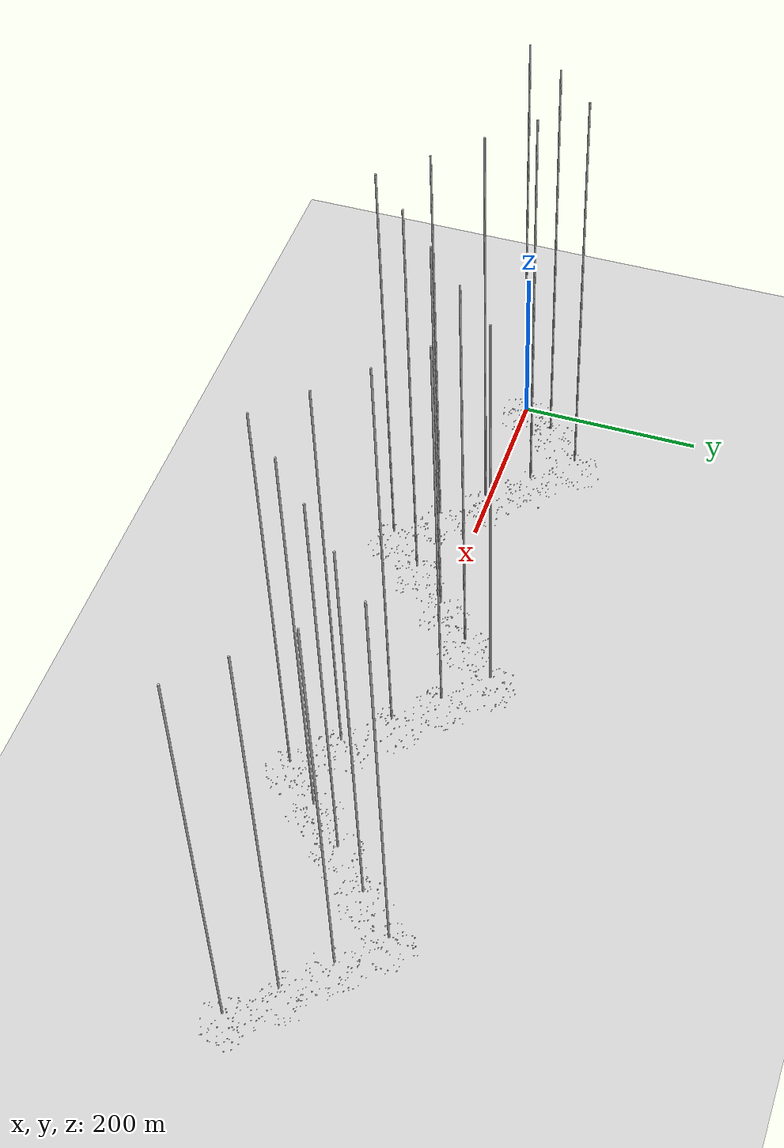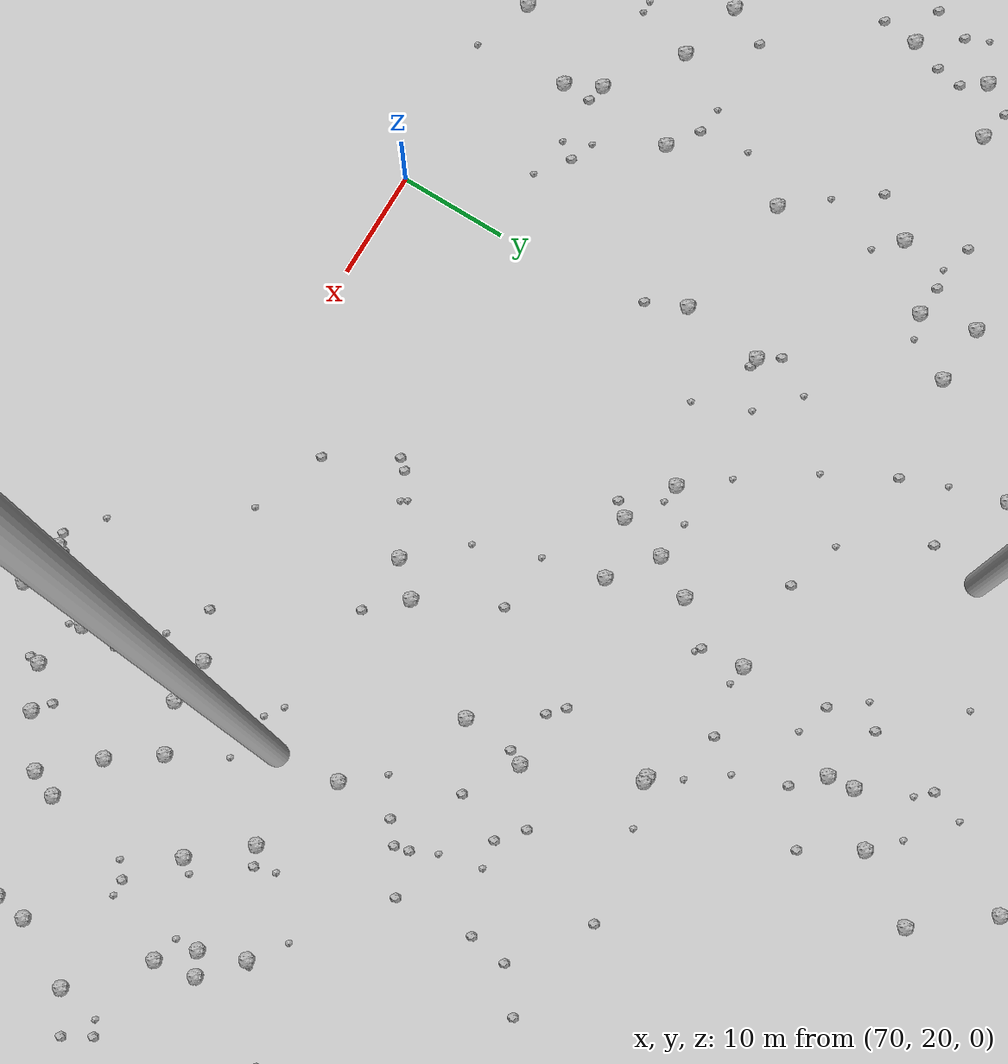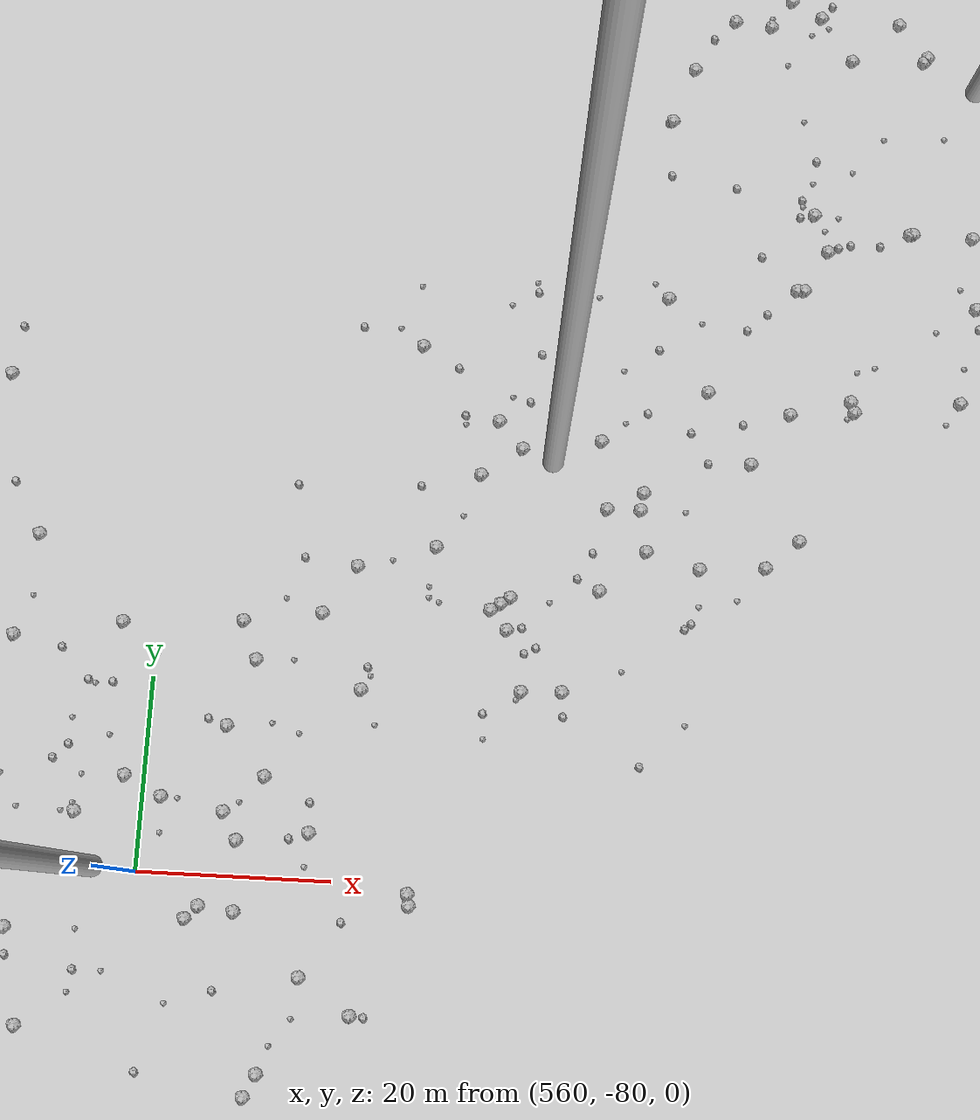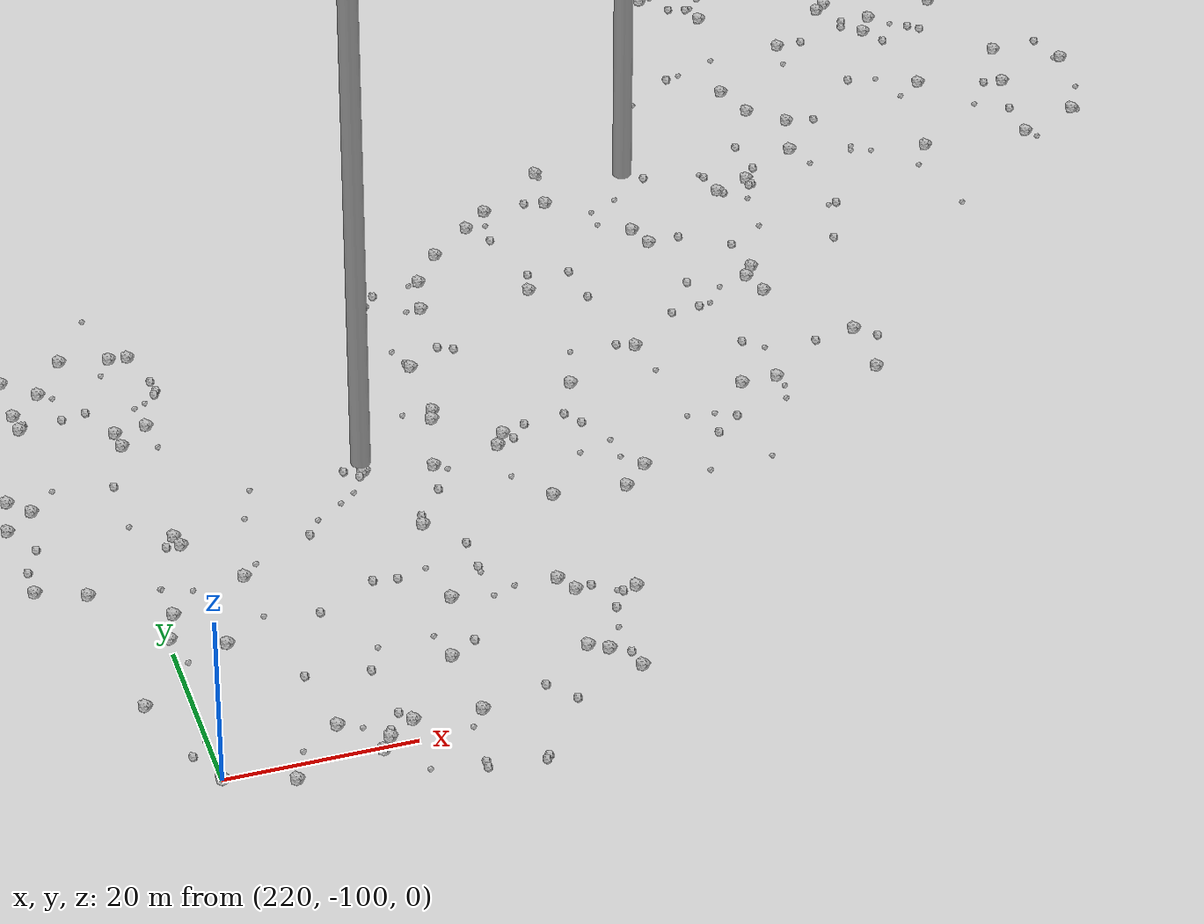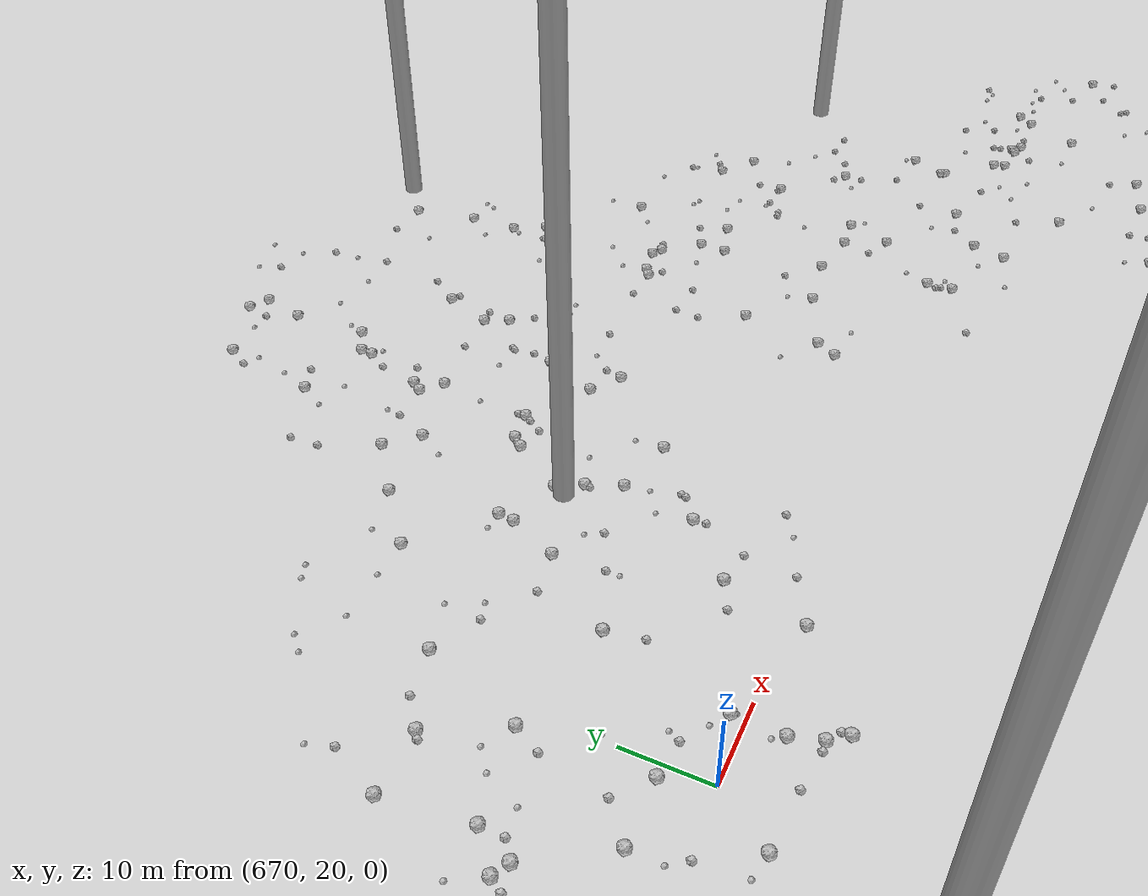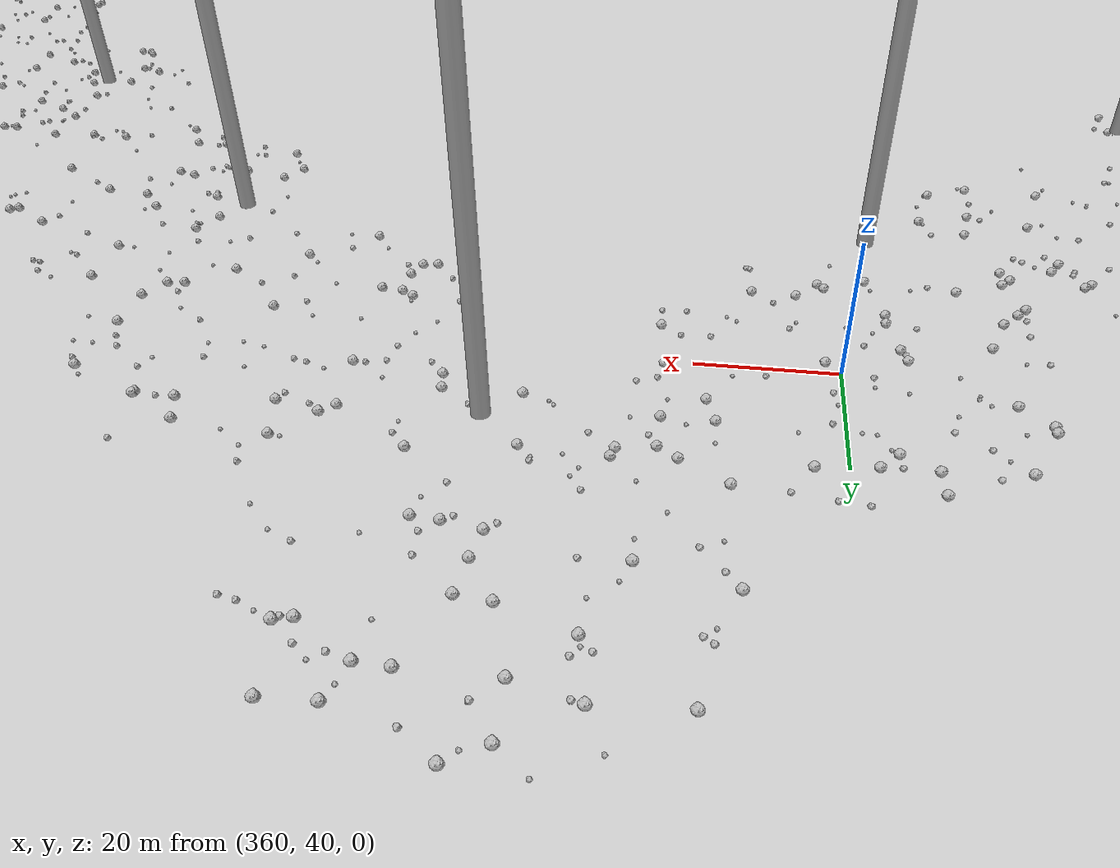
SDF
<sdf version="1.6">
 <world name="default">
  <include><uri>model://custom_ground</uri></include>
  <include><uri>model://sun</uri></include>
  <spherical_coordinates>
   <surface_model>EARTH_WGS84</surface_model>
   <latitude_deg>38.161479</latitude_deg>
   <longitude_deg>-122.454630</longitude_deg>
   <elevation>488.0</elevation>
   <heading_deg>90</heading_deg>
  </spherical_coordinates>
  <model name="rock1_0_0">
   <include><uri>model://rock1</uri><pose>9.647805996674009 18.82525347591028 0.5 0 0 0</pose></include>
  </model>
  <model name="rock1_0_1">
   <include><uri>model://rock1</uri><pose>30.14955270949092 19.38749987170479 0.5 0 0 0</pose></include>
  </model>
  <model name="rock1_0_2">
   <include><uri>model://rock1</uri><pose>6.286250552514286 -8.807822938171142 0.5 0 0 0</pose></include>
  </model>
  <model name="rock1_0_3">
   <include><uri>model://rock1</uri><pose>21.57044145342762 17.001756983942258 0.5 0 0 0</pose></include>
  </model>
  <model name="rock1_0_4">
   <include><uri>model://rock1</uri><pose>13.948814622853114 -23.19894125621399 0.5 0 0 0</pose></include>
  </model>
  <model name="rock1_0_5">
   <include><uri>model://rock1</uri><pose>19.608302852200815 6.788793556254987 0.5 0 0 0</pose></include>
  </model>
  <model name="rock1_0_6">
   <include><uri>model://rock1</uri><pose>3.9498882290787733 22.348185204923432 0.5 0 0 0</pose></include>
  </model>
  <model name="rock1_0_7">
   <include><uri>model://rock1</uri><pose>35.86363487273735 -4.967621130076903 0.5 0 0 0</pose></include>
  </model>
  <model name="rock1_0_8">
   <include><uri>model://rock1</uri><pose>5.276318932177222 -13.549015815785456 0.5 0 0 0</pose></include>
  </model>
  <model name="rock1_0_9">
   <include><uri>model://rock1</uri><pose>17.173128119663424 26.183405159375575 0.5 0 0 0</pose></include>
  </model>
  <model name="rock1_0_10">
   <include><uri>model://rock1</uri><pose>32.627688904720586 -4.239350699286696 0.5 0 0 0</pose></include>
  </model>
  <model name="rock1_0_11">
   <include><uri>model://rock1</uri><pose>39.425707797349204 -3.886486265646141 0.5 0 0 0</pose></include>
  </model>
  <model name="rock1_0_12">
   <include><uri>model://rock1</uri><pose>-12.698571005447004 -11.104939181028438 0.5 0 0 0</pose></include>
  </model>
  <model name="rock1_0_13">
   <include><uri>model://rock1</uri><pose>11.707732759311181 -17.736768907683608 0.5 0 0 0</pose></include>
  </model>
  <model name="rock1_0_14">
   <include><uri>model://rock1</uri><pose>-12.335774248969082 13.693248461509867 0.5 0 0 0</pose></include>
  </model>
  <model name="rock1_0_15">
   <include><uri>model://rock1</uri><pose>7.431120918871571 20.587823410565612 0.5 0 0 0</pose></include>
  </model>
  <model name="rock1_0_16">
   <include><uri>model://rock1</uri><pose>5.258989763411019 21.85668837933948 0.5 0 0 0</pose></include>
  </model>
  <model name="rock1_0_17">
   <include><uri>model://rock1</uri><pose>4.535249603685909 -5.532533549521116 0.5 0 0 0</pose></include>
  </model>
  <model name="rock1_0_18">
   <include><uri>model://rock1</uri><pose>-1.5548455478031862 4.765475880028809 0.5 0 0 0</pose></include>
  </model>
  <model name="rock1_0_19">
   <include><uri>model://rock1</uri><pose>12.737983086583128 -14.695589189227887 0.5 0 0 0</pose></include>
  </model>
  <model name="rock1_0_20">
   <include><uri>model://rock1</uri><pose>-10.584871531234992 -16.71809838869063 0.5 0 0 0</pose></include>
  </model>
  <model name="rock1_0_21">
   <include><uri>model://rock1</uri><pose>-3.9216911331897784 -10.142370566206349 0.5 0 0 0</pose></include>
  </model>
  <model name="rock1_0_22">
   <include><uri>model://rock1</uri><pose>7.494288331526278 -11.067427074349066 0.5 0 0 0</pose></include>
  </model>
  <model name="rock1_0_23">
   <include><uri>model://rock1</uri><pose>9.595066531621576 21.80125791827433 0.5 0 0 0</pose></include>
  </model>
  <model name="rock1_0_24">
   <include><uri>model://rock1</uri><pose>5.080699083628982 -14.872333043396015 0.5 0 0 0</pose></include>
  </model>
  <model name="rock1_0_25">
   <include><uri>model://rock1</uri><pose>24.415207560924543 -7.875359065724712 0.5 0 0 0</pose></include>
  </model>
  <model name="rock1_0_26">
   <include><uri>model://rock1</uri><pose>7.137574873047509 2.3744576738772523 0.5 0 0 0</pose></include>
  </model>
  <model name="rock2_0_0">
   <include><uri>model://rock2</uri><pose>17.29677814809635 -0.2718569112765614 0.3 0 0 0</pose></include>
  </model>
  <model name="rock2_0_1">
   <include><uri>model://rock2</uri><pose>10.142456065014926 14.240845012966908 0.3 0 0 0</pose></include>
  </model>
  <model name="rock2_0_2">
   <include><uri>model://rock2</uri><pose>-10.345253709911423 8.913257775941162 0.3 0 0 0</pose></include>
  </model>
  <model name="rock2_0_3">
   <include><uri>model://rock2</uri><pose>16.097111861417993 27.033245804952955 0.3 0 0 0</pose></include>
  </model>
  <model name="rock2_0_4">
   <include><uri>model://rock2</uri><pose>36.07638793135187 -5.499695298475622 0.3 0 0 0</pose></include>
  </model>
  <model name="rock2_0_5">
   <include><uri>model://rock2</uri><pose>13.962043625001307 27.205373706764007 0.3 0 0 0</pose></include>
  </model>
  <model name="rock2_0_6">
   <include><uri>model://rock2</uri><pose>-8.894393371948645 23.123084564227234 0.3 0 0 0</pose></include>
  </model>
  <model name="rock2_0_7">
   <include><uri>model://rock2</uri><pose>-16.767002455756707 -3.364641312894065 0.3 0 0 0</pose></include>
  </model>
  <model name="rock2_0_8">
   <include><uri>model://rock2</uri><pose>-8.957565446114575 -8.029547607908832 0.3 0 0 0</pose></include>
  </model>
  <model name="rock2_0_9">
   <include><uri>model://rock2</uri><pose>33.459806316162975 -14.677666894675358 0.3 0 0 0</pose></include>
  </model>
  <model name="rock2_0_10">
   <include><uri>model://rock2</uri><pose>36.24229256268524 4.055223317813571 0.3 0 0 0</pose></include>
  </model>
  <model name="rock2_0_11">
   <include><uri>model://rock2</uri><pose>5.539321627832759 7.393673998144948 0.3 0 0 0</pose></include>
  </model>
  <model name="rock2_0_12">
   <include><uri>model://rock2</uri><pose>27.070941744705287 8.362846305513962 0.3 0 0 0</pose></include>
  </model>
  <model name="rock2_0_13">
   <include><uri>model://rock2</uri><pose>13.975990661967579 21.046634532721207 0.3 0 0 0</pose></include>
  </model>
  <model name="rock2_0_14">
   <include><uri>model://rock2</uri><pose>24.655126035801985 13.359512873589395 0.3 0 0 0</pose></include>
  </model>
  <model name="rock2_0_15">
   <include><uri>model://rock2</uri><pose>-11.529335283331239 5.301720459436211 0.3 0 0 0</pose></include>
  </model>
  <model name="rock2_0_16">
   <include><uri>model://rock2</uri><pose>20.708997393180212 -24.095956158134978 0.3 0 0 0</pose></include>
  </model>
  <model name="rock2_0_17">
   <include><uri>model://rock2</uri><pose>13.177776516374216 -4.761186565020068 0.3 0 0 0</pose></include>
  </model>
  <model name="rock2_0_18">
   <include><uri>model://rock2</uri><pose>11.908103391193691 -5.362095350811462 0.3 0 0 0</pose></include>
  </model>
  <model name="rock2_0_19">
   <include><uri>model://rock2</uri><pose>15.754449637893707 -23.02892938082003 0.3 0 0 0</pose></include>
  </model>
  <model name="rock2_0_20">
   <include><uri>model://rock2</uri><pose>30.744974882864184 -19.527946019234122 0.3 0 0 0</pose></include>
  </model>
  <model name="rock2_0_21">
   <include><uri>model://rock2</uri><pose>5.894569892706578 -25.295856669808437 0.3 0 0 0</pose></include>
  </model>
  <model name="rock2_0_22">
   <include><uri>model://rock2</uri><pose>1.231316683336253 -15.99835879620487 0.3 0 0 0</pose></include>
  </model>
  <model name="rock2_0_23">
   <include><uri>model://rock2</uri><pose>-15.147324904276598 -8.504875318801929 0.3 0 0 0</pose></include>
  </model>
  <model name="rock2_0_24">
   <include><uri>model://rock2</uri><pose>4.567823696088247 4.407383654196543 0.3 0 0 0</pose></include>
  </model>
  <model name="rock2_0_25">
   <include><uri>model://rock2</uri><pose>9.517089704631676 18.119724375973725 0.3 0 0 0</pose></include>
  </model>
  <model name="rock2_0_26">
   <include><uri>model://rock2</uri><pose>-2.9129524897375916 3.360842174596293 0.3 0 0 0</pose></include>
  </model>
  <model name="rock3_0_0">
   <include><uri>model://rock3</uri><pose>-0.8078409601034302 -21.940229033310963 0.2 0 0 0</pose></include>
  </model>
  <model name="rock3_0_1">
   <include><uri>model://rock3</uri><pose>-9.230273460612821 20.86080399230223 0.2 0 0 0</pose></include>
  </model>
  <model name="rock3_0_2">
   <include><uri>model://rock3</uri><pose>17.84355409667029 -15.170037160717078 0.2 0 0 0</pose></include>
  </model>
  <model name="rock3_0_3">
   <include><uri>model://rock3</uri><pose>38.62751778206844 8.58236965822676 0.2 0 0 0</pose></include>
  </model>
  <model name="rock3_0_4">
   <include><uri>model://rock3</uri><pose>6.744086351869981 -8.087946780495585 0.2 0 0 0</pose></include>
  </model>
  <model name="rock3_0_5">
   <include><uri>model://rock3</uri><pose>36.53066115239426 11.478990714374937 0.2 0 0 0</pose></include>
  </model>
  <model name="rock3_0_6">
   <include><uri>model://rock3</uri><pose>6.492049355583639 19.996475859365844 0.2 0 0 0</pose></include>
  </model>
  <model name="rock3_0_7">
   <include><uri>model://rock3</uri><pose>8.746733974646812 -14.802816454833716 0.2 0 0 0</pose></include>
  </model>
  <model name="rock3_0_8">
   <include><uri>model://rock3</uri><pose>4.582821432572452 -15.999396808101007 0.2 0 0 0</pose></include>
  </model>
  <model name="rock3_0_9">
   <include><uri>model://rock3</uri><pose>22.469046108815576 -27.22773708478155 0.2 0 0 0</pose></include>
  </model>
  <model name="rock3_0_10">
   <include><uri>model://rock3</uri><pose>-8.033301978173085 -23.566718410463615 0.2 0 0 0</pose></include>
  </model>
  <model name="rock3_0_11">
   <include><uri>model://rock3</uri><pose>-7.62735357976667 -2.712214772419184 0.2 0 0 0</pose></include>
  </model>
  <model name="rock3_0_12">
   <include><uri>model://rock3</uri><pose>12.58958163959963 -1.7497675014134693 0.2 0 0 0</pose></include>
  </model>
  <model name="rock3_0_13">
   <include><uri>model://rock3</uri><pose>-3.603765749133629 -12.37447320939619 0.2 0 0 0</pose></include>
  </model>
  <model name="rock3_0_14">
   <include><uri>model://rock3</uri><pose>13.992032243575245 -10.520763945729751 0.2 0 0 0</pose></include>
  </model>
  <model name="rock3_0_15">
   <include><uri>model://rock3</uri><pose>21.48066129728153 -6.81461963676929 0.2 0 0 0</pose></include>
  </model>
  <model name="rock3_0_16">
   <include><uri>model://rock3</uri><pose>26.688646215042326 -2.5261434041541797 0.2 0 0 0</pose></include>
  </model>
  <model name="rock3_0_17">
   <include><uri>model://rock3</uri><pose>-14.081953154335418 5.936166675346499 0.2 0 0 0</pose></include>
  </model>
  <model name="rock3_0_18">
   <include><uri>model://rock3</uri><pose>23.163782933303324 0.7131495826989145 0.2 0 0 0</pose></include>
  </model>
  <model name="rock3_0_19">
   <include><uri>model://rock3</uri><pose>28.595379356055332 16.121353037416654 0.2 0 0 0</pose></include>
  </model>
  <model name="rock3_0_20">
   <include><uri>model://rock3</uri><pose>29.112291221836855 20.754597904482672 0.2 0 0 0</pose></include>
  </model>
  <model name="rock3_0_21">
   <include><uri>model://rock3</uri><pose>17.448508845432173 -17.99581659128345 0.2 0 0 0</pose></include>
  </model>
  <model name="rock3_0_22">
   <include><uri>model://rock3</uri><pose>7.2739492185611 -16.854068968080615 0.2 0 0 0</pose></include>
  </model>
  <model name="rock3_0_23">
   <include><uri>model://rock3</uri><pose>15.550702126112242 -17.32959749367791 0.2 0 0 0</pose></include>
  </model>
  <model name="rock3_0_24">
   <include><uri>model://rock3</uri><pose>31.608368343111664 -5.9989548341219 0.2 0 0 0</pose></include>
  </model>
  <model name="rock3_0_25">
   <include><uri>model://rock3</uri><pose>35.89115364789527 -6.4865756577270375 0.2 0 0 0</pose></include>
  </model>
  <model name="rock3_0_26">
   <include><uri>model://rock3</uri><pose>14.938013229594219 -9.245809727213114 0.2 0 0 0</pose></include>
  </model>
  <model name="rock1_1_0">
   <include><uri>model://rock1</uri><pose>15.560075300861246 53.865642667346556 0.5 0 0 0</pose></include>
  </model>
  <model name="rock1_1_1">
   <include><uri>model://rock1</uri><pose>55.0715968993044 27.513831199839654 0.5 0 0 0</pose></include>
  </model>
  <model name="rock1_1_2">
   <include><uri>model://rock1</uri><pose>14.178835363491887 33.558094034881364 0.5 0 0 0</pose></include>
  </model>
  <model name="rock1_1_3">
   <include><uri>model://rock1</uri><pose>27.650467737742737 22.148162658448946 0.5 0 0 0</pose></include>
  </model>
  <model name="rock1_1_4">
   <include><uri>model://rock1</uri><pose>50.39521981144941 20.885817941237136 0.5 0 0 0</pose></include>
  </model>
  <model name="rock1_1_5">
   <include><uri>model://rock1</uri><pose>35.23841069893886 60.135804016587194 0.5 0 0 0</pose></include>
  </model>
  <model name="rock1_1_6">
   <include><uri>model://rock1</uri><pose>35.23336220596828 52.58185891393535 0.5 0 0 0</pose></include>
  </model>
  <model name="rock1_1_7">
   <include><uri>model://rock1</uri><pose>43.618080613342144 17.951252939065277 0.5 0 0 0</pose></include>
  </model>
  <model name="rock1_1_8">
   <include><uri>model://rock1</uri><pose>15.021991277140344 34.753056744999455 0.5 0 0 0</pose></include>
  </model>
  <model name="rock1_1_9">
   <include><uri>model://rock1</uri><pose>43.60211938587006 27.47485338264682 0.5 0 0 0</pose></include>
  </model>
  <model name="rock1_1_10">
   <include><uri>model://rock1</uri><pose>22.11829267297435 20.034504760633844 0.5 0 0 0</pose></include>
  </model>
  <model name="rock1_1_11">
   <include><uri>model://rock1</uri><pose>46.943243456147236 35.42085879934906 0.5 0 0 0</pose></include>
  </model>
  <model name="rock1_1_12">
   <include><uri>model://rock1</uri><pose>40.93747264344337 37.018218107321026 0.5 0 0 0</pose></include>
  </model>
  <model name="rock1_1_13">
   <include><uri>model://rock1</uri><pose>24.97470831864959 52.70891949564941 0.5 0 0 0</pose></include>
  </model>
  <model name="rock1_1_14">
   <include><uri>model://rock1</uri><pose>23.30792570167163 23.012243780929815 0.5 0 0 0</pose></include>
  </model>
  <model name="rock1_1_15">
   <include><uri>model://rock1</uri><pose>53.495817404652996 30.626134663589593 0.5 0 0 0</pose></include>
  </model>
  <model name="rock1_1_16">
   <include><uri>model://rock1</uri><pose>31.348456599085893 20.842410425627307 0.5 0 0 0</pose></include>
  </model>
  <model name="rock1_1_17">
   <include><uri>model://rock1</uri><pose>18.59511673281109 59.935021346073704 0.5 0 0 0</pose></include>
  </model>
  <model name="rock1_1_18">
   <include><uri>model://rock1</uri><pose>54.9611927564644 49.701138417013055 0.5 0 0 0</pose></include>
  </model>
  <model name="rock1_1_19">
   <include><uri>model://rock1</uri><pose>21.778638433784216 32.433961894604394 0.5 0 0 0</pose></include>
  </model>
  <model name="rock1_1_20">
   <include><uri>model://rock1</uri><pose>22.259950558404142 31.503566037719807 0.5 0 0 0</pose></include>
  </model>
  <model name="rock1_1_21">
   <include><uri>model://rock1</uri><pose>51.81434234372543 60.996032849281576 0.5 0 0 0</pose></include>
  </model>
  <model name="rock1_1_22">
   <include><uri>model://rock1</uri><pose>27.81075929516362 24.66946013736827 0.5 0 0 0</pose></include>
  </model>
  <model name="rock1_1_23">
   <include><uri>model://rock1</uri><pose>67.0902581696161 47.60227927467745 0.5 0 0 0</pose></include>
  </model>
  <model name="rock1_1_24">
   <include><uri>model://rock1</uri><pose>55.25478064550491 38.311394628082866 0.5 0 0 0</pose></include>
  </model>
  <model name="rock1_1_25">
   <include><uri>model://rock1</uri><pose>33.35389900247966 25.93683046448395 0.5 0 0 0</pose></include>
  </model>
  <model name="rock1_1_26">
   <include><uri>model://rock1</uri><pose>39.79218629777236 62.23304964198338 0.5 0 0 0</pose></include>
  </model>
  <model name="rock2_1_0">
   <include><uri>model://rock2</uri><pose>31.473998633649654 52.97289679636376 0.3 0 0 0</pose></include>
  </model>
  <model name="rock2_1_1">
   <include><uri>model://rock2</uri><pose>16.47543530799556 24.989406658157616 0.3 0 0 0</pose></include>
  </model>
  <model name="rock2_1_2">
   <include><uri>model://rock2</uri><pose>31.574950674622585 37.96920307028002 0.3 0 0 0</pose></include>
  </model>
  <model name="rock2_1_3">
   <include><uri>model://rock2</uri><pose>36.24841903735292 55.633692324408756 0.3 0 0 0</pose></include>
  </model>
  <model name="rock2_1_4">
   <include><uri>model://rock2</uri><pose>11.370289175355797 45.489365344885876 0.3 0 0 0</pose></include>
  </model>
  <model name="rock2_1_5">
   <include><uri>model://rock2</uri><pose>34.847826252459896 49.280083882455266 0.3 0 0 0</pose></include>
  </model>
  <model name="rock2_1_6">
   <include><uri>model://rock2</uri><pose>55.15250468915118 30.25290765330166 0.3 0 0 0</pose></include>
  </model>
  <model name="rock2_1_7">
   <include><uri>model://rock2</uri><pose>37.16351732135165 20.173754806923895 0.3 0 0 0</pose></include>
  </model>
  <model name="rock2_1_8">
   <include><uri>model://rock2</uri><pose>68.64925350243598 44.092971363500716 0.3 0 0 0</pose></include>
  </model>
  <model name="rock2_1_9">
   <include><uri>model://rock2</uri><pose>49.496089532651276 66.27909452088821 0.3 0 0 0</pose></include>
  </model>
  <model name="rock2_1_10">
   <include><uri>model://rock2</uri><pose>32.509057505793905 56.29791786638357 0.3 0 0 0</pose></include>
  </model>
  <model name="rock2_1_11">
   <include><uri>model://rock2</uri><pose>17.341387887023245 36.327686081065856 0.3 0 0 0</pose></include>
  </model>
  <model name="rock2_1_12">
   <include><uri>model://rock2</uri><pose>60.719402177900825 31.76172194479403 0.3 0 0 0</pose></include>
  </model>
  <model name="rock2_1_13">
   <include><uri>model://rock2</uri><pose>34.897666783371484 27.355162250497965 0.3 0 0 0</pose></include>
  </model>
  <model name="rock2_1_14">
   <include><uri>model://rock2</uri><pose>52.46638384259289 40.31088049686262 0.3 0 0 0</pose></include>
  </model>
  <model name="rock2_1_15">
   <include><uri>model://rock2</uri><pose>24.15427112163543 39.770788771907206 0.3 0 0 0</pose></include>
  </model>
  <model name="rock2_1_16">
   <include><uri>model://rock2</uri><pose>14.619961948623635 43.237241242061536 0.3 0 0 0</pose></include>
  </model>
  <model name="rock2_1_17">
   <include><uri>model://rock2</uri><pose>27.37465124753139 67.20382779891841 0.3 0 0 0</pose></include>
  </model>
  <model name="rock2_1_18">
   <include><uri>model://rock2</uri><pose>12.498930981047579 30.906301965269513 0.3 0 0 0</pose></include>
  </model>
  <model name="rock2_1_19">
   <include><uri>model://rock2</uri><pose>42.630594059642135 40.70705974224959 0.3 0 0 0</pose></include>
  </model>
  <model name="rock2_1_20">
   <include><uri>model://rock2</uri><pose>36.604511557343756 58.085472500136234 0.3 0 0 0</pose></include>
  </model>
  <model name="rock2_1_21">
   <include><uri>model://rock2</uri><pose>43.54416363958998 18.547778174208524 0.3 0 0 0</pose></include>
  </model>
  <model name="rock2_1_22">
   <include><uri>model://rock2</uri><pose>14.72919973759784 25.91972603346023 0.3 0 0 0</pose></include>
  </model>
  <model name="rock2_1_23">
   <include><uri>model://rock2</uri><pose>25.638596779515055 25.045401862188122 0.3 0 0 0</pose></include>
  </model>
  <model name="rock2_1_24">
   <include><uri>model://rock2</uri><pose>48.943401822713696 57.39036391950279 0.3 0 0 0</pose></include>
  </model>
  <model name="rock2_1_25">
   <include><uri>model://rock2</uri><pose>36.87066462578606 62.95155529404877 0.3 0 0 0</pose></include>
  </model>
  <model name="rock2_1_26">
   <include><uri>model://rock2</uri><pose>22.65418563324605 19.42404737823864 0.3 0 0 0</pose></include>
  </model>
  <model name="rock3_1_0">
   <include><uri>model://rock3</uri><pose>53.95807815145298 58.86954138431324 0.2 0 0 0</pose></include>
  </model>
  <model name="rock3_1_1">
   <include><uri>model://rock3</uri><pose>55.88246279745958 18.89105349443465 0.2 0 0 0</pose></include>
  </model>
  <model name="rock3_1_2">
   <include><uri>model://rock3</uri><pose>24.710475692866176 59.14787634732571 0.2 0 0 0</pose></include>
  </model>
  <model name="rock3_1_3">
   <include><uri>model://rock3</uri><pose>34.12647439343439 14.269394855205462 0.2 0 0 0</pose></include>
  </model>
  <model name="rock3_1_4">
   <include><uri>model://rock3</uri><pose>52.263557443586386 65.3250834081511 0.2 0 0 0</pose></include>
  </model>
  <model name="rock3_1_5">
   <include><uri>model://rock3</uri><pose>45.43333076286187 30.118117854870658 0.2 0 0 0</pose></include>
  </model>
  <model name="rock3_1_6">
   <include><uri>model://rock3</uri><pose>12.504854461085957 32.44068776883315 0.2 0 0 0</pose></include>
  </model>
  <model name="rock3_1_7">
   <include><uri>model://rock3</uri><pose>11.581052650962423 35.68034897507372 0.2 0 0 0</pose></include>
  </model>
  <model name="rock3_1_8">
   <include><uri>model://rock3</uri><pose>46.703273568982965 17.907995376470762 0.2 0 0 0</pose></include>
  </model>
  <model name="rock3_1_9">
   <include><uri>model://rock3</uri><pose>25.6206665234962 58.93037819515652 0.2 0 0 0</pose></include>
  </model>
  <model name="rock3_1_10">
   <include><uri>model://rock3</uri><pose>20.02082831078876 41.27917601623368 0.2 0 0 0</pose></include>
  </model>
  <model name="rock3_1_11">
   <include><uri>model://rock3</uri><pose>15.85211499035061 38.52920036586194 0.2 0 0 0</pose></include>
  </model>
  <model name="rock3_1_12">
   <include><uri>model://rock3</uri><pose>44.29073866786079 30.108541143332122 0.2 0 0 0</pose></include>
  </model>
  <model name="rock3_1_13">
   <include><uri>model://rock3</uri><pose>48.113558988944284 18.260604968051904 0.2 0 0 0</pose></include>
  </model>
  <model name="rock3_1_14">
   <include><uri>model://rock3</uri><pose>24.049762841724828 51.611731512772344 0.2 0 0 0</pose></include>
  </model>
  <model name="rock3_1_15">
   <include><uri>model://rock3</uri><pose>51.80281826043624 53.476862265579236 0.2 0 0 0</pose></include>
  </model>
  <model name="rock3_1_16">
   <include><uri>model://rock3</uri><pose>44.822025278854944 22.86254886349463 0.2 0 0 0</pose></include>
  </model>
  <model name="rock3_1_17">
   <include><uri>model://rock3</uri><pose>49.9140931694826 40.579840791035444 0.2 0 0 0</pose></include>
  </model>
  <model name="rock3_1_18">
   <include><uri>model://rock3</uri><pose>59.674246219730655 30.163887894566535 0.2 0 0 0</pose></include>
  </model>
  <model name="rock3_1_19">
   <include><uri>model://rock3</uri><pose>28.51589865598314 40.39074434674809 0.2 0 0 0</pose></include>
  </model>
  <model name="rock3_1_20">
   <include><uri>model://rock3</uri><pose>58.53791022981849 32.57829600116047 0.2 0 0 0</pose></include>
  </model>
  <model name="rock3_1_21">
   <include><uri>model://rock3</uri><pose>63.6157757881722 29.50936503214881 0.2 0 0 0</pose></include>
  </model>
  <model name="rock3_1_22">
   <include><uri>model://rock3</uri><pose>31.579548130201637 58.330427143896536 0.2 0 0 0</pose></include>
  </model>
  <model name="rock3_1_23">
   <include><uri>model://rock3</uri><pose>51.90169256615343 44.90026090354233 0.2 0 0 0</pose></include>
  </model>
  <model name="rock3_1_24">
   <include><uri>model://rock3</uri><pose>17.679271697627286 37.66161675151868 0.2 0 0 0</pose></include>
  </model>
  <model name="rock3_1_25">
   <include><uri>model://rock3</uri><pose>46.75850447499812 19.33690680347066 0.2 0 0 0</pose></include>
  </model>
  <model name="rock3_1_26">
   <include><uri>model://rock3</uri><pose>49.92139148056301 18.04748644317209 0.2 0 0 0</pose></include>
  </model>
  <model name="rock1_2_0">
   <include><uri>model://rock1</uri><pose>65.99828596104176 93.81141904971281 0.5 0 0 0</pose></include>
  </model>
  <model name="rock1_2_1">
   <include><uri>model://rock1</uri><pose>86.33555584836066 52.54726698993734 0.5 0 0 0</pose></include>
  </model>
  <model name="rock1_2_2">
   <include><uri>model://rock1</uri><pose>55.617895582474965 70.5278454940909 0.5 0 0 0</pose></include>
  </model>
  <model name="rock1_2_3">
   <include><uri>model://rock1</uri><pose>81.52850516567099 54.973706861076266 0.5 0 0 0</pose></include>
  </model>
  <model name="rock1_2_4">
   <include><uri>model://rock1</uri><pose>67.69101951896646 80.56783071989639 0.5 0 0 0</pose></include>
  </model>
  <model name="rock1_2_5">
   <include><uri>model://rock1</uri><pose>55.345631503500016 92.81393225456833 0.5 0 0 0</pose></include>
  </model>
  <model name="rock1_2_6">
   <include><uri>model://rock1</uri><pose>89.68175151152514 60.66940568520181 0.5 0 0 0</pose></include>
  </model>
  <model name="rock1_2_7">
   <include><uri>model://rock1</uri><pose>104.37217047287982 91.2338418239159 0.5 0 0 0</pose></include>
  </model>
  <model name="rock1_2_8">
   <include><uri>model://rock1</uri><pose>87.6297458133802 57.01224203523406 0.5 0 0 0</pose></include>
  </model>
  <model name="rock1_2_9">
   <include><uri>model://rock1</uri><pose>60.23464243370434 81.4924438878229 0.5 0 0 0</pose></include>
  </model>
  <model name="rock1_2_10">
   <include><uri>model://rock1</uri><pose>82.99260437023662 108.78590701952837 0.5 0 0 0</pose></include>
  </model>
  <model name="rock1_2_11">
   <include><uri>model://rock1</uri><pose>67.98384596207615 55.18161812469815 0.5 0 0 0</pose></include>
  </model>
  <model name="rock1_2_12">
   <include><uri>model://rock1</uri><pose>92.25604719153458 68.10310297529183 0.5 0 0 0</pose></include>
  </model>
  <model name="rock1_2_13">
   <include><uri>model://rock1</uri><pose>60.73591569434811 99.84070777862435 0.5 0 0 0</pose></include>
  </model>
  <model name="rock1_2_14">
   <include><uri>model://rock1</uri><pose>96.39271447814055 81.56844958642803 0.5 0 0 0</pose></include>
  </model>
  <model name="rock1_2_15">
   <include><uri>model://rock1</uri><pose>104.77143942557758 65.87716849493637 0.5 0 0 0</pose></include>
  </model>
  <model name="rock1_2_16">
   <include><uri>model://rock1</uri><pose>96.63897247774355 79.1185870471268 0.5 0 0 0</pose></include>
  </model>
  <model name="rock1_2_17">
   <include><uri>model://rock1</uri><pose>56.93305563998175 65.49940825406037 0.5 0 0 0</pose></include>
  </model>
  <model name="rock1_2_18">
   <include><uri>model://rock1</uri><pose>63.006309092208824 85.68629134219314 0.5 0 0 0</pose></include>
  </model>
  <model name="rock1_2_19">
   <include><uri>model://rock1</uri><pose>63.31757821974068 100.4094700842894 0.5 0 0 0</pose></include>
  </model>
  <model name="rock1_2_20">
   <include><uri>model://rock1</uri><pose>105.28095029052 65.82971364207654 0.5 0 0 0</pose></include>
  </model>
  <model name="rock1_2_21">
   <include><uri>model://rock1</uri><pose>91.7908954992444 53.862337642866024 0.5 0 0 0</pose></include>
  </model>
  <model name="rock1_2_22">
   <include><uri>model://rock1</uri><pose>80.75750301605683 89.6843003654933 0.5 0 0 0</pose></include>
  </model>
  <model name="rock1_2_23">
   <include><uri>model://rock1</uri><pose>61.0863301808098 70.22277178455826 0.5 0 0 0</pose></include>
  </model>
  <model name="rock1_2_24">
   <include><uri>model://rock1</uri><pose>99.32689741538525 97.66500749733692 0.5 0 0 0</pose></include>
  </model>
  <model name="rock1_2_25">
   <include><uri>model://rock1</uri><pose>53.43466740267025 73.43491991167213 0.5 0 0 0</pose></include>
  </model>
  <model name="rock1_2_26">
   <include><uri>model://rock1</uri><pose>100.47722948431382 85.0353072640761 0.5 0 0 0</pose></include>
  </model>
  <model name="rock2_2_0">
   <include><uri>model://rock2</uri><pose>98.74780287397964 69.05653515617757 0.3 0 0 0</pose></include>
  </model>
  <model name="rock2_2_1">
   <include><uri>model://rock2</uri><pose>61.113958410101134 89.2265131304732 0.3 0 0 0</pose></include>
  </model>
  <model name="rock2_2_2">
   <include><uri>model://rock2</uri><pose>103.49736199945356 80.06692604003342 0.3 0 0 0</pose></include>
  </model>
  <model name="rock2_2_3">
   <include><uri>model://rock2</uri><pose>99.73867914909334 101.86227113136164 0.3 0 0 0</pose></include>
  </model>
  <model name="rock2_2_4">
   <include><uri>model://rock2</uri><pose>68.80765179524644 55.108592570618164 0.3 0 0 0</pose></include>
  </model>
  <model name="rock2_2_5">
   <include><uri>model://rock2</uri><pose>70.71325363354975 71.36742036520158 0.3 0 0 0</pose></include>
  </model>
  <model name="rock2_2_6">
   <include><uri>model://rock2</uri><pose>91.1226779690908 80.73484187746197 0.3 0 0 0</pose></include>
  </model>
  <model name="rock2_2_7">
   <include><uri>model://rock2</uri><pose>92.71733310405352 64.2097413816607 0.3 0 0 0</pose></include>
  </model>
  <model name="rock2_2_8">
   <include><uri>model://rock2</uri><pose>66.713866600599 57.116157606122655 0.3 0 0 0</pose></include>
  </model>
  <model name="rock2_2_9">
   <include><uri>model://rock2</uri><pose>72.22317996858445 91.51181026781114 0.3 0 0 0</pose></include>
  </model>
  <model name="rock2_2_10">
   <include><uri>model://rock2</uri><pose>95.95449741958102 105.11695139579767 0.3 0 0 0</pose></include>
  </model>
  <model name="rock2_2_11">
   <include><uri>model://rock2</uri><pose>91.50426694301618 76.09452265644973 0.3 0 0 0</pose></include>
  </model>
  <model name="rock2_2_12">
   <include><uri>model://rock2</uri><pose>99.087894060887 76.67929193069403 0.3 0 0 0</pose></include>
  </model>
  <model name="rock2_2_13">
   <include><uri>model://rock2</uri><pose>76.15957173540066 88.23118392383896 0.3 0 0 0</pose></include>
  </model>
  <model name="rock2_2_14">
   <include><uri>model://rock2</uri><pose>53.25848020112995 76.93794419674725 0.3 0 0 0</pose></include>
  </model>
  <model name="rock2_2_15">
   <include><uri>model://rock2</uri><pose>56.01739593212446 97.19720992348623 0.3 0 0 0</pose></include>
  </model>
  <model name="rock2_2_16">
   <include><uri>model://rock2</uri><pose>85.25527984432253 51.333980843331496 0.3 0 0 0</pose></include>
  </model>
  <model name="rock2_2_17">
   <include><uri>model://rock2</uri><pose>86.40901074448723 52.74590049956596 0.3 0 0 0</pose></include>
  </model>
  <model name="rock2_2_18">
   <include><uri>model://rock2</uri><pose>86.72106513320885 102.77941671336583 0.3 0 0 0</pose></include>
  </model>
  <model name="rock2_2_19">
   <include><uri>model://rock2</uri><pose>83.88460652886535 68.06847402645792 0.3 0 0 0</pose></include>
  </model>
  <model name="rock2_2_20">
   <include><uri>model://rock2</uri><pose>97.0768160029522 101.71836929315324 0.3 0 0 0</pose></include>
  </model>
  <model name="rock2_2_21">
   <include><uri>model://rock2</uri><pose>54.06006404945862 65.70896835494003 0.3 0 0 0</pose></include>
  </model>
  <model name="rock2_2_22">
   <include><uri>model://rock2</uri><pose>65.07061113400391 102.19686711866922 0.3 0 0 0</pose></include>
  </model>
  <model name="rock2_2_23">
   <include><uri>model://rock2</uri><pose>84.74998807950581 92.91804962902667 0.3 0 0 0</pose></include>
  </model>
  <model name="rock2_2_24">
   <include><uri>model://rock2</uri><pose>74.31738942274364 76.98354042927286 0.3 0 0 0</pose></include>
  </model>
  <model name="rock2_2_25">
   <include><uri>model://rock2</uri><pose>93.03348929401162 87.70414847009698 0.3 0 0 0</pose></include>
  </model>
  <model name="rock2_2_26">
   <include><uri>model://rock2</uri><pose>59.319823526150586 89.28314988610674 0.3 0 0 0</pose></include>
  </model>
  <model name="rock3_2_0">
   <include><uri>model://rock3</uri><pose>78.87479975262612 69.68201450687906 0.2 0 0 0</pose></include>
  </model>
  <model name="rock3_2_1">
   <include><uri>model://rock3</uri><pose>83.2287533314506 54.79737066218755 0.2 0 0 0</pose></include>
  </model>
  <model name="rock3_2_2">
   <include><uri>model://rock3</uri><pose>64.53018089310345 100.48646467429589 0.2 0 0 0</pose></include>
  </model>
  <model name="rock3_2_3">
   <include><uri>model://rock3</uri><pose>82.02163813967184 94.25221952124423 0.2 0 0 0</pose></include>
  </model>
  <model name="rock3_2_4">
   <include><uri>model://rock3</uri><pose>103.29530103886061 68.65856494203572 0.2 0 0 0</pose></include>
  </model>
  <model name="rock3_2_5">
   <include><uri>model://rock3</uri><pose>76.89144461843605 98.61526063232168 0.2 0 0 0</pose></include>
  </model>
  <model name="rock3_2_6">
   <include><uri>model://rock3</uri><pose>93.20019012335007 63.810854596659425 0.2 0 0 0</pose></include>
  </model>
  <model name="rock3_2_7">
   <include><uri>model://rock3</uri><pose>59.13805216682014 66.23721971781222 0.2 0 0 0</pose></include>
  </model>
  <model name="rock3_2_8">
   <include><uri>model://rock3</uri><pose>69.0921926595787 75.44785320072293 0.2 0 0 0</pose></include>
  </model>
  <model name="rock3_2_9">
   <include><uri>model://rock3</uri><pose>73.99384534289062 65.21327587568773 0.2 0 0 0</pose></include>
  </model>
  <model name="rock3_2_10">
   <include><uri>model://rock3</uri><pose>94.26940682453318 86.34631369359208 0.2 0 0 0</pose></include>
  </model>
  <model name="rock3_2_11">
   <include><uri>model://rock3</uri><pose>100.81426050322636 71.97084592938516 0.2 0 0 0</pose></include>
  </model>
  <model name="rock3_2_12">
   <include><uri>model://rock3</uri><pose>94.05163562325916 67.88130155091287 0.2 0 0 0</pose></include>
  </model>
  <model name="rock3_2_13">
   <include><uri>model://rock3</uri><pose>72.20189973982832 57.25807445436468 0.2 0 0 0</pose></include>
  </model>
  <model name="rock3_2_14">
   <include><uri>model://rock3</uri><pose>78.36440417241195 58.90049455220924 0.2 0 0 0</pose></include>
  </model>
  <model name="rock3_2_15">
   <include><uri>model://rock3</uri><pose>94.09462794016308 90.79562834370978 0.2 0 0 0</pose></include>
  </model>
  <model name="rock3_2_16">
   <include><uri>model://rock3</uri><pose>84.05077925168716 57.33563122995219 0.2 0 0 0</pose></include>
  </model>
  <model name="rock3_2_17">
   <include><uri>model://rock3</uri><pose>81.94352791596216 96.44663078148517 0.2 0 0 0</pose></include>
  </model>
  <model name="rock3_2_18">
   <include><uri>model://rock3</uri><pose>91.45888958470005 104.00414977634877 0.2 0 0 0</pose></include>
  </model>
  <model name="rock3_2_19">
   <include><uri>model://rock3</uri><pose>85.31172547197636 86.84342382874499 0.2 0 0 0</pose></include>
  </model>
  <model name="rock3_2_20">
   <include><uri>model://rock3</uri><pose>75.84199291582198 109.66645976420266 0.2 0 0 0</pose></include>
  </model>
  <model name="rock3_2_21">
   <include><uri>model://rock3</uri><pose>94.55257506476218 75.08135466758357 0.2 0 0 0</pose></include>
  </model>
  <model name="rock3_2_22">
   <include><uri>model://rock3</uri><pose>97.99492110317703 87.44676114848735 0.2 0 0 0</pose></include>
  </model>
  <model name="rock3_2_23">
   <include><uri>model://rock3</uri><pose>74.28498909025114 52.21392534824058 0.2 0 0 0</pose></include>
  </model>
  <model name="rock3_2_24">
   <include><uri>model://rock3</uri><pose>68.66543032828798 60.48444773610617 0.2 0 0 0</pose></include>
  </model>
  <model name="rock3_2_25">
   <include><uri>model://rock3</uri><pose>75.15527160009702 98.77925692300252 0.2 0 0 0</pose></include>
  </model>
  <model name="rock3_2_26">
   <include><uri>model://rock3</uri><pose>89.15367318136997 79.00530588537934 0.2 0 0 0</pose></include>
  </model>
  <model name="rock1_3_0">
   <include><uri>model://rock1</uri><pose>120.38897596530887 27.585135666306797 0.5 0 0 0</pose></include>
  </model>
  <model name="rock1_3_1">
   <include><uri>model://rock1</uri><pose>127.77250283173913 25.06287036995541 0.5 0 0 0</pose></include>
  </model>
  <model name="rock1_3_2">
   <include><uri>model://rock1</uri><pose>144.13197050356985 56.403263064088925 0.5 0 0 0</pose></include>
  </model>
  <model name="rock1_3_3">
   <include><uri>model://rock1</uri><pose>146.06652607523722 32.49748489104253 0.5 0 0 0</pose></include>
  </model>
  <model name="rock1_3_4">
   <include><uri>model://rock1</uri><pose>139.33117107053627 41.75748967267089 0.5 0 0 0</pose></include>
  </model>
  <model name="rock1_3_5">
   <include><uri>model://rock1</uri><pose>114.16083708666396 11.580784280123257 0.5 0 0 0</pose></include>
  </model>
  <model name="rock1_3_6">
   <include><uri>model://rock1</uri><pose>118.95266633093934 43.36565989968148 0.5 0 0 0</pose></include>
  </model>
  <model name="rock1_3_7">
   <include><uri>model://rock1</uri><pose>102.21014789387905 40.3641327171831 0.5 0 0 0</pose></include>
  </model>
  <model name="rock1_3_8">
   <include><uri>model://rock1</uri><pose>114.62743476694054 12.183618488591394 0.5 0 0 0</pose></include>
  </model>
  <model name="rock1_3_9">
   <include><uri>model://rock1</uri><pose>119.0180924801398 17.215123415459683 0.5 0 0 0</pose></include>
  </model>
  <model name="rock1_3_10">
   <include><uri>model://rock1</uri><pose>137.3796477053205 40.72194204275303 0.5 0 0 0</pose></include>
  </model>
  <model name="rock1_3_11">
   <include><uri>model://rock1</uri><pose>108.58544189886621 49.88845753014655 0.5 0 0 0</pose></include>
  </model>
  <model name="rock1_3_12">
   <include><uri>model://rock1</uri><pose>109.5694130524521 55.96017756146187 0.5 0 0 0</pose></include>
  </model>
  <model name="rock1_3_13">
   <include><uri>model://rock1</uri><pose>131.7385609733113 20.579822549908734 0.5 0 0 0</pose></include>
  </model>
  <model name="rock1_3_14">
   <include><uri>model://rock1</uri><pose>142.80530448529888 26.56563510904953 0.5 0 0 0</pose></include>
  </model>
  <model name="rock1_3_15">
   <include><uri>model://rock1</uri><pose>124.739138501535 29.355600971995596 0.5 0 0 0</pose></include>
  </model>
  <model name="rock1_3_16">
   <include><uri>model://rock1</uri><pose>118.43872019536428 10.753604260341174 0.5 0 0 0</pose></include>
  </model>
  <model name="rock1_3_17">
   <include><uri>model://rock1</uri><pose>132.75172731123206 23.02075942582318 0.5 0 0 0</pose></include>
  </model>
  <model name="rock1_3_18">
   <include><uri>model://rock1</uri><pose>127.22734604656155 40.23337113110983 0.5 0 0 0</pose></include>
  </model>
  <model name="rock1_3_19">
   <include><uri>model://rock1</uri><pose>116.16168764210825 27.84006863171586 0.5 0 0 0</pose></include>
  </model>
  <model name="rock1_3_20">
   <include><uri>model://rock1</uri><pose>135.87540809691993 44.731570485485335 0.5 0 0 0</pose></include>
  </model>
  <model name="rock1_3_21">
   <include><uri>model://rock1</uri><pose>127.54201821788428 17.46919491639385 0.5 0 0 0</pose></include>
  </model>
  <model name="rock1_3_22">
   <include><uri>model://rock1</uri><pose>123.72612128113994 15.74778302568017 0.5 0 0 0</pose></include>
  </model>
  <model name="rock1_3_23">
   <include><uri>model://rock1</uri><pose>131.34404899318753 35.473834638451024 0.5 0 0 0</pose></include>
  </model>
  <model name="rock1_3_24">
   <include><uri>model://rock1</uri><pose>99.63560938843807 37.5870563529088 0.5 0 0 0</pose></include>
  </model>
  <model name="rock1_3_25">
   <include><uri>model://rock1</uri><pose>139.9783382596375 38.01385056106578 0.5 0 0 0</pose></include>
  </model>
  <model name="rock1_3_26">
   <include><uri>model://rock1</uri><pose>118.7854419046044 20.650912271637694 0.5 0 0 0</pose></include>
  </model>
  <model name="rock2_3_0">
   <include><uri>model://rock2</uri><pose>108.90053395853366 54.6651073878805 0.3 0 0 0</pose></include>
  </model>
  <model name="rock2_3_1">
   <include><uri>model://rock2</uri><pose>149.46920339381165 34.67258792656756 0.3 0 0 0</pose></include>
  </model>
  <model name="rock2_3_2">
   <include><uri>model://rock2</uri><pose>114.02387553384357 59.39539489437137 0.3 0 0 0</pose></include>
  </model>
  <model name="rock2_3_3">
   <include><uri>model://rock2</uri><pose>123.5994717365529 14.80613889505668 0.3 0 0 0</pose></include>
  </model>
  <model name="rock2_3_4">
   <include><uri>model://rock2</uri><pose>124.2052613144605 60.07013558356593 0.3 0 0 0</pose></include>
  </model>
  <model name="rock2_3_5">
   <include><uri>model://rock2</uri><pose>95.47728304748924 27.02937527965594 0.3 0 0 0</pose></include>
  </model>
  <model name="rock2_3_6">
   <include><uri>model://rock2</uri><pose>92.73657196507081 33.91887807190465 0.3 0 0 0</pose></include>
  </model>
  <model name="rock2_3_7">
   <include><uri>model://rock2</uri><pose>103.26454603929868 56.91836325458461 0.3 0 0 0</pose></include>
  </model>
  <model name="rock2_3_8">
   <include><uri>model://rock2</uri><pose>117.88464911247218 68.44616279991286 0.3 0 0 0</pose></include>
  </model>
  <model name="rock2_3_9">
   <include><uri>model://rock2</uri><pose>135.67581356450341 32.00866927195711 0.3 0 0 0</pose></include>
  </model>
  <model name="rock2_3_10">
   <include><uri>model://rock2</uri><pose>120.80595032749534 51.69646416698471 0.3 0 0 0</pose></include>
  </model>
  <model name="rock2_3_11">
   <include><uri>model://rock2</uri><pose>91.92504743420201 33.012324607088544 0.3 0 0 0</pose></include>
  </model>
  <model name="rock2_3_12">
   <include><uri>model://rock2</uri><pose>124.81128336985877 52.80657007657253 0.3 0 0 0</pose></include>
  </model>
  <model name="rock2_3_13">
   <include><uri>model://rock2</uri><pose>112.02893610357717 25.88370697206975 0.3 0 0 0</pose></include>
  </model>
  <model name="rock2_3_14">
   <include><uri>model://rock2</uri><pose>124.70727257230936 63.6259674715871 0.3 0 0 0</pose></include>
  </model>
  <model name="rock2_3_15">
   <include><uri>model://rock2</uri><pose>98.53504807214607 47.73049792140734 0.3 0 0 0</pose></include>
  </model>
  <model name="rock2_3_16">
   <include><uri>model://rock2</uri><pose>116.25362152632056 57.48082226977627 0.3 0 0 0</pose></include>
  </model>
  <model name="rock2_3_17">
   <include><uri>model://rock2</uri><pose>105.19225315320598 37.21633357177392 0.3 0 0 0</pose></include>
  </model>
  <model name="rock2_3_18">
   <include><uri>model://rock2</uri><pose>128.1936431348982 66.62569244101323 0.3 0 0 0</pose></include>
  </model>
  <model name="rock2_3_19">
   <include><uri>model://rock2</uri><pose>114.29028050675754 53.046270982033434 0.3 0 0 0</pose></include>
  </model>
  <model name="rock2_3_20">
   <include><uri>model://rock2</uri><pose>148.06378316720802 37.05800686498901 0.3 0 0 0</pose></include>
  </model>
  <model name="rock2_3_21">
   <include><uri>model://rock2</uri><pose>126.05915398329171 18.67948026849809 0.3 0 0 0</pose></include>
  </model>
  <model name="rock2_3_22">
   <include><uri>model://rock2</uri><pose>104.62271367065307 55.641241898127475 0.3 0 0 0</pose></include>
  </model>
  <model name="rock2_3_23">
   <include><uri>model://rock2</uri><pose>112.98401625092445 11.29321088858482 0.3 0 0 0</pose></include>
  </model>
  <model name="rock2_3_24">
   <include><uri>model://rock2</uri><pose>121.12197934828146 50.37635997991805 0.3 0 0 0</pose></include>
  </model>
  <model name="rock2_3_25">
   <include><uri>model://rock2</uri><pose>119.31799438636106 48.880797688291096 0.3 0 0 0</pose></include>
  </model>
  <model name="rock2_3_26">
   <include><uri>model://rock2</uri><pose>128.86905116516039 41.01816910137359 0.3 0 0 0</pose></include>
  </model>
  <model name="rock3_3_0">
   <include><uri>model://rock3</uri><pose>109.17690751672323 67.11701162031876 0.2 0 0 0</pose></include>
  </model>
  <model name="rock3_3_1">
   <include><uri>model://rock3</uri><pose>115.89749938010424 35.954132019363925 0.2 0 0 0</pose></include>
  </model>
  <model name="rock3_3_2">
   <include><uri>model://rock3</uri><pose>137.1650340340472 32.02407307146093 0.2 0 0 0</pose></include>
  </model>
  <model name="rock3_3_3">
   <include><uri>model://rock3</uri><pose>128.3135427718758 42.89106222747745 0.2 0 0 0</pose></include>
  </model>
  <model name="rock3_3_4">
   <include><uri>model://rock3</uri><pose>119.44228778823646 16.035500458385393 0.2 0 0 0</pose></include>
  </model>
  <model name="rock3_3_5">
   <include><uri>model://rock3</uri><pose>142.98387809991968 50.09474991512223 0.2 0 0 0</pose></include>
  </model>
  <model name="rock3_3_6">
   <include><uri>model://rock3</uri><pose>115.74657120102303 23.735166607414598 0.2 0 0 0</pose></include>
  </model>
  <model name="rock3_3_7">
   <include><uri>model://rock3</uri><pose>129.09314343748545 13.791907146123181 0.2 0 0 0</pose></include>
  </model>
  <model name="rock3_3_8">
   <include><uri>model://rock3</uri><pose>93.08271323668212 48.177716630541866 0.2 0 0 0</pose></include>
  </model>
  <model name="rock3_3_9">
   <include><uri>model://rock3</uri><pose>119.72241892896331 53.96539120132787 0.2 0 0 0</pose></include>
  </model>
  <model name="rock3_3_10">
   <include><uri>model://rock3</uri><pose>133.3797129991438 15.85947902796403 0.2 0 0 0</pose></include>
  </model>
  <model name="rock3_3_11">
   <include><uri>model://rock3</uri><pose>95.19584848950733 34.989282496345616 0.2 0 0 0</pose></include>
  </model>
  <model name="rock3_3_12">
   <include><uri>model://rock3</uri><pose>117.45773333260709 34.844207523083185 0.2 0 0 0</pose></include>
  </model>
  <model name="rock3_3_13">
   <include><uri>model://rock3</uri><pose>94.87178128033004 35.49857365564442 0.2 0 0 0</pose></include>
  </model>
  <model name="rock3_3_14">
   <include><uri>model://rock3</uri><pose>132.2841623728631 36.59068792983781 0.2 0 0 0</pose></include>
  </model>
  <model name="rock3_3_15">
   <include><uri>model://rock3</uri><pose>95.24813373563013 42.350118828303316 0.2 0 0 0</pose></include>
  </model>
  <model name="rock3_3_16">
   <include><uri>model://rock3</uri><pose>146.7649871055259 36.36875641441288 0.2 0 0 0</pose></include>
  </model>
  <model name="rock3_3_17">
   <include><uri>model://rock3</uri><pose>102.31186746579277 24.395308747073987 0.2 0 0 0</pose></include>
  </model>
  <model name="rock3_3_18">
   <include><uri>model://rock3</uri><pose>122.02581955806446 34.25657692583742 0.2 0 0 0</pose></include>
  </model>
  <model name="rock3_3_19">
   <include><uri>model://rock3</uri><pose>132.79710754349009 47.00102064449637 0.2 0 0 0</pose></include>
  </model>
  <model name="rock3_3_20">
   <include><uri>model://rock3</uri><pose>134.30732736356086 30.858911740575806 0.2 0 0 0</pose></include>
  </model>
  <model name="rock3_3_21">
   <include><uri>model://rock3</uri><pose>118.80724369744846 57.82065201634401 0.2 0 0 0</pose></include>
  </model>
  <model name="rock3_3_22">
   <include><uri>model://rock3</uri><pose>109.866700412986 13.786012524719112 0.2 0 0 0</pose></include>
  </model>
  <model name="rock3_3_23">
   <include><uri>model://rock3</uri><pose>133.46979906124056 16.895596541513612 0.2 0 0 0</pose></include>
  </model>
  <model name="rock3_3_24">
   <include><uri>model://rock3</uri><pose>136.255061338669 45.19406785003477 0.2 0 0 0</pose></include>
  </model>
  <model name="rock3_3_25">
   <include><uri>model://rock3</uri><pose>137.48499373784546 38.59662281605531 0.2 0 0 0</pose></include>
  </model>
  <model name="rock3_3_26">
   <include><uri>model://rock3</uri><pose>116.15074498460561 46.70272498345434 0.2 0 0 0</pose></include>
  </model>
  <model name="rock1_4_0">
   <include><uri>model://rock1</uri><pose>147.85814027037182 -21.04093925546757 0.5 0 0 0</pose></include>
  </model>
  <model name="rock1_4_1">
   <include><uri>model://rock1</uri><pose>177.0692671308982 -6.189687017061626 0.5 0 0 0</pose></include>
  </model>
  <model name="rock1_4_2">
   <include><uri>model://rock1</uri><pose>175.63371937235578 -22.839032194517994 0.5 0 0 0</pose></include>
  </model>
  <model name="rock1_4_3">
   <include><uri>model://rock1</uri><pose>162.11826443857575 -11.342843346045967 0.5 0 0 0</pose></include>
  </model>
  <model name="rock1_4_4">
   <include><uri>model://rock1</uri><pose>163.22972641464742 27.246568451445384 0.5 0 0 0</pose></include>
  </model>
  <model name="rock1_4_5">
   <include><uri>model://rock1</uri><pose>160.11879856559736 14.170925938024283 0.5 0 0 0</pose></include>
  </model>
  <model name="rock1_4_6">
   <include><uri>model://rock1</uri><pose>165.76894983814094 3.032064185324792 0.5 0 0 0</pose></include>
  </model>
  <model name="rock1_4_7">
   <include><uri>model://rock1</uri><pose>142.4004304971579 23.631400614633662 0.5 0 0 0</pose></include>
  </model>
  <model name="rock1_4_8">
   <include><uri>model://rock1</uri><pose>178.0729618479976 -8.517331387371353 0.5 0 0 0</pose></include>
  </model>
  <model name="rock1_4_9">
   <include><uri>model://rock1</uri><pose>147.07932306297707 9.400566274016768 0.5 0 0 0</pose></include>
  </model>
  <model name="rock1_4_10">
   <include><uri>model://rock1</uri><pose>141.42941477921585 20.673575280927913 0.5 0 0 0</pose></include>
  </model>
  <model name="rock1_4_11">
   <include><uri>model://rock1</uri><pose>162.68220988513818 -11.69401121885383 0.5 0 0 0</pose></include>
  </model>
  <model name="rock1_4_12">
   <include><uri>model://rock1</uri><pose>133.03081095695475 0.11647317113021671 0.5 0 0 0</pose></include>
  </model>
  <model name="rock1_4_13">
   <include><uri>model://rock1</uri><pose>180.38214972495413 -19.605510305878127 0.5 0 0 0</pose></include>
  </model>
  <model name="rock1_4_14">
   <include><uri>model://rock1</uri><pose>153.5337730902823 -0.08044723926802533 0.5 0 0 0</pose></include>
  </model>
  <model name="rock1_4_15">
   <include><uri>model://rock1</uri><pose>156.98998150593988 -8.596288987318175 0.5 0 0 0</pose></include>
  </model>
  <model name="rock1_4_16">
   <include><uri>model://rock1</uri><pose>150.8525128394131 -3.172400231373299 0.5 0 0 0</pose></include>
  </model>
  <model name="rock1_4_17">
   <include><uri>model://rock1</uri><pose>144.88202822232262 -13.493522576944176 0.5 0 0 0</pose></include>
  </model>
  <model name="rock1_4_18">
   <include><uri>model://rock1</uri><pose>166.3926594101846 1.4192974439796373 0.5 0 0 0</pose></include>
  </model>
  <model name="rock1_4_19">
   <include><uri>model://rock1</uri><pose>140.8371039273992 -12.487746780181844 0.5 0 0 0</pose></include>
  </model>
  <model name="rock1_4_20">
   <include><uri>model://rock1</uri><pose>173.62968681323463 -14.81378930160692 0.5 0 0 0</pose></include>
  </model>
  <model name="rock1_4_21">
   <include><uri>model://rock1</uri><pose>136.19561285048405 1.471202283330971 0.5 0 0 0</pose></include>
  </model>
  <model name="rock1_4_22">
   <include><uri>model://rock1</uri><pose>161.80245171326735 -13.21562789566897 0.5 0 0 0</pose></include>
  </model>
  <model name="rock1_4_23">
   <include><uri>model://rock1</uri><pose>173.807040127794 16.61781683618628 0.5 0 0 0</pose></include>
  </model>
  <model name="rock1_4_24">
   <include><uri>model://rock1</uri><pose>146.84522198660133 -12.752195781872054 0.5 0 0 0</pose></include>
  </model>
  <model name="rock1_4_25">
   <include><uri>model://rock1</uri><pose>170.8643036578979 -3.4213999322928323 0.5 0 0 0</pose></include>
  </model>
  <model name="rock1_4_26">
   <include><uri>model://rock1</uri><pose>162.67443314822455 24.828219278132053 0.5 0 0 0</pose></include>
  </model>
  <model name="rock2_4_0">
   <include><uri>model://rock2</uri><pose>141.00462577463995 -6.783300965223649 0.3 0 0 0</pose></include>
  </model>
  <model name="rock2_4_1">
   <include><uri>model://rock2</uri><pose>159.1831500695794 26.993469015656203 0.3 0 0 0</pose></include>
  </model>
  <model name="rock2_4_2">
   <include><uri>model://rock2</uri><pose>143.64282872738312 10.18154957895024 0.3 0 0 0</pose></include>
  </model>
  <model name="rock2_4_3">
   <include><uri>model://rock2</uri><pose>155.1462173756223 17.661628152887452 0.3 0 0 0</pose></include>
  </model>
  <model name="rock2_4_4">
   <include><uri>model://rock2</uri><pose>187.20615054748663 10.678627023583587 0.3 0 0 0</pose></include>
  </model>
  <model name="rock2_4_5">
   <include><uri>model://rock2</uri><pose>147.04525536880158 -21.482273131473576 0.3 0 0 0</pose></include>
  </model>
  <model name="rock2_4_6">
   <include><uri>model://rock2</uri><pose>175.36565779015362 -8.194549069678732 0.3 0 0 0</pose></include>
  </model>
  <model name="rock2_4_7">
   <include><uri>model://rock2</uri><pose>156.68045641052817 -7.360760379460444 0.3 0 0 0</pose></include>
  </model>
  <model name="rock2_4_8">
   <include><uri>model://rock2</uri><pose>139.57100886156817 10.726061168554772 0.3 0 0 0</pose></include>
  </model>
  <model name="rock2_4_9">
   <include><uri>model://rock2</uri><pose>152.54338561748023 -5.75138764458362 0.3 0 0 0</pose></include>
  </model>
  <model name="rock2_4_10">
   <include><uri>model://rock2</uri><pose>170.45863485254245 -12.617582995593292 0.3 0 0 0</pose></include>
  </model>
  <model name="rock2_4_11">
   <include><uri>model://rock2</uri><pose>150.65194331642718 -21.623881849726512 0.3 0 0 0</pose></include>
  </model>
  <model name="rock2_4_12">
   <include><uri>model://rock2</uri><pose>156.395700734206 14.224006269314451 0.3 0 0 0</pose></include>
  </model>
  <model name="rock2_4_13">
   <include><uri>model://rock2</uri><pose>182.40020685191178 6.295855960594714 0.3 0 0 0</pose></include>
  </model>
  <model name="rock2_4_14">
   <include><uri>model://rock2</uri><pose>164.49168286540132 -8.378059473548468 0.3 0 0 0</pose></include>
  </model>
  <model name="rock2_4_15">
   <include><uri>model://rock2</uri><pose>169.40261496823302 -5.170925654526911 0.3 0 0 0</pose></include>
  </model>
  <model name="rock2_4_16">
   <include><uri>model://rock2</uri><pose>133.12892049729112 -1.6044348544791553 0.3 0 0 0</pose></include>
  </model>
  <model name="rock2_4_17">
   <include><uri>model://rock2</uri><pose>157.7205193626861 -11.71782983546468 0.3 0 0 0</pose></include>
  </model>
  <model name="rock2_4_18">
   <include><uri>model://rock2</uri><pose>187.87144532279575 8.71350625870842 0.3 0 0 0</pose></include>
  </model>
  <model name="rock2_4_19">
   <include><uri>model://rock2</uri><pose>146.59327663721712 23.309143741168917 0.3 0 0 0</pose></include>
  </model>
  <model name="rock2_4_20">
   <include><uri>model://rock2</uri><pose>177.24637498019047 0.08877064719409589 0.3 0 0 0</pose></include>
  </model>
  <model name="rock2_4_21">
   <include><uri>model://rock2</uri><pose>177.86591455495736 -15.691956655180597 0.3 0 0 0</pose></include>
  </model>
  <model name="rock2_4_22">
   <include><uri>model://rock2</uri><pose>183.1317848589706 18.28840726465443 0.3 0 0 0</pose></include>
  </model>
  <model name="rock2_4_23">
   <include><uri>model://rock2</uri><pose>147.30322538956617 25.097990853098807 0.3 0 0 0</pose></include>
  </model>
  <model name="rock2_4_24">
   <include><uri>model://rock2</uri><pose>170.4358316327854 -15.698119739037535 0.3 0 0 0</pose></include>
  </model>
  <model name="rock2_4_25">
   <include><uri>model://rock2</uri><pose>185.47406208522202 -1.396261982130735 0.3 0 0 0</pose></include>
  </model>
  <model name="rock2_4_26">
   <include><uri>model://rock2</uri><pose>187.23740378641023 6.778954332532045 0.3 0 0 0</pose></include>
  </model>
  <model name="rock3_4_0">
   <include><uri>model://rock3</uri><pose>180.10478052089184 9.348282829364244 0.2 0 0 0</pose></include>
  </model>
  <model name="rock3_4_1">
   <include><uri>model://rock3</uri><pose>151.4964485205488 -26.269401998769236 0.2 0 0 0</pose></include>
  </model>
  <model name="rock3_4_2">
   <include><uri>model://rock3</uri><pose>186.5321559883942 -2.865472743126311 0.2 0 0 0</pose></include>
  </model>
  <model name="rock3_4_3">
   <include><uri>model://rock3</uri><pose>166.47736780936197 6.704259775458361 0.2 0 0 0</pose></include>
  </model>
  <model name="rock3_4_4">
   <include><uri>model://rock3</uri><pose>161.99188564901579 -3.3226847590095403 0.2 0 0 0</pose></include>
  </model>
  <model name="rock3_4_5">
   <include><uri>model://rock3</uri><pose>164.7503558523876 -0.09487511588924491 0.2 0 0 0</pose></include>
  </model>
  <model name="rock3_4_6">
   <include><uri>model://rock3</uri><pose>157.17013679508955 28.68787992083704 0.2 0 0 0</pose></include>
  </model>
  <model name="rock3_4_7">
   <include><uri>model://rock3</uri><pose>142.6268079369786 20.03485404973712 0.2 0 0 0</pose></include>
  </model>
  <model name="rock3_4_8">
   <include><uri>model://rock3</uri><pose>163.91607819716324 -23.72700865795121 0.2 0 0 0</pose></include>
  </model>
  <model name="rock3_4_9">
   <include><uri>model://rock3</uri><pose>164.93848154086945 24.159634110079097 0.2 0 0 0</pose></include>
  </model>
  <model name="rock3_4_10">
   <include><uri>model://rock3</uri><pose>159.63204382776647 17.641291022324253 0.2 0 0 0</pose></include>
  </model>
  <model name="rock3_4_11">
   <include><uri>model://rock3</uri><pose>183.15560589874778 16.86206843866273 0.2 0 0 0</pose></include>
  </model>
  <model name="rock3_4_12">
   <include><uri>model://rock3</uri><pose>154.16526980135882 16.78793333964382 0.2 0 0 0</pose></include>
  </model>
  <model name="rock3_4_13">
   <include><uri>model://rock3</uri><pose>161.21558323629353 14.235480532169262 0.2 0 0 0</pose></include>
  </model>
  <model name="rock3_4_14">
   <include><uri>model://rock3</uri><pose>145.64668112270994 -24.65909674401185 0.2 0 0 0</pose></include>
  </model>
  <model name="rock3_4_15">
   <include><uri>model://rock3</uri><pose>184.31607479250405 9.043206342766752 0.2 0 0 0</pose></include>
  </model>
  <model name="rock3_4_16">
   <include><uri>model://rock3</uri><pose>136.16155858200483 4.649763616737985 0.2 0 0 0</pose></include>
  </model>
  <model name="rock3_4_17">
   <include><uri>model://rock3</uri><pose>135.8266234059884 -1.9192990797419824 0.2 0 0 0</pose></include>
  </model>
  <model name="rock3_4_18">
   <include><uri>model://rock3</uri><pose>139.32237778663148 -14.250544045506242 0.2 0 0 0</pose></include>
  </model>
  <model name="rock3_4_19">
   <include><uri>model://rock3</uri><pose>147.1723944294595 14.173127386002946 0.2 0 0 0</pose></include>
  </model>
  <model name="rock3_4_20">
   <include><uri>model://rock3</uri><pose>155.40172309477128 -21.522322189736652 0.2 0 0 0</pose></include>
  </model>
  <model name="rock3_4_21">
   <include><uri>model://rock3</uri><pose>164.98005718890914 14.193890116543997 0.2 0 0 0</pose></include>
  </model>
  <model name="rock3_4_22">
   <include><uri>model://rock3</uri><pose>164.56822663898186 25.349414487055363 0.2 0 0 0</pose></include>
  </model>
  <model name="rock3_4_23">
   <include><uri>model://rock3</uri><pose>174.04040494426815 -1.7105387040061295 0.2 0 0 0</pose></include>
  </model>
  <model name="rock3_4_24">
   <include><uri>model://rock3</uri><pose>155.78674681590047 -20.440240581522637 0.2 0 0 0</pose></include>
  </model>
  <model name="rock3_4_25">
   <include><uri>model://rock3</uri><pose>162.78040336477076 -12.026661777427659 0.2 0 0 0</pose></include>
  </model>
  <model name="rock3_4_26">
   <include><uri>model://rock3</uri><pose>143.0564128173508 8.084217187578474 0.2 0 0 0</pose></include>
  </model>
  <model name="rock1_5_0">
   <include><uri>model://rock1</uri><pose>222.94955053740625 -45.72925733908032 0.5 0 0 0</pose></include>
  </model>
  <model name="rock1_5_1">
   <include><uri>model://rock1</uri><pose>195.893407467805 -62.439192936946526 0.5 0 0 0</pose></include>
  </model>
  <model name="rock1_5_2">
   <include><uri>model://rock1</uri><pose>216.44441055193647 -34.33675231046513 0.5 0 0 0</pose></include>
  </model>
  <model name="rock1_5_3">
   <include><uri>model://rock1</uri><pose>225.1237949741087 -30.46461737409478 0.5 0 0 0</pose></include>
  </model>
  <model name="rock1_5_4">
   <include><uri>model://rock1</uri><pose>222.74799700729176 -43.398674883508505 0.5 0 0 0</pose></include>
  </model>
  <model name="rock1_5_5">
   <include><uri>model://rock1</uri><pose>197.417054340421 -20.528570731185624 0.5 0 0 0</pose></include>
  </model>
  <model name="rock1_5_6">
   <include><uri>model://rock1</uri><pose>203.6003351117331 -56.060730154437024 0.5 0 0 0</pose></include>
  </model>
  <model name="rock1_5_7">
   <include><uri>model://rock1</uri><pose>209.25383630637327 -51.61191565365558 0.5 0 0 0</pose></include>
  </model>
  <model name="rock1_5_8">
   <include><uri>model://rock1</uri><pose>226.22027830444665 -43.03162452644058 0.5 0 0 0</pose></include>
  </model>
  <model name="rock1_5_9">
   <include><uri>model://rock1</uri><pose>213.03563051513805 -31.293434803585086 0.5 0 0 0</pose></include>
  </model>
  <model name="rock1_5_10">
   <include><uri>model://rock1</uri><pose>187.74396640825495 -49.394569817576034 0.5 0 0 0</pose></include>
  </model>
  <model name="rock1_5_11">
   <include><uri>model://rock1</uri><pose>208.26998507368583 -56.30421615874164 0.5 0 0 0</pose></include>
  </model>
  <model name="rock1_5_12">
   <include><uri>model://rock1</uri><pose>213.205250842208 -39.82650843177483 0.5 0 0 0</pose></include>
  </model>
  <model name="rock1_5_13">
   <include><uri>model://rock1</uri><pose>201.94717480747065 -15.099039454952639 0.5 0 0 0</pose></include>
  </model>
  <model name="rock1_5_14">
   <include><uri>model://rock1</uri><pose>208.77795063454525 -66.87568841050731 0.5 0 0 0</pose></include>
  </model>
  <model name="rock1_5_15">
   <include><uri>model://rock1</uri><pose>213.06238044574513 -37.29399321626775 0.5 0 0 0</pose></include>
  </model>
  <model name="rock1_5_16">
   <include><uri>model://rock1</uri><pose>177.13768099225422 -57.6720801882593 0.5 0 0 0</pose></include>
  </model>
  <model name="rock1_5_17">
   <include><uri>model://rock1</uri><pose>197.868963432133 -62.20967972642863 0.5 0 0 0</pose></include>
  </model>
  <model name="rock1_5_18">
   <include><uri>model://rock1</uri><pose>186.99036275597942 -58.035953708766904 0.5 0 0 0</pose></include>
  </model>
  <model name="rock1_5_19">
   <include><uri>model://rock1</uri><pose>174.81790587935558 -24.388362702548072 0.5 0 0 0</pose></include>
  </model>
  <model name="rock1_5_20">
   <include><uri>model://rock1</uri><pose>193.47693920839916 -47.810576747676855 0.5 0 0 0</pose></include>
  </model>
  <model name="rock1_5_21">
   <include><uri>model://rock1</uri><pose>183.1063714774907 -27.643197379181906 0.5 0 0 0</pose></include>
  </model>
  <model name="rock1_5_22">
   <include><uri>model://rock1</uri><pose>177.7592305241277 -35.900691788675246 0.5 0 0 0</pose></include>
  </model>
  <model name="rock1_5_23">
   <include><uri>model://rock1</uri><pose>211.35994002124 -53.82942369767967 0.5 0 0 0</pose></include>
  </model>
  <model name="rock1_5_24">
   <include><uri>model://rock1</uri><pose>219.8929648749162 -29.34926283134356 0.5 0 0 0</pose></include>
  </model>
  <model name="rock1_5_25">
   <include><uri>model://rock1</uri><pose>203.96883072311448 -54.2665772279844 0.5 0 0 0</pose></include>
  </model>
  <model name="rock1_5_26">
   <include><uri>model://rock1</uri><pose>227.12895554491215 -30.705651522822286 0.5 0 0 0</pose></include>
  </model>
  <model name="rock2_5_0">
   <include><uri>model://rock2</uri><pose>228.32451298413665 -37.768935141047834 0.3 0 0 0</pose></include>
  </model>
  <model name="rock2_5_1">
   <include><uri>model://rock2</uri><pose>228.6702227515659 -37.08429992441649 0.3 0 0 0</pose></include>
  </model>
  <model name="rock2_5_2">
   <include><uri>model://rock2</uri><pose>206.94169111901525 -13.878883617497046 0.3 0 0 0</pose></include>
  </model>
  <model name="rock2_5_3">
   <include><uri>model://rock2</uri><pose>213.71425537033434 -38.95249776053122 0.3 0 0 0</pose></include>
  </model>
  <model name="rock2_5_4">
   <include><uri>model://rock2</uri><pose>192.5565779236801 -20.98810732729114 0.3 0 0 0</pose></include>
  </model>
  <model name="rock2_5_5">
   <include><uri>model://rock2</uri><pose>217.88367175458822 -39.16033197965152 0.3 0 0 0</pose></include>
  </model>
  <model name="rock2_5_6">
   <include><uri>model://rock2</uri><pose>180.42469469505298 -33.11391823694406 0.3 0 0 0</pose></include>
  </model>
  <model name="rock2_5_7">
   <include><uri>model://rock2</uri><pose>197.77188485349762 -18.293620442240652 0.3 0 0 0</pose></include>
  </model>
  <model name="rock2_5_8">
   <include><uri>model://rock2</uri><pose>186.3639909051144 -29.2122983065576 0.3 0 0 0</pose></include>
  </model>
  <model name="rock2_5_9">
   <include><uri>model://rock2</uri><pose>208.82172914408096 -63.332732378726554 0.3 0 0 0</pose></include>
  </model>
  <model name="rock2_5_10">
   <include><uri>model://rock2</uri><pose>182.6632442793018 -43.98948738802303 0.3 0 0 0</pose></include>
  </model>
  <model name="rock2_5_11">
   <include><uri>model://rock2</uri><pose>184.4172326898722 -32.060952718498775 0.3 0 0 0</pose></include>
  </model>
  <model name="rock2_5_12">
   <include><uri>model://rock2</uri><pose>193.1596493651893 -27.248997578634174 0.3 0 0 0</pose></include>
  </model>
  <model name="rock2_5_13">
   <include><uri>model://rock2</uri><pose>189.52933696600098 -14.364428974416882 0.3 0 0 0</pose></include>
  </model>
  <model name="rock2_5_14">
   <include><uri>model://rock2</uri><pose>228.45551264077017 -35.376460122890805 0.3 0 0 0</pose></include>
  </model>
  <model name="rock2_5_15">
   <include><uri>model://rock2</uri><pose>189.55783287757893 -36.90513846692868 0.3 0 0 0</pose></include>
  </model>
  <model name="rock2_5_16">
   <include><uri>model://rock2</uri><pose>201.79673051017517 -53.99702477782176 0.3 0 0 0</pose></include>
  </model>
  <model name="rock2_5_17">
   <include><uri>model://rock2</uri><pose>210.43782973140227 -59.8814450255056 0.3 0 0 0</pose></include>
  </model>
  <model name="rock2_5_18">
   <include><uri>model://rock2</uri><pose>220.52838517967442 -51.97462678649275 0.3 0 0 0</pose></include>
  </model>
  <model name="rock2_5_19">
   <include><uri>model://rock2</uri><pose>183.36859496611328 -33.9488310388249 0.3 0 0 0</pose></include>
  </model>
  <model name="rock2_5_20">
   <include><uri>model://rock2</uri><pose>220.56143299107777 -38.70134881136256 0.3 0 0 0</pose></include>
  </model>
  <model name="rock2_5_21">
   <include><uri>model://rock2</uri><pose>191.39015381896834 -20.262243911486173 0.3 0 0 0</pose></include>
  </model>
  <model name="rock2_5_22">
   <include><uri>model://rock2</uri><pose>178.48236291527607 -58.94664958715176 0.3 0 0 0</pose></include>
  </model>
  <model name="rock2_5_23">
   <include><uri>model://rock2</uri><pose>199.3573873671552 -63.3722355422982 0.3 0 0 0</pose></include>
  </model>
  <model name="rock2_5_24">
   <include><uri>model://rock2</uri><pose>189.42722285696814 -29.43362197767223 0.3 0 0 0</pose></include>
  </model>
  <model name="rock2_5_25">
   <include><uri>model://rock2</uri><pose>202.278501092923 -14.458912765078196 0.3 0 0 0</pose></include>
  </model>
  <model name="rock2_5_26">
   <include><uri>model://rock2</uri><pose>203.01666674230603 -69.53529376064328 0.3 0 0 0</pose></include>
  </model>
  <model name="rock3_5_0">
   <include><uri>model://rock3</uri><pose>223.92452093716236 -22.636166457928404 0.2 0 0 0</pose></include>
  </model>
  <model name="rock3_5_1">
   <include><uri>model://rock3</uri><pose>203.0992973623355 -22.34360890807106 0.2 0 0 0</pose></include>
  </model>
  <model name="rock3_5_2">
   <include><uri>model://rock3</uri><pose>212.73061239558436 -20.487811515180596 0.2 0 0 0</pose></include>
  </model>
  <model name="rock3_5_3">
   <include><uri>model://rock3</uri><pose>227.02429310102133 -38.85386103211372 0.2 0 0 0</pose></include>
  </model>
  <model name="rock3_5_4">
   <include><uri>model://rock3</uri><pose>220.49369285211938 -58.95222846008279 0.2 0 0 0</pose></include>
  </model>
  <model name="rock3_5_5">
   <include><uri>model://rock3</uri><pose>192.8778502472182 -39.98491444854325 0.2 0 0 0</pose></include>
  </model>
  <model name="rock3_5_6">
   <include><uri>model://rock3</uri><pose>177.01627731273496 -47.80090751783581 0.2 0 0 0</pose></include>
  </model>
  <model name="rock3_5_7">
   <include><uri>model://rock3</uri><pose>182.21584126923145 -17.861782636075226 0.2 0 0 0</pose></include>
  </model>
  <model name="rock3_5_8">
   <include><uri>model://rock3</uri><pose>217.75919707340654 -35.144583751656704 0.2 0 0 0</pose></include>
  </model>
  <model name="rock3_5_9">
   <include><uri>model://rock3</uri><pose>208.12146575443631 -30.34517514465277 0.2 0 0 0</pose></include>
  </model>
  <model name="rock3_5_10">
   <include><uri>model://rock3</uri><pose>187.250484993327 -26.641500073224968 0.2 0 0 0</pose></include>
  </model>
  <model name="rock3_5_11">
   <include><uri>model://rock3</uri><pose>205.52343968750762 -39.40587053542803 0.2 0 0 0</pose></include>
  </model>
  <model name="rock3_5_12">
   <include><uri>model://rock3</uri><pose>226.54782095195856 -46.698160951569506 0.2 0 0 0</pose></include>
  </model>
  <model name="rock3_5_13">
   <include><uri>model://rock3</uri><pose>197.68102252592706 -45.330410239491805 0.2 0 0 0</pose></include>
  </model>
  <model name="rock3_5_14">
   <include><uri>model://rock3</uri><pose>178.67185265301472 -34.48213139579598 0.2 0 0 0</pose></include>
  </model>
  <model name="rock3_5_15">
   <include><uri>model://rock3</uri><pose>185.8243855804013 -40.41625457777464 0.2 0 0 0</pose></include>
  </model>
  <model name="rock3_5_16">
   <include><uri>model://rock3</uri><pose>214.2070690899356 -50.7674106446586 0.2 0 0 0</pose></include>
  </model>
  <model name="rock3_5_17">
   <include><uri>model://rock3</uri><pose>180.52018006134597 -27.127312056424493 0.2 0 0 0</pose></include>
  </model>
  <model name="rock3_5_18">
   <include><uri>model://rock3</uri><pose>223.64867589531625 -32.76054068830044 0.2 0 0 0</pose></include>
  </model>
  <model name="rock3_5_19">
   <include><uri>model://rock3</uri><pose>211.76680970803199 -32.23742661608211 0.2 0 0 0</pose></include>
  </model>
  <model name="rock3_5_20">
   <include><uri>model://rock3</uri><pose>179.05922769756177 -29.642286753681496 0.2 0 0 0</pose></include>
  </model>
  <model name="rock3_5_21">
   <include><uri>model://rock3</uri><pose>178.25212137839563 -25.24986877542964 0.2 0 0 0</pose></include>
  </model>
  <model name="rock3_5_22">
   <include><uri>model://rock3</uri><pose>205.21264147363593 -38.584271539781426 0.2 0 0 0</pose></include>
  </model>
  <model name="rock3_5_23">
   <include><uri>model://rock3</uri><pose>208.12381655350572 -48.291111680952966 0.2 0 0 0</pose></include>
  </model>
  <model name="rock3_5_24">
   <include><uri>model://rock3</uri><pose>202.07287364733602 -29.058462163690123 0.2 0 0 0</pose></include>
  </model>
  <model name="rock3_5_25">
   <include><uri>model://rock3</uri><pose>183.24403669253658 -19.22891328690595 0.2 0 0 0</pose></include>
  </model>
  <model name="rock3_5_26">
   <include><uri>model://rock3</uri><pose>225.78878042183365 -39.445957857054424 0.2 0 0 0</pose></include>
  </model>
  <model name="rock1_6_0">
   <include><uri>model://rock1</uri><pose>236.32502167073332 -100.69414667214798 0.5 0 0 0</pose></include>
  </model>
  <model name="rock1_6_1">
   <include><uri>model://rock1</uri><pose>247.32637839861556 -97.67634166668898 0.5 0 0 0</pose></include>
  </model>
  <model name="rock1_6_2">
   <include><uri>model://rock1</uri><pose>224.90529468501126 -63.72054420189785 0.5 0 0 0</pose></include>
  </model>
  <model name="rock1_6_3">
   <include><uri>model://rock1</uri><pose>221.470745105833 -74.41232003302419 0.5 0 0 0</pose></include>
  </model>
  <model name="rock1_6_4">
   <include><uri>model://rock1</uri><pose>220.19615684649196 -78.06535480532679 0.5 0 0 0</pose></include>
  </model>
  <model name="rock1_6_5">
   <include><uri>model://rock1</uri><pose>229.8675322954602 -70.5580847909923 0.5 0 0 0</pose></include>
  </model>
  <model name="rock1_6_6">
   <include><uri>model://rock1</uri><pose>237.40797136712496 -99.01806736824105 0.5 0 0 0</pose></include>
  </model>
  <model name="rock1_6_7">
   <include><uri>model://rock1</uri><pose>264.07110070264 -67.02742944512099 0.5 0 0 0</pose></include>
  </model>
  <model name="rock1_6_8">
   <include><uri>model://rock1</uri><pose>249.2012435372788 -80.05765720080464 0.5 0 0 0</pose></include>
  </model>
  <model name="rock1_6_9">
   <include><uri>model://rock1</uri><pose>261.71038742510353 -82.46962877736217 0.5 0 0 0</pose></include>
  </model>
  <model name="rock1_6_10">
   <include><uri>model://rock1</uri><pose>260.4414928946989 -80.28941972957637 0.5 0 0 0</pose></include>
  </model>
  <model name="rock1_6_11">
   <include><uri>model://rock1</uri><pose>225.56494249112146 -80.40487751762609 0.5 0 0 0</pose></include>
  </model>
  <model name="rock1_6_12">
   <include><uri>model://rock1</uri><pose>226.9946050060972 -102.43646572367986 0.5 0 0 0</pose></include>
  </model>
  <model name="rock1_6_13">
   <include><uri>model://rock1</uri><pose>267.8059968695135 -83.78334378062284 0.5 0 0 0</pose></include>
  </model>
  <model name="rock1_6_14">
   <include><uri>model://rock1</uri><pose>246.65107169129172 -88.97056493618416 0.5 0 0 0</pose></include>
  </model>
  <model name="rock1_6_15">
   <include><uri>model://rock1</uri><pose>262.1801889872828 -92.44868770004592 0.5 0 0 0</pose></include>
  </model>
  <model name="rock1_6_16">
   <include><uri>model://rock1</uri><pose>220.05909675923886 -100.31347492792105 0.5 0 0 0</pose></include>
  </model>
  <model name="rock1_6_17">
   <include><uri>model://rock1</uri><pose>215.33913402396217 -87.44558835377686 0.5 0 0 0</pose></include>
  </model>
  <model name="rock1_6_18">
   <include><uri>model://rock1</uri><pose>240.28261394287685 -97.19261665737582 0.5 0 0 0</pose></include>
  </model>
  <model name="rock1_6_19">
   <include><uri>model://rock1</uri><pose>232.86652679661114 -95.79047871386913 0.5 0 0 0</pose></include>
  </model>
  <model name="rock1_6_20">
   <include><uri>model://rock1</uri><pose>213.88112444734367 -68.87394394523794 0.5 0 0 0</pose></include>
  </model>
  <model name="rock1_6_21">
   <include><uri>model://rock1</uri><pose>249.71193190362595 -67.7704323228534 0.5 0 0 0</pose></include>
  </model>
  <model name="rock1_6_22">
   <include><uri>model://rock1</uri><pose>253.53922054075562 -58.550469174000135 0.5 0 0 0</pose></include>
  </model>
  <model name="rock1_6_23">
   <include><uri>model://rock1</uri><pose>264.58143101476685 -95.92427242607468 0.5 0 0 0</pose></include>
  </model>
  <model name="rock1_6_24">
   <include><uri>model://rock1</uri><pose>224.51744035964578 -62.13116191345869 0.5 0 0 0</pose></include>
  </model>
  <model name="rock1_6_25">
   <include><uri>model://rock1</uri><pose>246.1850973739572 -57.37105090805623 0.5 0 0 0</pose></include>
  </model>
  <model name="rock1_6_26">
   <include><uri>model://rock1</uri><pose>260.24842573324065 -91.32202373000246 0.5 0 0 0</pose></include>
  </model>
  <model name="rock2_6_0">
   <include><uri>model://rock2</uri><pose>239.15524127387252 -95.57851038451271 0.3 0 0 0</pose></include>
  </model>
  <model name="rock2_6_1">
   <include><uri>model://rock2</uri><pose>245.3457162316036 -106.00470853035777 0.3 0 0 0</pose></include>
  </model>
  <model name="rock2_6_2">
   <include><uri>model://rock2</uri><pose>253.23468227646154 -75.82480464969944 0.3 0 0 0</pose></include>
  </model>
  <model name="rock2_6_3">
   <include><uri>model://rock2</uri><pose>245.41035624917197 -105.14669477376951 0.3 0 0 0</pose></include>
  </model>
  <model name="rock2_6_4">
   <include><uri>model://rock2</uri><pose>264.1533179327466 -93.38759117047158 0.3 0 0 0</pose></include>
  </model>
  <model name="rock2_6_5">
   <include><uri>model://rock2</uri><pose>263.4162219494727 -82.09148712515086 0.3 0 0 0</pose></include>
  </model>
  <model name="rock2_6_6">
   <include><uri>model://rock2</uri><pose>266.2675450428525 -83.95318366277428 0.3 0 0 0</pose></include>
  </model>
  <model name="rock2_6_7">
   <include><uri>model://rock2</uri><pose>251.6002423430017 -106.07089305605157 0.3 0 0 0</pose></include>
  </model>
  <model name="rock2_6_8">
   <include><uri>model://rock2</uri><pose>235.8127070086738 -78.23217652435153 0.3 0 0 0</pose></include>
  </model>
  <model name="rock2_6_9">
   <include><uri>model://rock2</uri><pose>245.58452723212787 -57.91151920836421 0.3 0 0 0</pose></include>
  </model>
  <model name="rock2_6_10">
   <include><uri>model://rock2</uri><pose>237.7396591695288 -97.92378451212352 0.3 0 0 0</pose></include>
  </model>
  <model name="rock2_6_11">
   <include><uri>model://rock2</uri><pose>264.81585545358666 -86.2638118435353 0.3 0 0 0</pose></include>
  </model>
  <model name="rock2_6_12">
   <include><uri>model://rock2</uri><pose>252.87521521083434 -62.350673064663646 0.3 0 0 0</pose></include>
  </model>
  <model name="rock2_6_13">
   <include><uri>model://rock2</uri><pose>254.4033021724369 -95.74444822605402 0.3 0 0 0</pose></include>
  </model>
  <model name="rock2_6_14">
   <include><uri>model://rock2</uri><pose>223.3649822492479 -63.409866328678575 0.3 0 0 0</pose></include>
  </model>
  <model name="rock2_6_15">
   <include><uri>model://rock2</uri><pose>251.2010374117561 -106.57340993692826 0.3 0 0 0</pose></include>
  </model>
  <model name="rock2_6_16">
   <include><uri>model://rock2</uri><pose>256.8540846977191 -98.60463436868662 0.3 0 0 0</pose></include>
  </model>
  <model name="rock2_6_17">
   <include><uri>model://rock2</uri><pose>218.04665078755357 -96.00474743622775 0.3 0 0 0</pose></include>
  </model>
  <model name="rock2_6_18">
   <include><uri>model://rock2</uri><pose>249.98922995261267 -66.14025799311904 0.3 0 0 0</pose></include>
  </model>
  <model name="rock2_6_19">
   <include><uri>model://rock2</uri><pose>238.33605530749065 -88.51038527943717 0.3 0 0 0</pose></include>
  </model>
  <model name="rock2_6_20">
   <include><uri>model://rock2</uri><pose>253.15985803551925 -71.80024266202264 0.3 0 0 0</pose></include>
  </model>
  <model name="rock2_6_21">
   <include><uri>model://rock2</uri><pose>244.16156728454825 -56.59281664599731 0.3 0 0 0</pose></include>
  </model>
  <model name="rock2_6_22">
   <include><uri>model://rock2</uri><pose>231.7056184191519 -87.42133858128375 0.3 0 0 0</pose></include>
  </model>
  <model name="rock2_6_23">
   <include><uri>model://rock2</uri><pose>242.2533243329267 -74.90861523757079 0.3 0 0 0</pose></include>
  </model>
  <model name="rock2_6_24">
   <include><uri>model://rock2</uri><pose>238.04659744947034 -65.76656752172516 0.3 0 0 0</pose></include>
  </model>
  <model name="rock2_6_25">
   <include><uri>model://rock2</uri><pose>249.56441715148225 -86.99071764691733 0.3 0 0 0</pose></include>
  </model>
  <model name="rock2_6_26">
   <include><uri>model://rock2</uri><pose>244.78994081854114 -75.27748078015925 0.3 0 0 0</pose></include>
  </model>
  <model name="rock3_6_0">
   <include><uri>model://rock3</uri><pose>248.02343011614087 -74.48141155393392 0.2 0 0 0</pose></include>
  </model>
  <model name="rock3_6_1">
   <include><uri>model://rock3</uri><pose>244.27617700430943 -60.31139031417945 0.2 0 0 0</pose></include>
  </model>
  <model name="rock3_6_2">
   <include><uri>model://rock3</uri><pose>221.1648724183447 -69.80450803271884 0.2 0 0 0</pose></include>
  </model>
  <model name="rock3_6_3">
   <include><uri>model://rock3</uri><pose>221.10252144492213 -81.9051411063661 0.2 0 0 0</pose></include>
  </model>
  <model name="rock3_6_4">
   <include><uri>model://rock3</uri><pose>242.54940640054195 -61.60444524478837 0.2 0 0 0</pose></include>
  </model>
  <model name="rock3_6_5">
   <include><uri>model://rock3</uri><pose>219.71726019301343 -99.36391265831489 0.2 0 0 0</pose></include>
  </model>
  <model name="rock3_6_6">
   <include><uri>model://rock3</uri><pose>232.28556259773978 -61.15584390048796 0.2 0 0 0</pose></include>
  </model>
  <model name="rock3_6_7">
   <include><uri>model://rock3</uri><pose>245.81542425656374 -85.15425308968545 0.2 0 0 0</pose></include>
  </model>
  <model name="rock3_6_8">
   <include><uri>model://rock3</uri><pose>224.3047993186562 -70.97974753057586 0.2 0 0 0</pose></include>
  </model>
  <model name="rock3_6_9">
   <include><uri>model://rock3</uri><pose>230.18049419656933 -77.07377322086718 0.2 0 0 0</pose></include>
  </model>
  <model name="rock3_6_10">
   <include><uri>model://rock3</uri><pose>228.632930768144 -98.3897327443955 0.2 0 0 0</pose></include>
  </model>
  <model name="rock3_6_11">
   <include><uri>model://rock3</uri><pose>245.6957199903303 -99.72872042622998 0.2 0 0 0</pose></include>
  </model>
  <model name="rock3_6_12">
   <include><uri>model://rock3</uri><pose>253.2359900448485 -76.74466599051367 0.2 0 0 0</pose></include>
  </model>
  <model name="rock3_6_13">
   <include><uri>model://rock3</uri><pose>253.46352298101806 -80.7680756271227 0.2 0 0 0</pose></include>
  </model>
  <model name="rock3_6_14">
   <include><uri>model://rock3</uri><pose>231.53075980018212 -68.69406516780936 0.2 0 0 0</pose></include>
  </model>
  <model name="rock3_6_15">
   <include><uri>model://rock3</uri><pose>239.90847445672932 -85.23409945242902 0.2 0 0 0</pose></include>
  </model>
  <model name="rock3_6_16">
   <include><uri>model://rock3</uri><pose>239.87187869412944 -104.58475449086315 0.2 0 0 0</pose></include>
  </model>
  <model name="rock3_6_17">
   <include><uri>model://rock3</uri><pose>265.7513441727847 -83.65039914433112 0.2 0 0 0</pose></include>
  </model>
  <model name="rock3_6_18">
   <include><uri>model://rock3</uri><pose>255.94055016428388 -79.83430965008698 0.2 0 0 0</pose></include>
  </model>
  <model name="rock3_6_19">
   <include><uri>model://rock3</uri><pose>254.8141580886253 -59.231279067742584 0.2 0 0 0</pose></include>
  </model>
  <model name="rock3_6_20">
   <include><uri>model://rock3</uri><pose>219.8056837326081 -94.01605408417197 0.2 0 0 0</pose></include>
  </model>
  <model name="rock3_6_21">
   <include><uri>model://rock3</uri><pose>264.08083605170384 -89.32058553192378 0.2 0 0 0</pose></include>
  </model>
  <model name="rock3_6_22">
   <include><uri>model://rock3</uri><pose>239.51531490841293 -63.59344506964648 0.2 0 0 0</pose></include>
  </model>
  <model name="rock3_6_23">
   <include><uri>model://rock3</uri><pose>233.95160785355614 -56.71235541903037 0.2 0 0 0</pose></include>
  </model>
  <model name="rock3_6_24">
   <include><uri>model://rock3</uri><pose>235.18115748246151 -96.69454858721066 0.2 0 0 0</pose></include>
  </model>
  <model name="rock3_6_25">
   <include><uri>model://rock3</uri><pose>260.8148120762213 -62.47961393684535 0.2 0 0 0</pose></include>
  </model>
  <model name="rock3_6_26">
   <include><uri>model://rock3</uri><pose>221.2506588169712 -69.8673002847492 0.2 0 0 0</pose></include>
  </model>
  <model name="rock1_7_0">
   <include><uri>model://rock1</uri><pose>303.932765075096 -55.927362766201625 0.5 0 0 0</pose></include>
  </model>
  <model name="rock1_7_1">
   <include><uri>model://rock1</uri><pose>259.8184150946863 -31.524601504027338 0.5 0 0 0</pose></include>
  </model>
  <model name="rock1_7_2">
   <include><uri>model://rock1</uri><pose>274.76127035978595 -64.91625941069027 0.5 0 0 0</pose></include>
  </model>
  <model name="rock1_7_3">
   <include><uri>model://rock1</uri><pose>286.4369552689217 -24.1672528995894 0.5 0 0 0</pose></include>
  </model>
  <model name="rock1_7_4">
   <include><uri>model://rock1</uri><pose>271.52548226437676 -49.109734734514106 0.5 0 0 0</pose></include>
  </model>
  <model name="rock1_7_5">
   <include><uri>model://rock1</uri><pose>271.6914058448164 -16.010063501837614 0.5 0 0 0</pose></include>
  </model>
  <model name="rock1_7_6">
   <include><uri>model://rock1</uri><pose>255.53103342272036 -50.8313889477204 0.5 0 0 0</pose></include>
  </model>
  <model name="rock1_7_7">
   <include><uri>model://rock1</uri><pose>303.8922092981555 -48.78236031046744 0.5 0 0 0</pose></include>
  </model>
  <model name="rock1_7_8">
   <include><uri>model://rock1</uri><pose>280.22462601840357 -44.769705253833735 0.5 0 0 0</pose></include>
  </model>
  <model name="rock1_7_9">
   <include><uri>model://rock1</uri><pose>272.1314038134274 -31.66745343412415 0.5 0 0 0</pose></include>
  </model>
  <model name="rock1_7_10">
   <include><uri>model://rock1</uri><pose>264.1073891132786 -22.327326365861076 0.5 0 0 0</pose></include>
  </model>
  <model name="rock1_7_11">
   <include><uri>model://rock1</uri><pose>253.73750982735058 -29.515835427627707 0.5 0 0 0</pose></include>
  </model>
  <model name="rock1_7_12">
   <include><uri>model://rock1</uri><pose>296.78581958613813 -39.25023903963215 0.5 0 0 0</pose></include>
  </model>
  <model name="rock1_7_13">
   <include><uri>model://rock1</uri><pose>289.140178477231 -54.46924175787718 0.5 0 0 0</pose></include>
  </model>
  <model name="rock1_7_14">
   <include><uri>model://rock1</uri><pose>295.8357517797007 -36.1431231388668 0.5 0 0 0</pose></include>
  </model>
  <model name="rock1_7_15">
   <include><uri>model://rock1</uri><pose>278.70270262091714 -16.387088137572377 0.5 0 0 0</pose></include>
  </model>
  <model name="rock1_7_16">
   <include><uri>model://rock1</uri><pose>260.9785087997676 -26.651857438990795 0.5 0 0 0</pose></include>
  </model>
  <model name="rock1_7_17">
   <include><uri>model://rock1</uri><pose>255.99938197531097 -49.387853396481205 0.5 0 0 0</pose></include>
  </model>
  <model name="rock1_7_18">
   <include><uri>model://rock1</uri><pose>296.92728254744605 -34.59801817284753 0.5 0 0 0</pose></include>
  </model>
  <model name="rock1_7_19">
   <include><uri>model://rock1</uri><pose>279.3044862079543 -10.506112301652081 0.5 0 0 0</pose></include>
  </model>
  <model name="rock1_7_20">
   <include><uri>model://rock1</uri><pose>268.8547866429374 -18.472859647133234 0.5 0 0 0</pose></include>
  </model>
  <model name="rock1_7_21">
   <include><uri>model://rock1</uri><pose>271.89101272029745 -67.7857392430711 0.5 0 0 0</pose></include>
  </model>
  <model name="rock1_7_22">
   <include><uri>model://rock1</uri><pose>262.05651974226373 -55.3887177617046 0.5 0 0 0</pose></include>
  </model>
  <model name="rock1_7_23">
   <include><uri>model://rock1</uri><pose>287.512604918623 -26.975938448375736 0.5 0 0 0</pose></include>
  </model>
  <model name="rock1_7_24">
   <include><uri>model://rock1</uri><pose>260.9635892048162 -57.22810746944196 0.5 0 0 0</pose></include>
  </model>
  <model name="rock1_7_25">
   <include><uri>model://rock1</uri><pose>293.0906304168708 -54.43938811806074 0.5 0 0 0</pose></include>
  </model>
  <model name="rock1_7_26">
   <include><uri>model://rock1</uri><pose>255.8859546337463 -41.35246576331766 0.5 0 0 0</pose></include>
  </model>
  <model name="rock2_7_0">
   <include><uri>model://rock2</uri><pose>299.2329030034809 -49.36998436828382 0.3 0 0 0</pose></include>
  </model>
  <model name="rock2_7_1">
   <include><uri>model://rock2</uri><pose>289.14950321680357 -39.71662134154204 0.3 0 0 0</pose></include>
  </model>
  <model name="rock2_7_2">
   <include><uri>model://rock2</uri><pose>298.5071275119672 -20.120098400820147 0.3 0 0 0</pose></include>
  </model>
  <model name="rock2_7_3">
   <include><uri>model://rock2</uri><pose>277.3772332998882 -29.416400918543772 0.3 0 0 0</pose></include>
  </model>
  <model name="rock2_7_4">
   <include><uri>model://rock2</uri><pose>276.39219448848013 -15.598431958342914 0.3 0 0 0</pose></include>
  </model>
  <model name="rock2_7_5">
   <include><uri>model://rock2</uri><pose>289.22870833189825 -35.151138404651526 0.3 0 0 0</pose></include>
  </model>
  <model name="rock2_7_6">
   <include><uri>model://rock2</uri><pose>284.042332350739 -61.761445125392335 0.3 0 0 0</pose></include>
  </model>
  <model name="rock2_7_7">
   <include><uri>model://rock2</uri><pose>278.3146945699576 -43.768219200130766 0.3 0 0 0</pose></include>
  </model>
  <model name="rock2_7_8">
   <include><uri>model://rock2</uri><pose>291.52501656983947 -47.23650079448476 0.3 0 0 0</pose></include>
  </model>
  <model name="rock2_7_9">
   <include><uri>model://rock2</uri><pose>270.61950738700176 -55.81939634446279 0.3 0 0 0</pose></include>
  </model>
  <model name="rock2_7_10">
   <include><uri>model://rock2</uri><pose>305.96676613365776 -50.46800829408909 0.3 0 0 0</pose></include>
  </model>
  <model name="rock2_7_11">
   <include><uri>model://rock2</uri><pose>296.2184737527659 -29.76833195964054 0.3 0 0 0</pose></include>
  </model>
  <model name="rock2_7_12">
   <include><uri>model://rock2</uri><pose>264.6780236984228 -54.33816694081997 0.3 0 0 0</pose></include>
  </model>
  <model name="rock2_7_13">
   <include><uri>model://rock2</uri><pose>277.9831445960678 -34.461272224806244 0.3 0 0 0</pose></include>
  </model>
  <model name="rock2_7_14">
   <include><uri>model://rock2</uri><pose>269.27063398582254 -53.85661946479293 0.3 0 0 0</pose></include>
  </model>
  <model name="rock2_7_15">
   <include><uri>model://rock2</uri><pose>290.99670244032393 -26.68775734426781 0.3 0 0 0</pose></include>
  </model>
  <model name="rock2_7_16">
   <include><uri>model://rock2</uri><pose>286.80563359570004 -59.566921047418425 0.3 0 0 0</pose></include>
  </model>
  <model name="rock2_7_17">
   <include><uri>model://rock2</uri><pose>270.76087072977936 -21.21621950718771 0.3 0 0 0</pose></include>
  </model>
  <model name="rock2_7_18">
   <include><uri>model://rock2</uri><pose>290.75906584509715 -14.756915988255656 0.3 0 0 0</pose></include>
  </model>
  <model name="rock2_7_19">
   <include><uri>model://rock2</uri><pose>307.5305084906034 -31.86216937273913 0.3 0 0 0</pose></include>
  </model>
  <model name="rock2_7_20">
   <include><uri>model://rock2</uri><pose>272.8655513911485 -28.643643290275044 0.3 0 0 0</pose></include>
  </model>
  <model name="rock2_7_21">
   <include><uri>model://rock2</uri><pose>285.8918345914181 -39.9925622041566 0.3 0 0 0</pose></include>
  </model>
  <model name="rock2_7_22">
   <include><uri>model://rock2</uri><pose>261.23025781033033 -39.3203218320321 0.3 0 0 0</pose></include>
  </model>
  <model name="rock2_7_23">
   <include><uri>model://rock2</uri><pose>259.64032694154145 -38.53006236074397 0.3 0 0 0</pose></include>
  </model>
  <model name="rock2_7_24">
   <include><uri>model://rock2</uri><pose>255.44170147566922 -27.517728550335733 0.3 0 0 0</pose></include>
  </model>
  <model name="rock2_7_25">
   <include><uri>model://rock2</uri><pose>255.56543653616797 -40.40391625929635 0.3 0 0 0</pose></include>
  </model>
  <model name="rock2_7_26">
   <include><uri>model://rock2</uri><pose>262.90538157106675 -56.31404590839292 0.3 0 0 0</pose></include>
  </model>
  <model name="rock3_7_0">
   <include><uri>model://rock3</uri><pose>286.37501625860443 -17.779139346171526 0.2 0 0 0</pose></include>
  </model>
  <model name="rock3_7_1">
   <include><uri>model://rock3</uri><pose>252.735929490603 -49.048831855053976 0.2 0 0 0</pose></include>
  </model>
  <model name="rock3_7_2">
   <include><uri>model://rock3</uri><pose>273.1757318231862 -43.50414278719083 0.2 0 0 0</pose></include>
  </model>
  <model name="rock3_7_3">
   <include><uri>model://rock3</uri><pose>252.69836344936547 -29.60855708012251 0.2 0 0 0</pose></include>
  </model>
  <model name="rock3_7_4">
   <include><uri>model://rock3</uri><pose>283.10340908309166 -21.811991545418913 0.2 0 0 0</pose></include>
  </model>
  <model name="rock3_7_5">
   <include><uri>model://rock3</uri><pose>293.39457075143736 -56.022479259147275 0.2 0 0 0</pose></include>
  </model>
  <model name="rock3_7_6">
   <include><uri>model://rock3</uri><pose>258.2361008611832 -31.277953283860825 0.2 0 0 0</pose></include>
  </model>
  <model name="rock3_7_7">
   <include><uri>model://rock3</uri><pose>259.75715977698377 -26.743220410908457 0.2 0 0 0</pose></include>
  </model>
  <model name="rock3_7_8">
   <include><uri>model://rock3</uri><pose>281.1465794013146 -67.59985700948285 0.2 0 0 0</pose></include>
  </model>
  <model name="rock3_7_9">
   <include><uri>model://rock3</uri><pose>290.4715017787851 -39.46275117853712 0.2 0 0 0</pose></include>
  </model>
  <model name="rock3_7_10">
   <include><uri>model://rock3</uri><pose>283.15571332132794 -19.3324580073376 0.2 0 0 0</pose></include>
  </model>
  <model name="rock3_7_11">
   <include><uri>model://rock3</uri><pose>271.08062621122247 -18.319812990909057 0.2 0 0 0</pose></include>
  </model>
  <model name="rock3_7_12">
   <include><uri>model://rock3</uri><pose>292.835278298738 -58.14405243832735 0.2 0 0 0</pose></include>
  </model>
  <model name="rock3_7_13">
   <include><uri>model://rock3</uri><pose>281.71270245185144 -58.025686531979275 0.2 0 0 0</pose></include>
  </model>
  <model name="rock3_7_14">
   <include><uri>model://rock3</uri><pose>293.5623313729179 -48.92362242567128 0.2 0 0 0</pose></include>
  </model>
  <model name="rock3_7_15">
   <include><uri>model://rock3</uri><pose>284.665482730696 -58.45340812138753 0.2 0 0 0</pose></include>
  </model>
  <model name="rock3_7_16">
   <include><uri>model://rock3</uri><pose>281.0166014038406 -49.344340304605495 0.2 0 0 0</pose></include>
  </model>
  <model name="rock3_7_17">
   <include><uri>model://rock3</uri><pose>272.79451054410555 -62.64607609031086 0.2 0 0 0</pose></include>
  </model>
  <model name="rock3_7_18">
   <include><uri>model://rock3</uri><pose>272.1798562326336 -31.441984097302964 0.2 0 0 0</pose></include>
  </model>
  <model name="rock3_7_19">
   <include><uri>model://rock3</uri><pose>300.32247958158257 -27.25647266083822 0.2 0 0 0</pose></include>
  </model>
  <model name="rock3_7_20">
   <include><uri>model://rock3</uri><pose>268.9317630100131 -60.72478147800189 0.2 0 0 0</pose></include>
  </model>
  <model name="rock3_7_21">
   <include><uri>model://rock3</uri><pose>292.43194324875867 -36.94166940684963 0.2 0 0 0</pose></include>
  </model>
  <model name="rock3_7_22">
   <include><uri>model://rock3</uri><pose>254.71207558599758 -37.859883051854 0.2 0 0 0</pose></include>
  </model>
  <model name="rock3_7_23">
   <include><uri>model://rock3</uri><pose>272.6313098576365 -59.576940414153434 0.2 0 0 0</pose></include>
  </model>
  <model name="rock3_7_24">
   <include><uri>model://rock3</uri><pose>297.03261537183914 -15.926191212176697 0.2 0 0 0</pose></include>
  </model>
  <model name="rock3_7_25">
   <include><uri>model://rock3</uri><pose>288.15680665655316 -67.16757353523342 0.2 0 0 0</pose></include>
  </model>
  <model name="rock3_7_26">
   <include><uri>model://rock3</uri><pose>279.50894451743886 -11.134129732670267 0.2 0 0 0</pose></include>
  </model>
  <model name="rock1_8_0">
   <include><uri>model://rock1</uri><pose>342.1996390794345 -16.041136654949497 0.5 0 0 0</pose></include>
  </model>
  <model name="rock1_8_1">
   <include><uri>model://rock1</uri><pose>334.26874999660555 10.062083893792263 0.5 0 0 0</pose></include>
  </model>
  <model name="rock1_8_2">
   <include><uri>model://rock1</uri><pose>301.5361964610044 19.948883061567713 0.5 0 0 0</pose></include>
  </model>
  <model name="rock1_8_3">
   <include><uri>model://rock1</uri><pose>323.4923267477086 -18.124084631011307 0.5 0 0 0</pose></include>
  </model>
  <model name="rock1_8_4">
   <include><uri>model://rock1</uri><pose>336.58569266257075 -8.451314540455051 0.5 0 0 0</pose></include>
  </model>
  <model name="rock1_8_5">
   <include><uri>model://rock1</uri><pose>320.94244507070005 11.880312706751688 0.5 0 0 0</pose></include>
  </model>
  <model name="rock1_8_6">
   <include><uri>model://rock1</uri><pose>308.42190295635135 -14.413330859739236 0.5 0 0 0</pose></include>
  </model>
  <model name="rock1_8_7">
   <include><uri>model://rock1</uri><pose>333.1006657817771 12.151843586378718 0.5 0 0 0</pose></include>
  </model>
  <model name="rock1_8_8">
   <include><uri>model://rock1</uri><pose>327.11516258388184 -5.89887031713176 0.5 0 0 0</pose></include>
  </model>
  <model name="rock1_8_9">
   <include><uri>model://rock1</uri><pose>335.47928373268167 -18.83221076647854 0.5 0 0 0</pose></include>
  </model>
  <model name="rock1_8_10">
   <include><uri>model://rock1</uri><pose>314.0023822184985 6.057176248130851 0.5 0 0 0</pose></include>
  </model>
  <model name="rock1_8_11">
   <include><uri>model://rock1</uri><pose>326.2394054716141 8.653775552368145 0.5 0 0 0</pose></include>
  </model>
  <model name="rock1_8_12">
   <include><uri>model://rock1</uri><pose>301.8230295117522 -18.43500418089303 0.5 0 0 0</pose></include>
  </model>
  <model name="rock1_8_13">
   <include><uri>model://rock1</uri><pose>313.06461421330454 29.113710598480374 0.5 0 0 0</pose></include>
  </model>
  <model name="rock1_8_14">
   <include><uri>model://rock1</uri><pose>344.805663650753 -5.8371440237798 0.5 0 0 0</pose></include>
  </model>
  <model name="rock1_8_15">
   <include><uri>model://rock1</uri><pose>332.280913214853 20.59615922363176 0.5 0 0 0</pose></include>
  </model>
  <model name="rock1_8_16">
   <include><uri>model://rock1</uri><pose>309.944052546535 -8.87072297851416 0.5 0 0 0</pose></include>
  </model>
  <model name="rock1_8_17">
   <include><uri>model://rock1</uri><pose>306.22432058669335 -5.664705985605686 0.5 0 0 0</pose></include>
  </model>
  <model name="rock1_8_18">
   <include><uri>model://rock1</uri><pose>336.16274724109195 25.027625442704043 0.5 0 0 0</pose></include>
  </model>
  <model name="rock1_8_19">
   <include><uri>model://rock1</uri><pose>297.96640090694336 -19.78571754870915 0.5 0 0 0</pose></include>
  </model>
  <model name="rock1_8_20">
   <include><uri>model://rock1</uri><pose>304.6432134321499 -1.1131443191276666 0.5 0 0 0</pose></include>
  </model>
  <model name="rock1_8_21">
   <include><uri>model://rock1</uri><pose>334.5168083262514 13.651088197329734 0.5 0 0 0</pose></include>
  </model>
  <model name="rock1_8_22">
   <include><uri>model://rock1</uri><pose>324.6694514833994 6.0772543907334935 0.5 0 0 0</pose></include>
  </model>
  <model name="rock1_8_23">
   <include><uri>model://rock1</uri><pose>322.13713468155646 12.881001372642395 0.5 0 0 0</pose></include>
  </model>
  <model name="rock1_8_24">
   <include><uri>model://rock1</uri><pose>337.89898836383543 -2.013323735638828 0.5 0 0 0</pose></include>
  </model>
  <model name="rock1_8_25">
   <include><uri>model://rock1</uri><pose>333.6848339412306 22.250605258381512 0.5 0 0 0</pose></include>
  </model>
  <model name="rock1_8_26">
   <include><uri>model://rock1</uri><pose>307.04812301191754 14.258435713511929 0.5 0 0 0</pose></include>
  </model>
  <model name="rock2_8_0">
   <include><uri>model://rock2</uri><pose>332.5733556882319 23.445940859491934 0.3 0 0 0</pose></include>
  </model>
  <model name="rock2_8_1">
   <include><uri>model://rock2</uri><pose>302.669533140087 -11.971916048737032 0.3 0 0 0</pose></include>
  </model>
  <model name="rock2_8_2">
   <include><uri>model://rock2</uri><pose>301.7488371654671 -19.52164117736085 0.3 0 0 0</pose></include>
  </model>
  <model name="rock2_8_3">
   <include><uri>model://rock2</uri><pose>316.9420917770426 6.354560823031406 0.3 0 0 0</pose></include>
  </model>
  <model name="rock2_8_4">
   <include><uri>model://rock2</uri><pose>299.46196595715 3.4936014675748908 0.3 0 0 0</pose></include>
  </model>
  <model name="rock2_8_5">
   <include><uri>model://rock2</uri><pose>303.23744896829055 -16.458563847715897 0.3 0 0 0</pose></include>
  </model>
  <model name="rock2_8_6">
   <include><uri>model://rock2</uri><pose>330.0636719304564 5.8462147971897025 0.3 0 0 0</pose></include>
  </model>
  <model name="rock2_8_7">
   <include><uri>model://rock2</uri><pose>308.19907847219145 18.87542240045002 0.3 0 0 0</pose></include>
  </model>
  <model name="rock2_8_8">
   <include><uri>model://rock2</uri><pose>306.13726838018437 16.84387390145811 0.3 0 0 0</pose></include>
  </model>
  <model name="rock2_8_9">
   <include><uri>model://rock2</uri><pose>302.113091728649 -19.35532401101146 0.3 0 0 0</pose></include>
  </model>
  <model name="rock2_8_10">
   <include><uri>model://rock2</uri><pose>316.5463113459376 22.472872143866752 0.3 0 0 0</pose></include>
  </model>
  <model name="rock2_8_11">
   <include><uri>model://rock2</uri><pose>322.92640516143143 9.001934824875079 0.3 0 0 0</pose></include>
  </model>
  <model name="rock2_8_12">
   <include><uri>model://rock2</uri><pose>322.5127888358159 8.005295429327958 0.3 0 0 0</pose></include>
  </model>
  <model name="rock2_8_13">
   <include><uri>model://rock2</uri><pose>304.2359836373753 17.4519376792515 0.3 0 0 0</pose></include>
  </model>
  <model name="rock2_8_14">
   <include><uri>model://rock2</uri><pose>319.5321672665361 -2.8202528225837256 0.3 0 0 0</pose></include>
  </model>
  <model name="rock2_8_15">
   <include><uri>model://rock2</uri><pose>326.22822245677486 3.7891647784536104 0.3 0 0 0</pose></include>
  </model>
  <model name="rock2_8_16">
   <include><uri>model://rock2</uri><pose>299.3876025331563 3.3835865728611196 0.3 0 0 0</pose></include>
  </model>
  <model name="rock2_8_17">
   <include><uri>model://rock2</uri><pose>334.4493778348529 -7.891418045473074 0.3 0 0 0</pose></include>
  </model>
  <model name="rock2_8_18">
   <include><uri>model://rock2</uri><pose>311.00291350546627 26.89507284187816 0.3 0 0 0</pose></include>
  </model>
  <model name="rock2_8_19">
   <include><uri>model://rock2</uri><pose>312.3260620746303 23.06080329516724 0.3 0 0 0</pose></include>
  </model>
  <model name="rock2_8_20">
   <include><uri>model://rock2</uri><pose>343.1661246748026 -1.4821001374840463 0.3 0 0 0</pose></include>
  </model>
  <model name="rock2_8_21">
   <include><uri>model://rock2</uri><pose>313.05478456626645 -9.205319423380384 0.3 0 0 0</pose></include>
  </model>
  <model name="rock2_8_22">
   <include><uri>model://rock2</uri><pose>302.95118244329063 20.71125648222244 0.3 0 0 0</pose></include>
  </model>
  <model name="rock2_8_23">
   <include><uri>model://rock2</uri><pose>335.37902374137366 -13.750819589006042 0.3 0 0 0</pose></include>
  </model>
  <model name="rock2_8_24">
   <include><uri>model://rock2</uri><pose>331.23629280644525 4.956741807954053 0.3 0 0 0</pose></include>
  </model>
  <model name="rock2_8_25">
   <include><uri>model://rock2</uri><pose>310.03718434862196 -25.574710281790377 0.3 0 0 0</pose></include>
  </model>
  <model name="rock2_8_26">
   <include><uri>model://rock2</uri><pose>297.33297306593664 -16.55832419687441 0.3 0 0 0</pose></include>
  </model>
  <model name="rock3_8_0">
   <include><uri>model://rock3</uri><pose>315.35796957776955 -15.535397368592959 0.2 0 0 0</pose></include>
  </model>
  <model name="rock3_8_1">
   <include><uri>model://rock3</uri><pose>305.6413991530677 5.763123944377178 0.2 0 0 0</pose></include>
  </model>
  <model name="rock3_8_2">
   <include><uri>model://rock3</uri><pose>322.7579309391459 -3.462751556857139 0.2 0 0 0</pose></include>
  </model>
  <model name="rock3_8_3">
   <include><uri>model://rock3</uri><pose>315.094798685929 -16.35021349305288 0.2 0 0 0</pose></include>
  </model>
  <model name="rock3_8_4">
   <include><uri>model://rock3</uri><pose>304.38844122309683 24.598803942868088 0.2 0 0 0</pose></include>
  </model>
  <model name="rock3_8_5">
   <include><uri>model://rock3</uri><pose>317.2989518874173 -17.02427413692062 0.2 0 0 0</pose></include>
  </model>
  <model name="rock3_8_6">
   <include><uri>model://rock3</uri><pose>344.3517861067488 -11.77555857818271 0.2 0 0 0</pose></include>
  </model>
  <model name="rock3_8_7">
   <include><uri>model://rock3</uri><pose>306.77037666235935 17.002522689316088 0.2 0 0 0</pose></include>
  </model>
  <model name="rock3_8_8">
   <include><uri>model://rock3</uri><pose>344.0940229725025 -5.399458882719987 0.2 0 0 0</pose></include>
  </model>
  <model name="rock3_8_9">
   <include><uri>model://rock3</uri><pose>314.3909905223795 17.140437030158765 0.2 0 0 0</pose></include>
  </model>
  <model name="rock3_8_10">
   <include><uri>model://rock3</uri><pose>313.4836439286687 2.647037179706892 0.2 0 0 0</pose></include>
  </model>
  <model name="rock3_8_11">
   <include><uri>model://rock3</uri><pose>312.37349974972847 27.600888593087177 0.2 0 0 0</pose></include>
  </model>
  <model name="rock3_8_12">
   <include><uri>model://rock3</uri><pose>323.637651075492 -29.625860778784038 0.2 0 0 0</pose></include>
  </model>
  <model name="rock3_8_13">
   <include><uri>model://rock3</uri><pose>309.09853311658696 -25.742633709326817 0.2 0 0 0</pose></include>
  </model>
  <model name="rock3_8_14">
   <include><uri>model://rock3</uri><pose>309.81233859661165 -17.390798285532192 0.2 0 0 0</pose></include>
  </model>
  <model name="rock3_8_15">
   <include><uri>model://rock3</uri><pose>342.77012079514714 -16.217100894021584 0.2 0 0 0</pose></include>
  </model>
  <model name="rock3_8_16">
   <include><uri>model://rock3</uri><pose>308.51942036135677 24.59864752512882 0.2 0 0 0</pose></include>
  </model>
  <model name="rock3_8_17">
   <include><uri>model://rock3</uri><pose>321.5125181031599 -21.328372240038142 0.2 0 0 0</pose></include>
  </model>
  <model name="rock3_8_18">
   <include><uri>model://rock3</uri><pose>300.8086490413523 -21.85339643546743 0.2 0 0 0</pose></include>
  </model>
  <model name="rock3_8_19">
   <include><uri>model://rock3</uri><pose>324.323139990096 -7.630739590767629 0.2 0 0 0</pose></include>
  </model>
  <model name="rock3_8_20">
   <include><uri>model://rock3</uri><pose>331.8734881540995 -11.704348188508874 0.2 0 0 0</pose></include>
  </model>
  <model name="rock3_8_21">
   <include><uri>model://rock3</uri><pose>319.23205961720305 19.971718448345136 0.2 0 0 0</pose></include>
  </model>
  <model name="rock3_8_22">
   <include><uri>model://rock3</uri><pose>296.6712184642748 11.561473913033026 0.2 0 0 0</pose></include>
  </model>
  <model name="rock3_8_23">
   <include><uri>model://rock3</uri><pose>301.01691106741106 3.855921291344778 0.2 0 0 0</pose></include>
  </model>
  <model name="rock3_8_24">
   <include><uri>model://rock3</uri><pose>294.07466032849226 -0.4254380716077826 0.2 0 0 0</pose></include>
  </model>
  <model name="rock3_8_25">
   <include><uri>model://rock3</uri><pose>336.4191190231693 -19.885853641476366 0.2 0 0 0</pose></include>
  </model>
  <model name="rock3_8_26">
   <include><uri>model://rock3</uri><pose>328.2978974388911 6.996338368963819 0.2 0 0 0</pose></include>
  </model>
  <model name="rock1_9_0">
   <include><uri>model://rock1</uri><pose>355.30972201169635 15.461651785760802 0.5 0 0 0</pose></include>
  </model>
  <model name="rock1_9_1">
   <include><uri>model://rock1</uri><pose>352.9109741138452 24.703908650481225 0.5 0 0 0</pose></include>
  </model>
  <model name="rock1_9_2">
   <include><uri>model://rock1</uri><pose>349.0277807660386 63.65775119671089 0.5 0 0 0</pose></include>
  </model>
  <model name="rock1_9_3">
   <include><uri>model://rock1</uri><pose>372.3495058845155 20.542857793440437 0.5 0 0 0</pose></include>
  </model>
  <model name="rock1_9_4">
   <include><uri>model://rock1</uri><pose>384.00636460783136 41.018083348859975 0.5 0 0 0</pose></include>
  </model>
  <model name="rock1_9_5">
   <include><uri>model://rock1</uri><pose>338.17877174297047 58.51107861523585 0.5 0 0 0</pose></include>
  </model>
  <model name="rock1_9_6">
   <include><uri>model://rock1</uri><pose>364.35566671542136 60.45642608993469 0.5 0 0 0</pose></include>
  </model>
  <model name="rock1_9_7">
   <include><uri>model://rock1</uri><pose>377.95361659041055 48.56406257711716 0.5 0 0 0</pose></include>
  </model>
  <model name="rock1_9_8">
   <include><uri>model://rock1</uri><pose>362.50936753888914 17.197439625943943 0.5 0 0 0</pose></include>
  </model>
  <model name="rock1_9_9">
   <include><uri>model://rock1</uri><pose>350.7960753727486 36.206432636194656 0.5 0 0 0</pose></include>
  </model>
  <model name="rock1_9_10">
   <include><uri>model://rock1</uri><pose>351.5660700871853 33.69784377648887 0.5 0 0 0</pose></include>
  </model>
  <model name="rock1_9_11">
   <include><uri>model://rock1</uri><pose>380.8429471733731 61.00203542760798 0.5 0 0 0</pose></include>
  </model>
  <model name="rock1_9_12">
   <include><uri>model://rock1</uri><pose>376.5273775385715 53.02130592455784 0.5 0 0 0</pose></include>
  </model>
  <model name="rock1_9_13">
   <include><uri>model://rock1</uri><pose>349.2731138205269 59.424005538867384 0.5 0 0 0</pose></include>
  </model>
  <model name="rock1_9_14">
   <include><uri>model://rock1</uri><pose>341.7565963144949 16.785897032084012 0.5 0 0 0</pose></include>
  </model>
  <model name="rock1_9_15">
   <include><uri>model://rock1</uri><pose>365.7815088152338 20.866009746256992 0.5 0 0 0</pose></include>
  </model>
  <model name="rock1_9_16">
   <include><uri>model://rock1</uri><pose>356.4447492275848 59.55948224158534 0.5 0 0 0</pose></include>
  </model>
  <model name="rock1_9_17">
   <include><uri>model://rock1</uri><pose>353.03194400364333 26.99107039134987 0.5 0 0 0</pose></include>
  </model>
  <model name="rock1_9_18">
   <include><uri>model://rock1</uri><pose>353.9191480940556 56.72028551536085 0.5 0 0 0</pose></include>
  </model>
  <model name="rock1_9_19">
   <include><uri>model://rock1</uri><pose>385.1396862408569 31.513145779442688 0.5 0 0 0</pose></include>
  </model>
  <model name="rock1_9_20">
   <include><uri>model://rock1</uri><pose>333.7950413467422 49.93751966734629 0.5 0 0 0</pose></include>
  </model>
  <model name="rock1_9_21">
   <include><uri>model://rock1</uri><pose>338.76603947124556 31.616522514965194 0.5 0 0 0</pose></include>
  </model>
  <model name="rock1_9_22">
   <include><uri>model://rock1</uri><pose>362.1209585417496 37.9913471679387 0.5 0 0 0</pose></include>
  </model>
  <model name="rock1_9_23">
   <include><uri>model://rock1</uri><pose>361.5267277143373 18.27729144010913 0.5 0 0 0</pose></include>
  </model>
  <model name="rock1_9_24">
   <include><uri>model://rock1</uri><pose>333.818493733089 48.68353566461935 0.5 0 0 0</pose></include>
  </model>
  <model name="rock1_9_25">
   <include><uri>model://rock1</uri><pose>383.6011115565183 53.02539290382238 0.5 0 0 0</pose></include>
  </model>
  <model name="rock1_9_26">
   <include><uri>model://rock1</uri><pose>337.68447360100254 44.903621744063535 0.5 0 0 0</pose></include>
  </model>
  <model name="rock2_9_0">
   <include><uri>model://rock2</uri><pose>361.2689848456851 44.75624603200007 0.3 0 0 0</pose></include>
  </model>
  <model name="rock2_9_1">
   <include><uri>model://rock2</uri><pose>356.49361192774853 32.995668389321565 0.3 0 0 0</pose></include>
  </model>
  <model name="rock2_9_2">
   <include><uri>model://rock2</uri><pose>361.6901532817212 51.48525100989198 0.3 0 0 0</pose></include>
  </model>
  <model name="rock2_9_3">
   <include><uri>model://rock2</uri><pose>367.20485989150944 65.2952575611211 0.3 0 0 0</pose></include>
  </model>
  <model name="rock2_9_4">
   <include><uri>model://rock2</uri><pose>387.40477536722926 45.47457163116502 0.3 0 0 0</pose></include>
  </model>
  <model name="rock2_9_5">
   <include><uri>model://rock2</uri><pose>369.06609871649215 23.20872778054127 0.3 0 0 0</pose></include>
  </model>
  <model name="rock2_9_6">
   <include><uri>model://rock2</uri><pose>342.18259296572734 59.823843623686926 0.3 0 0 0</pose></include>
  </model>
  <model name="rock2_9_7">
   <include><uri>model://rock2</uri><pose>381.680619248717 27.220437527976166 0.3 0 0 0</pose></include>
  </model>
  <model name="rock2_9_8">
   <include><uri>model://rock2</uri><pose>345.82647179344065 15.726817029318077 0.3 0 0 0</pose></include>
  </model>
  <model name="rock2_9_9">
   <include><uri>model://rock2</uri><pose>355.67724268557487 40.62812639929141 0.3 0 0 0</pose></include>
  </model>
  <model name="rock2_9_10">
   <include><uri>model://rock2</uri><pose>346.50597660528126 51.28302118082215 0.3 0 0 0</pose></include>
  </model>
  <model name="rock2_9_11">
   <include><uri>model://rock2</uri><pose>332.85834968122845 27.620150277856382 0.3 0 0 0</pose></include>
  </model>
  <model name="rock2_9_12">
   <include><uri>model://rock2</uri><pose>370.1354685399276 42.12710976735475 0.3 0 0 0</pose></include>
  </model>
  <model name="rock2_9_13">
   <include><uri>model://rock2</uri><pose>350.84102455029836 34.55205805222088 0.3 0 0 0</pose></include>
  </model>
  <model name="rock2_9_14">
   <include><uri>model://rock2</uri><pose>366.7873207178072 29.924005667323662 0.3 0 0 0</pose></include>
  </model>
  <model name="rock2_9_15">
   <include><uri>model://rock2</uri><pose>372.65345818764064 13.582415186945516 0.3 0 0 0</pose></include>
  </model>
  <model name="rock2_9_16">
   <include><uri>model://rock2</uri><pose>342.3485146982863 54.24431109465622 0.3 0 0 0</pose></include>
  </model>
  <model name="rock2_9_17">
   <include><uri>model://rock2</uri><pose>384.6451082744295 44.300985747327694 0.3 0 0 0</pose></include>
  </model>
  <model name="rock2_9_18">
   <include><uri>model://rock2</uri><pose>331.47545087473577 34.41761526226085 0.3 0 0 0</pose></include>
  </model>
  <model name="rock2_9_19">
   <include><uri>model://rock2</uri><pose>385.2828384745622 27.431327490162953 0.3 0 0 0</pose></include>
  </model>
  <model name="rock2_9_20">
   <include><uri>model://rock2</uri><pose>357.9998156584467 66.49955083874286 0.3 0 0 0</pose></include>
  </model>
  <model name="rock2_9_21">
   <include><uri>model://rock2</uri><pose>348.6297798230327 27.616631217038883 0.3 0 0 0</pose></include>
  </model>
  <model name="rock2_9_22">
   <include><uri>model://rock2</uri><pose>361.70743079768096 66.13752622264566 0.3 0 0 0</pose></include>
  </model>
  <model name="rock2_9_23">
   <include><uri>model://rock2</uri><pose>373.2180096411971 13.315745770238625 0.3 0 0 0</pose></include>
  </model>
  <model name="rock2_9_24">
   <include><uri>model://rock2</uri><pose>377.9247610819048 33.418456457294376 0.3 0 0 0</pose></include>
  </model>
  <model name="rock2_9_25">
   <include><uri>model://rock2</uri><pose>353.6402446604656 59.18808237987159 0.3 0 0 0</pose></include>
  </model>
  <model name="rock2_9_26">
   <include><uri>model://rock2</uri><pose>382.1534160747111 33.636677413019996 0.3 0 0 0</pose></include>
  </model>
  <model name="rock3_9_0">
   <include><uri>model://rock3</uri><pose>355.666003443917 42.69267245539826 0.2 0 0 0</pose></include>
  </model>
  <model name="rock3_9_1">
   <include><uri>model://rock3</uri><pose>344.06781140198166 39.00354288822412 0.2 0 0 0</pose></include>
  </model>
  <model name="rock3_9_2">
   <include><uri>model://rock3</uri><pose>354.6729129410238 55.727867532720566 0.2 0 0 0</pose></include>
  </model>
  <model name="rock3_9_3">
   <include><uri>model://rock3</uri><pose>375.78497673569643 27.822511463781062 0.2 0 0 0</pose></include>
  </model>
  <model name="rock3_9_4">
   <include><uri>model://rock3</uri><pose>345.49607225348603 47.7591375277837 0.2 0 0 0</pose></include>
  </model>
  <model name="rock3_9_5">
   <include><uri>model://rock3</uri><pose>358.0428674969984 52.81080301788621 0.2 0 0 0</pose></include>
  </model>
  <model name="rock3_9_6">
   <include><uri>model://rock3</uri><pose>360.7518054237568 47.252878240814496 0.2 0 0 0</pose></include>
  </model>
  <model name="rock3_9_7">
   <include><uri>model://rock3</uri><pose>342.2913004991613 43.6248454102755 0.2 0 0 0</pose></include>
  </model>
  <model name="rock3_9_8">
   <include><uri>model://rock3</uri><pose>356.1963689780368 52.92767822130638 0.2 0 0 0</pose></include>
  </model>
  <model name="rock3_9_9">
   <include><uri>model://rock3</uri><pose>354.9845608023685 29.375245499814177 0.2 0 0 0</pose></include>
  </model>
  <model name="rock3_9_10">
   <include><uri>model://rock3</uri><pose>340.93226101218653 44.87444698923438 0.2 0 0 0</pose></include>
  </model>
  <model name="rock3_9_11">
   <include><uri>model://rock3</uri><pose>360.2182188143761 10.774210317063453 0.2 0 0 0</pose></include>
  </model>
  <model name="rock3_9_12">
   <include><uri>model://rock3</uri><pose>340.48609825298837 56.00939942136711 0.2 0 0 0</pose></include>
  </model>
  <model name="rock3_9_13">
   <include><uri>model://rock3</uri><pose>366.0149980873505 53.68706465215885 0.2 0 0 0</pose></include>
  </model>
  <model name="rock3_9_14">
   <include><uri>model://rock3</uri><pose>365.7742011335292 27.95178874659873 0.2 0 0 0</pose></include>
  </model>
  <model name="rock3_9_15">
   <include><uri>model://rock3</uri><pose>358.69986555284527 28.460940290791235 0.2 0 0 0</pose></include>
  </model>
  <model name="rock3_9_16">
   <include><uri>model://rock3</uri><pose>334.57977237201357 34.52383887215291 0.2 0 0 0</pose></include>
  </model>
  <model name="rock3_9_17">
   <include><uri>model://rock3</uri><pose>374.6008419021649 42.51773201718031 0.2 0 0 0</pose></include>
  </model>
  <model name="rock3_9_18">
   <include><uri>model://rock3</uri><pose>374.3463614335468 28.792281098816787 0.2 0 0 0</pose></include>
  </model>
  <model name="rock3_9_19">
   <include><uri>model://rock3</uri><pose>376.34070723326283 57.205369431863765 0.2 0 0 0</pose></include>
  </model>
  <model name="rock3_9_20">
   <include><uri>model://rock3</uri><pose>380.17870898915413 53.90309276279518 0.2 0 0 0</pose></include>
  </model>
  <model name="rock3_9_21">
   <include><uri>model://rock3</uri><pose>348.4026808749935 16.772428864142483 0.2 0 0 0</pose></include>
  </model>
  <model name="rock3_9_22">
   <include><uri>model://rock3</uri><pose>354.4435753170992 17.57621052401609 0.2 0 0 0</pose></include>
  </model>
  <model name="rock3_9_23">
   <include><uri>model://rock3</uri><pose>342.0360004776303 42.94900718366287 0.2 0 0 0</pose></include>
  </model>
  <model name="rock3_9_24">
   <include><uri>model://rock3</uri><pose>382.9041871013914 48.92487239157019 0.2 0 0 0</pose></include>
  </model>
  <model name="rock3_9_25">
   <include><uri>model://rock3</uri><pose>337.4926009701577 50.448606376563376 0.2 0 0 0</pose></include>
  </model>
  <model name="rock3_9_26">
   <include><uri>model://rock3</uri><pose>351.2566512899589 43.49744647140607 0.2 0 0 0</pose></include>
  </model>
  <model name="rock1_10_0">
   <include><uri>model://rock1</uri><pose>395.3062869104099 96.27269660322195 0.5 0 0 0</pose></include>
  </model>
  <model name="rock1_10_1">
   <include><uri>model://rock1</uri><pose>418.4984842016138 91.49398601990916 0.5 0 0 0</pose></include>
  </model>
  <model name="rock1_10_2">
   <include><uri>model://rock1</uri><pose>407.0064558873748 75.4301495595439 0.5 0 0 0</pose></include>
  </model>
  <model name="rock1_10_3">
   <include><uri>model://rock1</uri><pose>398.5186926261734 86.7584281776198 0.5 0 0 0</pose></include>
  </model>
  <model name="rock1_10_4">
   <include><uri>model://rock1</uri><pose>401.99939192344425 50.32382266998776 0.5 0 0 0</pose></include>
  </model>
  <model name="rock1_10_5">
   <include><uri>model://rock1</uri><pose>402.96395789454766 86.27226458070334 0.5 0 0 0</pose></include>
  </model>
  <model name="rock1_10_6">
   <include><uri>model://rock1</uri><pose>400.78274894368855 60.963397208529685 0.5 0 0 0</pose></include>
  </model>
  <model name="rock1_10_7">
   <include><uri>model://rock1</uri><pose>412.44523227449235 101.30287157480728 0.5 0 0 0</pose></include>
  </model>
  <model name="rock1_10_8">
   <include><uri>model://rock1</uri><pose>387.18867457575044 98.38346921512706 0.5 0 0 0</pose></include>
  </model>
  <model name="rock1_10_9">
   <include><uri>model://rock1</uri><pose>384.5899827421461 78.99599273414061 0.5 0 0 0</pose></include>
  </model>
  <model name="rock1_10_10">
   <include><uri>model://rock1</uri><pose>389.0065696361876 90.0106142919123 0.5 0 0 0</pose></include>
  </model>
  <model name="rock1_10_11">
   <include><uri>model://rock1</uri><pose>395.05627682782927 103.76536745168832 0.5 0 0 0</pose></include>
  </model>
  <model name="rock1_10_12">
   <include><uri>model://rock1</uri><pose>374.29740595008303 64.95552568374477 0.5 0 0 0</pose></include>
  </model>
  <model name="rock1_10_13">
   <include><uri>model://rock1</uri><pose>410.67322345691633 75.11112249523538 0.5 0 0 0</pose></include>
  </model>
  <model name="rock1_10_14">
   <include><uri>model://rock1</uri><pose>414.5728991183318 63.20686961440324 0.5 0 0 0</pose></include>
  </model>
  <model name="rock1_10_15">
   <include><uri>model://rock1</uri><pose>389.10399099032014 61.67483158157237 0.5 0 0 0</pose></include>
  </model>
  <model name="rock1_10_16">
   <include><uri>model://rock1</uri><pose>383.58902895693205 59.03459899623645 0.5 0 0 0</pose></include>
  </model>
  <model name="rock1_10_17">
   <include><uri>model://rock1</uri><pose>401.78711021736495 76.31616178784788 0.5 0 0 0</pose></include>
  </model>
  <model name="rock1_10_18">
   <include><uri>model://rock1</uri><pose>420.7062029623573 92.10899590286708 0.5 0 0 0</pose></include>
  </model>
  <model name="rock1_10_19">
   <include><uri>model://rock1</uri><pose>402.4278722908297 80.82812320626125 0.5 0 0 0</pose></include>
  </model>
  <model name="rock1_10_20">
   <include><uri>model://rock1</uri><pose>406.6732612430601 96.43436938079493 0.5 0 0 0</pose></include>
  </model>
  <model name="rock1_10_21">
   <include><uri>model://rock1</uri><pose>399.5894883183586 106.51305714765365 0.5 0 0 0</pose></include>
  </model>
  <model name="rock1_10_22">
   <include><uri>model://rock1</uri><pose>376.5031288390768 97.59954079321102 0.5 0 0 0</pose></include>
  </model>
  <model name="rock1_10_23">
   <include><uri>model://rock1</uri><pose>372.587879488715 81.66326361725298 0.5 0 0 0</pose></include>
  </model>
  <model name="rock1_10_24">
   <include><uri>model://rock1</uri><pose>410.84656085791966 96.24335555943676 0.5 0 0 0</pose></include>
  </model>
  <model name="rock1_10_25">
   <include><uri>model://rock1</uri><pose>388.69395753715855 59.98078691320475 0.5 0 0 0</pose></include>
  </model>
  <model name="rock1_10_26">
   <include><uri>model://rock1</uri><pose>418.8384903199544 101.6250285439027 0.5 0 0 0</pose></include>
  </model>
  <model name="rock2_10_0">
   <include><uri>model://rock2</uri><pose>408.6345587285176 53.51810130108094 0.3 0 0 0</pose></include>
  </model>
  <model name="rock2_10_1">
   <include><uri>model://rock2</uri><pose>416.8345247832649 60.52778779044542 0.3 0 0 0</pose></include>
  </model>
  <model name="rock2_10_2">
   <include><uri>model://rock2</uri><pose>388.6051318693175 97.90942631280802 0.3 0 0 0</pose></include>
  </model>
  <model name="rock2_10_3">
   <include><uri>model://rock2</uri><pose>398.7929591287292 63.638076149795936 0.3 0 0 0</pose></include>
  </model>
  <model name="rock2_10_4">
   <include><uri>model://rock2</uri><pose>408.7112838234891 81.14597724164099 0.3 0 0 0</pose></include>
  </model>
  <model name="rock2_10_5">
   <include><uri>model://rock2</uri><pose>392.3492781868622 57.28627840602811 0.3 0 0 0</pose></include>
  </model>
  <model name="rock2_10_6">
   <include><uri>model://rock2</uri><pose>405.6510228937934 74.4249644427097 0.3 0 0 0</pose></include>
  </model>
  <model name="rock2_10_7">
   <include><uri>model://rock2</uri><pose>391.81665870280665 68.14249455572256 0.3 0 0 0</pose></include>
  </model>
  <model name="rock2_10_8">
   <include><uri>model://rock2</uri><pose>374.43606889682195 79.16781593769254 0.3 0 0 0</pose></include>
  </model>
  <model name="rock2_10_9">
   <include><uri>model://rock2</uri><pose>390.65409582317346 79.20386678578983 0.3 0 0 0</pose></include>
  </model>
  <model name="rock2_10_10">
   <include><uri>model://rock2</uri><pose>413.77814161549196 95.32819220805376 0.3 0 0 0</pose></include>
  </model>
  <model name="rock2_10_11">
   <include><uri>model://rock2</uri><pose>400.44058930101687 74.94342124835885 0.3 0 0 0</pose></include>
  </model>
  <model name="rock2_10_12">
   <include><uri>model://rock2</uri><pose>417.45946368875343 94.73622844285123 0.3 0 0 0</pose></include>
  </model>
  <model name="rock2_10_13">
   <include><uri>model://rock2</uri><pose>377.4076304283113 75.82144324293694 0.3 0 0 0</pose></include>
  </model>
  <model name="rock2_10_14">
   <include><uri>model://rock2</uri><pose>422.7273791215894 80.77320148455365 0.3 0 0 0</pose></include>
  </model>
  <model name="rock2_10_15">
   <include><uri>model://rock2</uri><pose>425.3550673205017 89.96362617900704 0.3 0 0 0</pose></include>
  </model>
  <model name="rock2_10_16">
   <include><uri>model://rock2</uri><pose>389.5101729424947 92.71161726593462 0.3 0 0 0</pose></include>
  </model>
  <model name="rock2_10_17">
   <include><uri>model://rock2</uri><pose>409.0369546795376 77.39720387244385 0.3 0 0 0</pose></include>
  </model>
  <model name="rock2_10_18">
   <include><uri>model://rock2</uri><pose>420.0071215811168 91.45677724021368 0.3 0 0 0</pose></include>
  </model>
  <model name="rock2_10_19">
   <include><uri>model://rock2</uri><pose>404.2377517645862 103.09210809044231 0.3 0 0 0</pose></include>
  </model>
  <model name="rock2_10_20">
   <include><uri>model://rock2</uri><pose>427.623746178797 89.47102388301613 0.3 0 0 0</pose></include>
  </model>
  <model name="rock2_10_21">
   <include><uri>model://rock2</uri><pose>387.2683515399572 91.88937218827405 0.3 0 0 0</pose></include>
  </model>
  <model name="rock2_10_22">
   <include><uri>model://rock2</uri><pose>375.23687447867513 89.30026864177015 0.3 0 0 0</pose></include>
  </model>
  <model name="rock2_10_23">
   <include><uri>model://rock2</uri><pose>407.79625392602367 68.86597992714695 0.3 0 0 0</pose></include>
  </model>
  <model name="rock2_10_24">
   <include><uri>model://rock2</uri><pose>384.74718549383454 56.79119569342538 0.3 0 0 0</pose></include>
  </model>
  <model name="rock2_10_25">
   <include><uri>model://rock2</uri><pose>398.2446881186833 99.21437230435595 0.3 0 0 0</pose></include>
  </model>
  <model name="rock2_10_26">
   <include><uri>model://rock2</uri><pose>376.40005403896873 88.49110852603438 0.3 0 0 0</pose></include>
  </model>
  <model name="rock3_10_0">
   <include><uri>model://rock3</uri><pose>385.45882654662296 65.6050601818686 0.2 0 0 0</pose></include>
  </model>
  <model name="rock3_10_1">
   <include><uri>model://rock3</uri><pose>411.5829716567803 98.98687562412954 0.2 0 0 0</pose></include>
  </model>
  <model name="rock3_10_2">
   <include><uri>model://rock3</uri><pose>429.60105338182547 75.41853184566718 0.2 0 0 0</pose></include>
  </model>
  <model name="rock3_10_3">
   <include><uri>model://rock3</uri><pose>388.57236812202274 91.30960120319251 0.2 0 0 0</pose></include>
  </model>
  <model name="rock3_10_4">
   <include><uri>model://rock3</uri><pose>410.1858790501019 71.64831976131454 0.2 0 0 0</pose></include>
  </model>
  <model name="rock3_10_5">
   <include><uri>model://rock3</uri><pose>393.41767993943586 65.67181180816975 0.2 0 0 0</pose></include>
  </model>
  <model name="rock3_10_6">
   <include><uri>model://rock3</uri><pose>385.6740476706257 81.95671030399743 0.2 0 0 0</pose></include>
  </model>
  <model name="rock3_10_7">
   <include><uri>model://rock3</uri><pose>415.37115073227613 96.48120217647391 0.2 0 0 0</pose></include>
  </model>
  <model name="rock3_10_8">
   <include><uri>model://rock3</uri><pose>422.9856279678849 91.02483336709133 0.2 0 0 0</pose></include>
  </model>
  <model name="rock3_10_9">
   <include><uri>model://rock3</uri><pose>374.7027237036991 74.38266039826019 0.2 0 0 0</pose></include>
  </model>
  <model name="rock3_10_10">
   <include><uri>model://rock3</uri><pose>426.0091157369577 79.23695017791216 0.2 0 0 0</pose></include>
  </model>
  <model name="rock3_10_11">
   <include><uri>model://rock3</uri><pose>397.95532959337595 104.66817578997055 0.2 0 0 0</pose></include>
  </model>
  <model name="rock3_10_12">
   <include><uri>model://rock3</uri><pose>398.2985367241559 51.27725187496335 0.2 0 0 0</pose></include>
  </model>
  <model name="rock3_10_13">
   <include><uri>model://rock3</uri><pose>388.86459084481055 84.74579521530777 0.2 0 0 0</pose></include>
  </model>
  <model name="rock3_10_14">
   <include><uri>model://rock3</uri><pose>387.4166435556473 53.29686478210636 0.2 0 0 0</pose></include>
  </model>
  <model name="rock3_10_15">
   <include><uri>model://rock3</uri><pose>384.69071170920955 75.31676895753228 0.2 0 0 0</pose></include>
  </model>
  <model name="rock3_10_16">
   <include><uri>model://rock3</uri><pose>415.5653888485821 78.39785620922007 0.2 0 0 0</pose></include>
  </model>
  <model name="rock3_10_17">
   <include><uri>model://rock3</uri><pose>394.9226828280758 61.730635718880166 0.2 0 0 0</pose></include>
  </model>
  <model name="rock3_10_18">
   <include><uri>model://rock3</uri><pose>384.6465412630169 103.41798539835749 0.2 0 0 0</pose></include>
  </model>
  <model name="rock3_10_19">
   <include><uri>model://rock3</uri><pose>410.441875202125 90.57039638108233 0.2 0 0 0</pose></include>
  </model>
  <model name="rock3_10_20">
   <include><uri>model://rock3</uri><pose>381.3610506738949 70.5375487160278 0.2 0 0 0</pose></include>
  </model>
  <model name="rock3_10_21">
   <include><uri>model://rock3</uri><pose>391.0231695355001 106.77046446905533 0.2 0 0 0</pose></include>
  </model>
  <model name="rock3_10_22">
   <include><uri>model://rock3</uri><pose>398.7867772291277 62.756675013763434 0.2 0 0 0</pose></include>
  </model>
  <model name="rock3_10_23">
   <include><uri>model://rock3</uri><pose>398.3567870063187 99.29288370048104 0.2 0 0 0</pose></include>
  </model>
  <model name="rock3_10_24">
   <include><uri>model://rock3</uri><pose>375.0142581000536 87.15894766681177 0.2 0 0 0</pose></include>
  </model>
  <model name="rock3_10_25">
   <include><uri>model://rock3</uri><pose>397.5960991388113 52.02003963659364 0.2 0 0 0</pose></include>
  </model>
  <model name="rock3_10_26">
   <include><uri>model://rock3</uri><pose>392.6030257364748 64.03519943525188 0.2 0 0 0</pose></include>
  </model>
  <model name="rock1_11_0">
   <include><uri>model://rock1</uri><pose>463.55586714857765 40.8421726622784 0.5 0 0 0</pose></include>
  </model>
  <model name="rock1_11_1">
   <include><uri>model://rock1</uri><pose>458.5653037631604 29.178929930609915 0.5 0 0 0</pose></include>
  </model>
  <model name="rock1_11_2">
   <include><uri>model://rock1</uri><pose>426.53976286957766 46.06078023762625 0.5 0 0 0</pose></include>
  </model>
  <model name="rock1_11_3">
   <include><uri>model://rock1</uri><pose>445.82005999958653 61.51034964005843 0.5 0 0 0</pose></include>
  </model>
  <model name="rock1_11_4">
   <include><uri>model://rock1</uri><pose>414.86085196705824 26.190720339101425 0.5 0 0 0</pose></include>
  </model>
  <model name="rock1_11_5">
   <include><uri>model://rock1</uri><pose>464.16305650717123 51.87979354009336 0.5 0 0 0</pose></include>
  </model>
  <model name="rock1_11_6">
   <include><uri>model://rock1</uri><pose>453.1545302498144 56.682094120595615 0.5 0 0 0</pose></include>
  </model>
  <model name="rock1_11_7">
   <include><uri>model://rock1</uri><pose>424.7473611901322 27.117231042350276 0.5 0 0 0</pose></include>
  </model>
  <model name="rock1_11_8">
   <include><uri>model://rock1</uri><pose>427.5549772017362 57.637472308460154 0.5 0 0 0</pose></include>
  </model>
  <model name="rock1_11_9">
   <include><uri>model://rock1</uri><pose>461.1672967585838 29.51437742785923 0.5 0 0 0</pose></include>
  </model>
  <model name="rock1_11_10">
   <include><uri>model://rock1</uri><pose>463.46972322071736 33.39166761773646 0.5 0 0 0</pose></include>
  </model>
  <model name="rock1_11_11">
   <include><uri>model://rock1</uri><pose>413.53636672643466 47.36517408750906 0.5 0 0 0</pose></include>
  </model>
  <model name="rock1_11_12">
   <include><uri>model://rock1</uri><pose>423.6509423521075 19.088258483578052 0.5 0 0 0</pose></include>
  </model>
  <model name="rock1_11_13">
   <include><uri>model://rock1</uri><pose>424.763138272798 22.145558337510447 0.5 0 0 0</pose></include>
  </model>
  <model name="rock1_11_14">
   <include><uri>model://rock1</uri><pose>433.1393690858212 10.963564463699608 0.5 0 0 0</pose></include>
  </model>
  <model name="rock1_11_15">
   <include><uri>model://rock1</uri><pose>453.28293582662604 57.016568071308726 0.5 0 0 0</pose></include>
  </model>
  <model name="rock1_11_16">
   <include><uri>model://rock1</uri><pose>442.5512348362209 33.860797753507065 0.5 0 0 0</pose></include>
  </model>
  <model name="rock1_11_17">
   <include><uri>model://rock1</uri><pose>412.9401703247046 50.49183944409962 0.5 0 0 0</pose></include>
  </model>
  <model name="rock1_11_18">
   <include><uri>model://rock1</uri><pose>433.92879343683126 55.906672591684675 0.5 0 0 0</pose></include>
  </model>
  <model name="rock1_11_19">
   <include><uri>model://rock1</uri><pose>421.3297373361919 18.708345068033495 0.5 0 0 0</pose></include>
  </model>
  <model name="rock1_11_20">
   <include><uri>model://rock1</uri><pose>452.2656295108405 24.265792805220354 0.5 0 0 0</pose></include>
  </model>
  <model name="rock1_11_21">
   <include><uri>model://rock1</uri><pose>428.0241957125904 26.67823615651234 0.5 0 0 0</pose></include>
  </model>
  <model name="rock1_11_22">
   <include><uri>model://rock1</uri><pose>447.4111215065576 56.94923344708996 0.5 0 0 0</pose></include>
  </model>
  <model name="rock1_11_23">
   <include><uri>model://rock1</uri><pose>422.83282427937075 28.355216661923933 0.5 0 0 0</pose></include>
  </model>
  <model name="rock1_11_24">
   <include><uri>model://rock1</uri><pose>442.449054227404 18.32346942314038 0.5 0 0 0</pose></include>
  </model>
  <model name="rock1_11_25">
   <include><uri>model://rock1</uri><pose>432.30494895011844 62.91937859938347 0.5 0 0 0</pose></include>
  </model>
  <model name="rock1_11_26">
   <include><uri>model://rock1</uri><pose>425.63471853586816 55.9688770064007 0.5 0 0 0</pose></include>
  </model>
  <model name="rock2_11_0">
   <include><uri>model://rock2</uri><pose>455.44683872351044 51.10613476734307 0.3 0 0 0</pose></include>
  </model>
  <model name="rock2_11_1">
   <include><uri>model://rock2</uri><pose>446.831023256918 27.597907590863006 0.3 0 0 0</pose></include>
  </model>
  <model name="rock2_11_2">
   <include><uri>model://rock2</uri><pose>465.4464594461926 50.17649679222051 0.3 0 0 0</pose></include>
  </model>
  <model name="rock2_11_3">
   <include><uri>model://rock2</uri><pose>434.0850237218956 68.43003032623776 0.3 0 0 0</pose></include>
  </model>
  <model name="rock2_11_4">
   <include><uri>model://rock2</uri><pose>434.84355094638073 46.50559515299592 0.3 0 0 0</pose></include>
  </model>
  <model name="rock2_11_5">
   <include><uri>model://rock2</uri><pose>425.9525571354244 19.32797996078485 0.3 0 0 0</pose></include>
  </model>
  <model name="rock2_11_6">
   <include><uri>model://rock2</uri><pose>442.5836386349766 24.990931287577197 0.3 0 0 0</pose></include>
  </model>
  <model name="rock2_11_7">
   <include><uri>model://rock2</uri><pose>451.948449269383 66.22949780488227 0.3 0 0 0</pose></include>
  </model>
  <model name="rock2_11_8">
   <include><uri>model://rock2</uri><pose>436.3145228328927 15.190595195137798 0.3 0 0 0</pose></include>
  </model>
  <model name="rock2_11_9">
   <include><uri>model://rock2</uri><pose>447.4000024259116 47.72735429797541 0.3 0 0 0</pose></include>
  </model>
  <model name="rock2_11_10">
   <include><uri>model://rock2</uri><pose>433.2415302789996 54.250763032787134 0.3 0 0 0</pose></include>
  </model>
  <model name="rock2_11_11">
   <include><uri>model://rock2</uri><pose>462.00438757399985 44.29909012164363 0.3 0 0 0</pose></include>
  </model>
  <model name="rock2_11_12">
   <include><uri>model://rock2</uri><pose>424.757138922378 45.95236954872977 0.3 0 0 0</pose></include>
  </model>
  <model name="rock2_11_13">
   <include><uri>model://rock2</uri><pose>460.6745421553581 46.71619338850104 0.3 0 0 0</pose></include>
  </model>
  <model name="rock2_11_14">
   <include><uri>model://rock2</uri><pose>429.25629242544966 56.09936258940298 0.3 0 0 0</pose></include>
  </model>
  <model name="rock2_11_15">
   <include><uri>model://rock2</uri><pose>416.8468423484514 22.064638013270287 0.3 0 0 0</pose></include>
  </model>
  <model name="rock2_11_16">
   <include><uri>model://rock2</uri><pose>421.457604361388 41.54694083343756 0.3 0 0 0</pose></include>
  </model>
  <model name="rock2_11_17">
   <include><uri>model://rock2</uri><pose>438.15421021351665 31.85563322668017 0.3 0 0 0</pose></include>
  </model>
  <model name="rock2_11_18">
   <include><uri>model://rock2</uri><pose>432.8733909219261 46.97797493415617 0.3 0 0 0</pose></include>
  </model>
  <model name="rock2_11_19">
   <include><uri>model://rock2</uri><pose>446.9713578848733 11.730124841961345 0.3 0 0 0</pose></include>
  </model>
  <model name="rock2_11_20">
   <include><uri>model://rock2</uri><pose>421.99604613404114 45.25168440887526 0.3 0 0 0</pose></include>
  </model>
  <model name="rock2_11_21">
   <include><uri>model://rock2</uri><pose>415.48316075546205 28.899838801562165 0.3 0 0 0</pose></include>
  </model>
  <model name="rock2_11_22">
   <include><uri>model://rock2</uri><pose>458.51549004758937 31.66654576971576 0.3 0 0 0</pose></include>
  </model>
  <model name="rock2_11_23">
   <include><uri>model://rock2</uri><pose>415.7202860537392 44.82485957595326 0.3 0 0 0</pose></include>
  </model>
  <model name="rock2_11_24">
   <include><uri>model://rock2</uri><pose>451.8739301668474 38.79484534424533 0.3 0 0 0</pose></include>
  </model>
  <model name="rock2_11_25">
   <include><uri>model://rock2</uri><pose>450.0268448999612 57.04229782402533 0.3 0 0 0</pose></include>
  </model>
  <model name="rock2_11_26">
   <include><uri>model://rock2</uri><pose>418.07737712650174 22.51201799351043 0.3 0 0 0</pose></include>
  </model>
  <model name="rock3_11_0">
   <include><uri>model://rock3</uri><pose>416.71813844603525 58.103768695547416 0.2 0 0 0</pose></include>
  </model>
  <model name="rock3_11_1">
   <include><uri>model://rock3</uri><pose>422.76470287203637 29.487943461817157 0.2 0 0 0</pose></include>
  </model>
  <model name="rock3_11_2">
   <include><uri>model://rock3</uri><pose>464.1515507949332 25.773673310663266 0.2 0 0 0</pose></include>
  </model>
  <model name="rock3_11_3">
   <include><uri>model://rock3</uri><pose>417.47253863327904 34.55725220240367 0.2 0 0 0</pose></include>
  </model>
  <model name="rock3_11_4">
   <include><uri>model://rock3</uri><pose>435.45378020022133 26.100169675079066 0.2 0 0 0</pose></include>
  </model>
  <model name="rock3_11_5">
   <include><uri>model://rock3</uri><pose>456.53516069891765 23.24070433065847 0.2 0 0 0</pose></include>
  </model>
  <model name="rock3_11_6">
   <include><uri>model://rock3</uri><pose>421.4798752175708 49.042626004694135 0.2 0 0 0</pose></include>
  </model>
  <model name="rock3_11_7">
   <include><uri>model://rock3</uri><pose>430.6427827387674 14.281157378443758 0.2 0 0 0</pose></include>
  </model>
  <model name="rock3_11_8">
   <include><uri>model://rock3</uri><pose>435.1517657970208 65.33765420800674 0.2 0 0 0</pose></include>
  </model>
  <model name="rock3_11_9">
   <include><uri>model://rock3</uri><pose>456.13184910503435 35.88817212802104 0.2 0 0 0</pose></include>
  </model>
  <model name="rock3_11_10">
   <include><uri>model://rock3</uri><pose>454.4811671255383 48.62470452303169 0.2 0 0 0</pose></include>
  </model>
  <model name="rock3_11_11">
   <include><uri>model://rock3</uri><pose>468.495965949859 39.83998802155429 0.2 0 0 0</pose></include>
  </model>
  <model name="rock3_11_12">
   <include><uri>model://rock3</uri><pose>443.40674252955534 43.242788635284846 0.2 0 0 0</pose></include>
  </model>
  <model name="rock3_11_13">
   <include><uri>model://rock3</uri><pose>440.0991731639236 44.020678711385685 0.2 0 0 0</pose></include>
  </model>
  <model name="rock3_11_14">
   <include><uri>model://rock3</uri><pose>436.0552383512306 35.36694304674351 0.2 0 0 0</pose></include>
  </model>
  <model name="rock3_11_15">
   <include><uri>model://rock3</uri><pose>440.9550438986132 49.06450039953485 0.2 0 0 0</pose></include>
  </model>
  <model name="rock3_11_16">
   <include><uri>model://rock3</uri><pose>430.7157866951167 62.9211875993931 0.2 0 0 0</pose></include>
  </model>
  <model name="rock3_11_17">
   <include><uri>model://rock3</uri><pose>467.47677534155446 46.14203660757424 0.2 0 0 0</pose></include>
  </model>
  <model name="rock3_11_18">
   <include><uri>model://rock3</uri><pose>430.0365003735115 48.00404746211725 0.2 0 0 0</pose></include>
  </model>
  <model name="rock3_11_19">
   <include><uri>model://rock3</uri><pose>448.244808967716 44.217758310676935 0.2 0 0 0</pose></include>
  </model>
  <model name="rock3_11_20">
   <include><uri>model://rock3</uri><pose>464.5185097940761 46.22013806476997 0.2 0 0 0</pose></include>
  </model>
  <model name="rock3_11_21">
   <include><uri>model://rock3</uri><pose>462.6221445458639 53.72429151879268 0.2 0 0 0</pose></include>
  </model>
  <model name="rock3_11_22">
   <include><uri>model://rock3</uri><pose>419.8334555083653 37.85821160121376 0.2 0 0 0</pose></include>
  </model>
  <model name="rock3_11_23">
   <include><uri>model://rock3</uri><pose>428.7436023794552 35.202107166803444 0.2 0 0 0</pose></include>
  </model>
  <model name="rock3_11_24">
   <include><uri>model://rock3</uri><pose>438.68447121385327 62.58296952098023 0.2 0 0 0</pose></include>
  </model>
  <model name="rock3_11_25">
   <include><uri>model://rock3</uri><pose>440.48660114511495 20.20032239474139 0.2 0 0 0</pose></include>
  </model>
  <model name="rock3_11_26">
   <include><uri>model://rock3</uri><pose>437.89049182302415 10.539811420588666 0.2 0 0 0</pose></include>
  </model>
  <model name="rock1_12_0">
   <include><uri>model://rock1</uri><pose>478.29255556751673 -20.728411407745572 0.5 0 0 0</pose></include>
  </model>
  <model name="rock1_12_1">
   <include><uri>model://rock1</uri><pose>476.17329395684544 -8.14880707596825 0.5 0 0 0</pose></include>
  </model>
  <model name="rock1_12_2">
   <include><uri>model://rock1</uri><pose>472.681795145334 -20.761675392360996 0.5 0 0 0</pose></include>
  </model>
  <model name="rock1_12_3">
   <include><uri>model://rock1</uri><pose>474.1489221844247 19.55442013561396 0.5 0 0 0</pose></include>
  </model>
  <model name="rock1_12_4">
   <include><uri>model://rock1</uri><pose>481.4340634682037 -26.610423024287886 0.5 0 0 0</pose></include>
  </model>
  <model name="rock1_12_5">
   <include><uri>model://rock1</uri><pose>464.2458962721512 12.306498382225982 0.5 0 0 0</pose></include>
  </model>
  <model name="rock1_12_6">
   <include><uri>model://rock1</uri><pose>473.74414688404215 29.138793697375682 0.5 0 0 0</pose></include>
  </model>
  <model name="rock1_12_7">
   <include><uri>model://rock1</uri><pose>507.10966794584687 4.012102580381963 0.5 0 0 0</pose></include>
  </model>
  <model name="rock1_12_8">
   <include><uri>model://rock1</uri><pose>485.50393022013645 0.4309599638769477 0.5 0 0 0</pose></include>
  </model>
  <model name="rock1_12_9">
   <include><uri>model://rock1</uri><pose>465.4843472339415 0.6525811869527196 0.5 0 0 0</pose></include>
  </model>
  <model name="rock1_12_10">
   <include><uri>model://rock1</uri><pose>478.056974869312 1.3883497771221336 0.5 0 0 0</pose></include>
  </model>
  <model name="rock1_12_11">
   <include><uri>model://rock1</uri><pose>490.9044910894248 13.454920486514737 0.5 0 0 0</pose></include>
  </model>
  <model name="rock1_12_12">
   <include><uri>model://rock1</uri><pose>493.56448796777426 -21.63777425145006 0.5 0 0 0</pose></include>
  </model>
  <model name="rock1_12_13">
   <include><uri>model://rock1</uri><pose>454.21750894097823 -12.079034768273115 0.5 0 0 0</pose></include>
  </model>
  <model name="rock1_12_14">
   <include><uri>model://rock1</uri><pose>500.2250448418507 -21.81320564424112 0.5 0 0 0</pose></include>
  </model>
  <model name="rock1_12_15">
   <include><uri>model://rock1</uri><pose>462.5286586668068 -4.062562592380548 0.5 0 0 0</pose></include>
  </model>
  <model name="rock1_12_16">
   <include><uri>model://rock1</uri><pose>474.4329731993435 5.561284927627959 0.5 0 0 0</pose></include>
  </model>
  <model name="rock1_12_17">
   <include><uri>model://rock1</uri><pose>456.56758492866766 -8.21632713232631 0.5 0 0 0</pose></include>
  </model>
  <model name="rock1_12_18">
   <include><uri>model://rock1</uri><pose>457.8188126038876 -18.33584127227528 0.5 0 0 0</pose></include>
  </model>
  <model name="rock1_12_19">
   <include><uri>model://rock1</uri><pose>464.1508523635863 -10.193605035664326 0.5 0 0 0</pose></include>
  </model>
  <model name="rock1_12_20">
   <include><uri>model://rock1</uri><pose>497.2395103240124 17.77398231780004 0.5 0 0 0</pose></include>
  </model>
  <model name="rock1_12_21">
   <include><uri>model://rock1</uri><pose>497.5512773906116 9.221830741764933 0.5 0 0 0</pose></include>
  </model>
  <model name="rock1_12_22">
   <include><uri>model://rock1</uri><pose>468.56694578336067 -16.900696562270433 0.5 0 0 0</pose></include>
  </model>
  <model name="rock1_12_23">
   <include><uri>model://rock1</uri><pose>496.6957656072123 -6.802153928203985 0.5 0 0 0</pose></include>
  </model>
  <model name="rock1_12_24">
   <include><uri>model://rock1</uri><pose>498.83616325630425 9.992105596073486 0.5 0 0 0</pose></include>
  </model>
  <model name="rock1_12_25">
   <include><uri>model://rock1</uri><pose>461.9941112406097 7.794579703626191 0.5 0 0 0</pose></include>
  </model>
  <model name="rock1_12_26">
   <include><uri>model://rock1</uri><pose>473.16043335553206 -7.142838747548062 0.5 0 0 0</pose></include>
  </model>
  <model name="rock2_12_0">
   <include><uri>model://rock2</uri><pose>474.0744339284707 -20.328725269781266 0.3 0 0 0</pose></include>
  </model>
  <model name="rock2_12_1">
   <include><uri>model://rock2</uri><pose>497.9058318522911 19.134042535097805 0.3 0 0 0</pose></include>
  </model>
  <model name="rock2_12_2">
   <include><uri>model://rock2</uri><pose>480.44164910827254 -4.675026616940265 0.3 0 0 0</pose></include>
  </model>
  <model name="rock2_12_3">
   <include><uri>model://rock2</uri><pose>483.023035238851 28.552160272293243 0.3 0 0 0</pose></include>
  </model>
  <model name="rock2_12_4">
   <include><uri>model://rock2</uri><pose>489.1928654887907 10.951621306128736 0.3 0 0 0</pose></include>
  </model>
  <model name="rock2_12_5">
   <include><uri>model://rock2</uri><pose>453.7950257528283 4.704564472330887 0.3 0 0 0</pose></include>
  </model>
  <model name="rock2_12_6">
   <include><uri>model://rock2</uri><pose>489.0203260534597 -23.060809587842705 0.3 0 0 0</pose></include>
  </model>
  <model name="rock2_12_7">
   <include><uri>model://rock2</uri><pose>462.1118714211759 16.290320282860435 0.3 0 0 0</pose></include>
  </model>
  <model name="rock2_12_8">
   <include><uri>model://rock2</uri><pose>465.01115309074027 -20.713331999372418 0.3 0 0 0</pose></include>
  </model>
  <model name="rock2_12_9">
   <include><uri>model://rock2</uri><pose>484.115542163962 25.977725057145825 0.3 0 0 0</pose></include>
  </model>
  <model name="rock2_12_10">
   <include><uri>model://rock2</uri><pose>464.76200981144115 10.522130517264479 0.3 0 0 0</pose></include>
  </model>
  <model name="rock2_12_11">
   <include><uri>model://rock2</uri><pose>490.9518990762207 27.41043936559712 0.3 0 0 0</pose></include>
  </model>
  <model name="rock2_12_12">
   <include><uri>model://rock2</uri><pose>481.4145018197289 16.05531562672975 0.3 0 0 0</pose></include>
  </model>
  <model name="rock2_12_13">
   <include><uri>model://rock2</uri><pose>474.7984887604181 -23.95276557801822 0.3 0 0 0</pose></include>
  </model>
  <model name="rock2_12_14">
   <include><uri>model://rock2</uri><pose>479.5137656471999 23.054802136656384 0.3 0 0 0</pose></include>
  </model>
  <model name="rock2_12_15">
   <include><uri>model://rock2</uri><pose>467.6014999966333 -0.4708715571568547 0.3 0 0 0</pose></include>
  </model>
  <model name="rock2_12_16">
   <include><uri>model://rock2</uri><pose>500.1995737459699 -21.357934730590983 0.3 0 0 0</pose></include>
  </model>
  <model name="rock2_12_17">
   <include><uri>model://rock2</uri><pose>485.4199889190192 25.683988108522286 0.3 0 0 0</pose></include>
  </model>
  <model name="rock2_12_18">
   <include><uri>model://rock2</uri><pose>470.49062438133484 11.42201107946373 0.3 0 0 0</pose></include>
  </model>
  <model name="rock2_12_19">
   <include><uri>model://rock2</uri><pose>507.27426864556173 10.916947147571868 0.3 0 0 0</pose></include>
  </model>
  <model name="rock2_12_20">
   <include><uri>model://rock2</uri><pose>467.63238113566626 -15.958373829687254 0.3 0 0 0</pose></include>
  </model>
  <model name="rock2_12_21">
   <include><uri>model://rock2</uri><pose>454.06301620589323 14.2439390781758 0.3 0 0 0</pose></include>
  </model>
  <model name="rock2_12_22">
   <include><uri>model://rock2</uri><pose>489.2779375664028 -2.1763905767773792 0.3 0 0 0</pose></include>
  </model>
  <model name="rock2_12_23">
   <include><uri>model://rock2</uri><pose>468.78509747636616 -11.500065755797205 0.3 0 0 0</pose></include>
  </model>
  <model name="rock2_12_24">
   <include><uri>model://rock2</uri><pose>466.0830865745255 -1.010624177570424 0.3 0 0 0</pose></include>
  </model>
  <model name="rock2_12_25">
   <include><uri>model://rock2</uri><pose>463.55502155662145 -17.20422055297257 0.3 0 0 0</pose></include>
  </model>
  <model name="rock2_12_26">
   <include><uri>model://rock2</uri><pose>471.0207423328852 -10.342034084550736 0.3 0 0 0</pose></include>
  </model>
  <model name="rock3_12_0">
   <include><uri>model://rock3</uri><pose>495.5893542283682 -24.363906871215285 0.2 0 0 0</pose></include>
  </model>
  <model name="rock3_12_1">
   <include><uri>model://rock3</uri><pose>465.1690915474898 20.317360712263877 0.2 0 0 0</pose></include>
  </model>
  <model name="rock3_12_2">
   <include><uri>model://rock3</uri><pose>501.5994745667143 5.038791126038134 0.2 0 0 0</pose></include>
  </model>
  <model name="rock3_12_3">
   <include><uri>model://rock3</uri><pose>468.75055655783086 -9.707636432801635 0.2 0 0 0</pose></include>
  </model>
  <model name="rock3_12_4">
   <include><uri>model://rock3</uri><pose>465.1525410505049 -17.471197096898514 0.2 0 0 0</pose></include>
  </model>
  <model name="rock3_12_5">
   <include><uri>model://rock3</uri><pose>499.66217975244746 -22.02231075611418 0.2 0 0 0</pose></include>
  </model>
  <model name="rock3_12_6">
   <include><uri>model://rock3</uri><pose>480.8453590707217 22.315633021915204 0.2 0 0 0</pose></include>
  </model>
  <model name="rock3_12_7">
   <include><uri>model://rock3</uri><pose>488.70843602549076 -16.178047561845474 0.2 0 0 0</pose></include>
  </model>
  <model name="rock3_12_8">
   <include><uri>model://rock3</uri><pose>453.29029506424644 -1.2205024566817322 0.2 0 0 0</pose></include>
  </model>
  <model name="rock3_12_9">
   <include><uri>model://rock3</uri><pose>471.6372781312205 19.331127251638122 0.2 0 0 0</pose></include>
  </model>
  <model name="rock3_12_10">
   <include><uri>model://rock3</uri><pose>483.8021899146937 -28.95449176393783 0.2 0 0 0</pose></include>
  </model>
  <model name="rock3_12_11">
   <include><uri>model://rock3</uri><pose>501.2133224946421 4.246021013273413 0.2 0 0 0</pose></include>
  </model>
  <model name="rock3_12_12">
   <include><uri>model://rock3</uri><pose>456.8861236260114 15.561842788732491 0.2 0 0 0</pose></include>
  </model>
  <model name="rock3_12_13">
   <include><uri>model://rock3</uri><pose>462.87405326998305 -5.293536736006722 0.2 0 0 0</pose></include>
  </model>
  <model name="rock3_12_14">
   <include><uri>model://rock3</uri><pose>464.6404244526575 10.56706634733132 0.2 0 0 0</pose></include>
  </model>
  <model name="rock3_12_15">
   <include><uri>model://rock3</uri><pose>489.8632534561642 5.476287594964603 0.2 0 0 0</pose></include>
  </model>
  <model name="rock3_12_16">
   <include><uri>model://rock3</uri><pose>480.0043858903201 29.996634639030894 0.2 0 0 0</pose></include>
  </model>
  <model name="rock3_12_17">
   <include><uri>model://rock3</uri><pose>497.49478429504296 21.781693495376686 0.2 0 0 0</pose></include>
  </model>
  <model name="rock3_12_18">
   <include><uri>model://rock3</uri><pose>499.70020439071175 3.2852156796463987 0.2 0 0 0</pose></include>
  </model>
  <model name="rock3_12_19">
   <include><uri>model://rock3</uri><pose>475.78692850430843 -3.442967376954762 0.2 0 0 0</pose></include>
  </model>
  <model name="rock3_12_20">
   <include><uri>model://rock3</uri><pose>464.283023536927 10.187977221056428 0.2 0 0 0</pose></include>
  </model>
  <model name="rock3_12_21">
   <include><uri>model://rock3</uri><pose>465.1662527609715 -20.70983644272409 0.2 0 0 0</pose></include>
  </model>
  <model name="rock3_12_22">
   <include><uri>model://rock3</uri><pose>468.06408668048556 -11.112547636085214 0.2 0 0 0</pose></include>
  </model>
  <model name="rock3_12_23">
   <include><uri>model://rock3</uri><pose>476.07209922069245 6.452612456988788 0.2 0 0 0</pose></include>
  </model>
  <model name="rock3_12_24">
   <include><uri>model://rock3</uri><pose>501.44803460349647 13.387662643312574 0.2 0 0 0</pose></include>
  </model>
  <model name="rock3_12_25">
   <include><uri>model://rock3</uri><pose>467.6003809364307 5.998001025592458 0.2 0 0 0</pose></include>
  </model>
  <model name="rock3_12_26">
   <include><uri>model://rock3</uri><pose>456.18771955965843 -15.204252027287318 0.2 0 0 0</pose></include>
  </model>
  <model name="rock1_13_0">
   <include><uri>model://rock1</uri><pose>541.1297486396651 -51.19790363974206 0.5 0 0 0</pose></include>
  </model>
  <model name="rock1_13_1">
   <include><uri>model://rock1</uri><pose>509.6664875598848 -66.62618485909306 0.5 0 0 0</pose></include>
  </model>
  <model name="rock1_13_2">
   <include><uri>model://rock1</uri><pose>508.56920045533406 -29.898661752440248 0.5 0 0 0</pose></include>
  </model>
  <model name="rock1_13_3">
   <include><uri>model://rock1</uri><pose>537.2823405640355 -22.27331833872129 0.5 0 0 0</pose></include>
  </model>
  <model name="rock1_13_4">
   <include><uri>model://rock1</uri><pose>531.202002106166 -54.630061251577196 0.5 0 0 0</pose></include>
  </model>
  <model name="rock1_13_5">
   <include><uri>model://rock1</uri><pose>523.0137238860024 -15.665419694076157 0.5 0 0 0</pose></include>
  </model>
  <model name="rock1_13_6">
   <include><uri>model://rock1</uri><pose>541.9796072786132 -28.05472101532103 0.5 0 0 0</pose></include>
  </model>
  <model name="rock1_13_7">
   <include><uri>model://rock1</uri><pose>512.6581579247946 -67.91072353758004 0.5 0 0 0</pose></include>
  </model>
  <model name="rock1_13_8">
   <include><uri>model://rock1</uri><pose>532.7798008521945 -63.044177411940126 0.5 0 0 0</pose></include>
  </model>
  <model name="rock1_13_9">
   <include><uri>model://rock1</uri><pose>535.7583398331429 -24.85432486370398 0.5 0 0 0</pose></include>
  </model>
  <model name="rock1_13_10">
   <include><uri>model://rock1</uri><pose>546.7607286210833 -45.48172444570501 0.5 0 0 0</pose></include>
  </model>
  <model name="rock1_13_11">
   <include><uri>model://rock1</uri><pose>507.869632972303 -21.013656604260063 0.5 0 0 0</pose></include>
  </model>
  <model name="rock1_13_12">
   <include><uri>model://rock1</uri><pose>519.5660685847133 -36.591293477354476 0.5 0 0 0</pose></include>
  </model>
  <model name="rock1_13_13">
   <include><uri>model://rock1</uri><pose>516.8303771640617 -53.59969939781395 0.5 0 0 0</pose></include>
  </model>
  <model name="rock1_13_14">
   <include><uri>model://rock1</uri><pose>517.27995013372 -23.299788182060965 0.5 0 0 0</pose></include>
  </model>
  <model name="rock1_13_15">
   <include><uri>model://rock1</uri><pose>519.8435116402169 -23.188521182978164 0.5 0 0 0</pose></include>
  </model>
  <model name="rock1_13_16">
   <include><uri>model://rock1</uri><pose>517.0953828615023 -13.690104902097062 0.5 0 0 0</pose></include>
  </model>
  <model name="rock1_13_17">
   <include><uri>model://rock1</uri><pose>503.06391372002395 -55.92947425446077 0.5 0 0 0</pose></include>
  </model>
  <model name="rock1_13_18">
   <include><uri>model://rock1</uri><pose>545.1321099565104 -56.33886998304443 0.5 0 0 0</pose></include>
  </model>
  <model name="rock1_13_19">
   <include><uri>model://rock1</uri><pose>509.73872972799677 -40.980031695361035 0.5 0 0 0</pose></include>
  </model>
  <model name="rock1_13_20">
   <include><uri>model://rock1</uri><pose>510.6791799517216 -67.83012278403007 0.5 0 0 0</pose></include>
  </model>
  <model name="rock1_13_21">
   <include><uri>model://rock1</uri><pose>524.8937752281759 -59.28441686804247 0.5 0 0 0</pose></include>
  </model>
  <model name="rock1_13_22">
   <include><uri>model://rock1</uri><pose>507.21859232429154 -57.498386902369276 0.5 0 0 0</pose></include>
  </model>
  <model name="rock1_13_23">
   <include><uri>model://rock1</uri><pose>532.5999796520113 -43.518476905282476 0.5 0 0 0</pose></include>
  </model>
  <model name="rock1_13_24">
   <include><uri>model://rock1</uri><pose>514.0771647335008 -47.90558311051581 0.5 0 0 0</pose></include>
  </model>
  <model name="rock1_13_25">
   <include><uri>model://rock1</uri><pose>513.172830622048 -33.360002594865044 0.5 0 0 0</pose></include>
  </model>
  <model name="rock1_13_26">
   <include><uri>model://rock1</uri><pose>506.358654415881 -49.44725763714894 0.5 0 0 0</pose></include>
  </model>
  <model name="rock2_13_0">
   <include><uri>model://rock2</uri><pose>523.4705880178684 -60.529123075068725 0.3 0 0 0</pose></include>
  </model>
  <model name="rock2_13_1">
   <include><uri>model://rock2</uri><pose>497.88387319443297 -20.388044924492206 0.3 0 0 0</pose></include>
  </model>
  <model name="rock2_13_2">
   <include><uri>model://rock2</uri><pose>512.5962823956284 -27.139722220880394 0.3 0 0 0</pose></include>
  </model>
  <model name="rock2_13_3">
   <include><uri>model://rock2</uri><pose>516.9948774100419 -51.150033966957025 0.3 0 0 0</pose></include>
  </model>
  <model name="rock2_13_4">
   <include><uri>model://rock2</uri><pose>527.7253378541452 -17.75859989937522 0.3 0 0 0</pose></include>
  </model>
  <model name="rock2_13_5">
   <include><uri>model://rock2</uri><pose>521.045450545744 -59.208754786325436 0.3 0 0 0</pose></include>
  </model>
  <model name="rock2_13_6">
   <include><uri>model://rock2</uri><pose>521.6161984307721 -41.520093202730735 0.3 0 0 0</pose></include>
  </model>
  <model name="rock2_13_7">
   <include><uri>model://rock2</uri><pose>500.5105850960634 -47.07941413662137 0.3 0 0 0</pose></include>
  </model>
  <model name="rock2_13_8">
   <include><uri>model://rock2</uri><pose>513.5326220730202 -26.224521025434697 0.3 0 0 0</pose></include>
  </model>
  <model name="rock2_13_9">
   <include><uri>model://rock2</uri><pose>535.4291051559317 -48.90275951976753 0.3 0 0 0</pose></include>
  </model>
  <model name="rock2_13_10">
   <include><uri>model://rock2</uri><pose>491.2151654596381 -36.60529808059084 0.3 0 0 0</pose></include>
  </model>
  <model name="rock2_13_11">
   <include><uri>model://rock2</uri><pose>506.8361353511661 -60.2145220845642 0.3 0 0 0</pose></include>
  </model>
  <model name="rock2_13_12">
   <include><uri>model://rock2</uri><pose>508.21982098569134 -42.29553515429434 0.3 0 0 0</pose></include>
  </model>
  <model name="rock2_13_13">
   <include><uri>model://rock2</uri><pose>516.6448146001782 -53.80191315909891 0.3 0 0 0</pose></include>
  </model>
  <model name="rock2_13_14">
   <include><uri>model://rock2</uri><pose>519.6224727542831 -29.242507569741207 0.3 0 0 0</pose></include>
  </model>
  <model name="rock2_13_15">
   <include><uri>model://rock2</uri><pose>493.83498869284847 -50.43018739388546 0.3 0 0 0</pose></include>
  </model>
  <model name="rock2_13_16">
   <include><uri>model://rock2</uri><pose>522.6346125774071 -46.845306144730706 0.3 0 0 0</pose></include>
  </model>
  <model name="rock2_13_17">
   <include><uri>model://rock2</uri><pose>520.8000781169379 -31.43132843732669 0.3 0 0 0</pose></include>
  </model>
  <model name="rock2_13_18">
   <include><uri>model://rock2</uri><pose>530.1916811828527 -67.5655726203584 0.3 0 0 0</pose></include>
  </model>
  <model name="rock2_13_19">
   <include><uri>model://rock2</uri><pose>542.6688825684046 -22.66886910127736 0.3 0 0 0</pose></include>
  </model>
  <model name="rock2_13_20">
   <include><uri>model://rock2</uri><pose>506.2383108363522 -57.83446873282574 0.3 0 0 0</pose></include>
  </model>
  <model name="rock2_13_21">
   <include><uri>model://rock2</uri><pose>503.62990211967934 -57.36594469974992 0.3 0 0 0</pose></include>
  </model>
  <model name="rock2_13_22">
   <include><uri>model://rock2</uri><pose>508.5140703642089 -33.814318252829686 0.3 0 0 0</pose></include>
  </model>
  <model name="rock2_13_23">
   <include><uri>model://rock2</uri><pose>543.5669329194611 -39.90383725763128 0.3 0 0 0</pose></include>
  </model>
  <model name="rock2_13_24">
   <include><uri>model://rock2</uri><pose>514.0471651456088 -37.1851189593441 0.3 0 0 0</pose></include>
  </model>
  <model name="rock2_13_25">
   <include><uri>model://rock2</uri><pose>537.2775784521467 -24.09295440714078 0.3 0 0 0</pose></include>
  </model>
  <model name="rock2_13_26">
   <include><uri>model://rock2</uri><pose>530.2027003635931 -46.01582652190149 0.3 0 0 0</pose></include>
  </model>
  <model name="rock3_13_0">
   <include><uri>model://rock3</uri><pose>528.4746519904105 -44.85178927544489 0.2 0 0 0</pose></include>
  </model>
  <model name="rock3_13_1">
   <include><uri>model://rock3</uri><pose>509.0371741878579 -16.26359101684767 0.2 0 0 0</pose></include>
  </model>
  <model name="rock3_13_2">
   <include><uri>model://rock3</uri><pose>534.0843981843806 -13.76042896428173 0.2 0 0 0</pose></include>
  </model>
  <model name="rock3_13_3">
   <include><uri>model://rock3</uri><pose>510.0443377277114 -28.313467684717317 0.2 0 0 0</pose></include>
  </model>
  <model name="rock3_13_4">
   <include><uri>model://rock3</uri><pose>511.8267819734825 -55.29155173926452 0.2 0 0 0</pose></include>
  </model>
  <model name="rock3_13_5">
   <include><uri>model://rock3</uri><pose>518.1008532957817 -43.5246325509212 0.2 0 0 0</pose></include>
  </model>
  <model name="rock3_13_6">
   <include><uri>model://rock3</uri><pose>495.72970684855824 -36.632331348429524 0.2 0 0 0</pose></include>
  </model>
  <model name="rock3_13_7">
   <include><uri>model://rock3</uri><pose>528.1651065029739 -65.53237688984241 0.2 0 0 0</pose></include>
  </model>
  <model name="rock3_13_8">
   <include><uri>model://rock3</uri><pose>498.3738677371731 -41.01016577830978 0.2 0 0 0</pose></include>
  </model>
  <model name="rock3_13_9">
   <include><uri>model://rock3</uri><pose>538.360313116595 -32.96764848517443 0.2 0 0 0</pose></include>
  </model>
  <model name="rock3_13_10">
   <include><uri>model://rock3</uri><pose>540.9453498965456 -56.75682553313969 0.2 0 0 0</pose></include>
  </model>
  <model name="rock3_13_11">
   <include><uri>model://rock3</uri><pose>546.6719173283999 -52.060932597084445 0.2 0 0 0</pose></include>
  </model>
  <model name="rock3_13_12">
   <include><uri>model://rock3</uri><pose>534.1829098429208 -64.98879793923199 0.2 0 0 0</pose></include>
  </model>
  <model name="rock3_13_13">
   <include><uri>model://rock3</uri><pose>525.6284788286196 -24.52239973134637 0.2 0 0 0</pose></include>
  </model>
  <model name="rock3_13_14">
   <include><uri>model://rock3</uri><pose>518.9048863616149 -24.23036845906794 0.2 0 0 0</pose></include>
  </model>
  <model name="rock3_13_15">
   <include><uri>model://rock3</uri><pose>521.0399528416654 -67.84469797001537 0.2 0 0 0</pose></include>
  </model>
  <model name="rock3_13_16">
   <include><uri>model://rock3</uri><pose>518.5066368297487 -32.256695961312964 0.2 0 0 0</pose></include>
  </model>
  <model name="rock3_13_17">
   <include><uri>model://rock3</uri><pose>498.6902808545052 -58.16766274666537 0.2 0 0 0</pose></include>
  </model>
  <model name="rock3_13_18">
   <include><uri>model://rock3</uri><pose>517.972704244755 -49.852837435067116 0.2 0 0 0</pose></include>
  </model>
  <model name="rock3_13_19">
   <include><uri>model://rock3</uri><pose>527.9100958791976 -24.237711887948436 0.2 0 0 0</pose></include>
  </model>
  <model name="rock3_13_20">
   <include><uri>model://rock3</uri><pose>499.1761663955312 -55.26102217825462 0.2 0 0 0</pose></include>
  </model>
  <model name="rock3_13_21">
   <include><uri>model://rock3</uri><pose>514.0179838732188 -37.87078978440681 0.2 0 0 0</pose></include>
  </model>
  <model name="rock3_13_22">
   <include><uri>model://rock3</uri><pose>510.1139412140658 -27.6136471447293 0.2 0 0 0</pose></include>
  </model>
  <model name="rock3_13_23">
   <include><uri>model://rock3</uri><pose>497.0552246186839 -24.613049290941944 0.2 0 0 0</pose></include>
  </model>
  <model name="rock3_13_24">
   <include><uri>model://rock3</uri><pose>533.4834955041233 -22.79631791389628 0.2 0 0 0</pose></include>
  </model>
  <model name="rock3_13_25">
   <include><uri>model://rock3</uri><pose>527.6121673764693 -15.572134717258386 0.2 0 0 0</pose></include>
  </model>
  <model name="rock3_13_26">
   <include><uri>model://rock3</uri><pose>532.395355689893 -53.5770826569549 0.2 0 0 0</pose></include>
  </model>
  <model name="rock1_14_0">
   <include><uri>model://rock1</uri><pose>553.2557329890001 -74.25667822462046 0.5 0 0 0</pose></include>
  </model>
  <model name="rock1_14_1">
   <include><uri>model://rock1</uri><pose>568.5133105473254 -73.50531480863565 0.5 0 0 0</pose></include>
  </model>
  <model name="rock1_14_2">
   <include><uri>model://rock1</uri><pose>573.9064544424623 -99.20654541771344 0.5 0 0 0</pose></include>
  </model>
  <model name="rock1_14_3">
   <include><uri>model://rock1</uri><pose>588.0656804396231 -81.97052329892738 0.5 0 0 0</pose></include>
  </model>
  <model name="rock1_14_4">
   <include><uri>model://rock1</uri><pose>547.3120592299069 -86.19658733282714 0.5 0 0 0</pose></include>
  </model>
  <model name="rock1_14_5">
   <include><uri>model://rock1</uri><pose>572.4624787694335 -69.70403262565102 0.5 0 0 0</pose></include>
  </model>
  <model name="rock1_14_6">
   <include><uri>model://rock1</uri><pose>558.4409087558097 -108.55846998394973 0.5 0 0 0</pose></include>
  </model>
  <model name="rock1_14_7">
   <include><uri>model://rock1</uri><pose>582.8158366566432 -93.08963203937793 0.5 0 0 0</pose></include>
  </model>
  <model name="rock1_14_8">
   <include><uri>model://rock1</uri><pose>577.4352594659317 -75.20608945832387 0.5 0 0 0</pose></include>
  </model>
  <model name="rock1_14_9">
   <include><uri>model://rock1</uri><pose>572.7622748143613 -101.48581391078405 0.5 0 0 0</pose></include>
  </model>
  <model name="rock1_14_10">
   <include><uri>model://rock1</uri><pose>566.7437481986735 -83.10011496848745 0.5 0 0 0</pose></include>
  </model>
  <model name="rock1_14_11">
   <include><uri>model://rock1</uri><pose>565.4731849850597 -84.40509174436073 0.5 0 0 0</pose></include>
  </model>
  <model name="rock1_14_12">
   <include><uri>model://rock1</uri><pose>562.0107323568933 -72.30040870622817 0.5 0 0 0</pose></include>
  </model>
  <model name="rock1_14_13">
   <include><uri>model://rock1</uri><pose>539.999635495612 -99.34627362936298 0.5 0 0 0</pose></include>
  </model>
  <model name="rock1_14_14">
   <include><uri>model://rock1</uri><pose>558.0695122453109 -70.31725143597308 0.5 0 0 0</pose></include>
  </model>
  <model name="rock1_14_15">
   <include><uri>model://rock1</uri><pose>570.6723170319261 -57.64390451131431 0.5 0 0 0</pose></include>
  </model>
  <model name="rock1_14_16">
   <include><uri>model://rock1</uri><pose>568.1816583071748 -64.67581381006235 0.5 0 0 0</pose></include>
  </model>
  <model name="rock1_14_17">
   <include><uri>model://rock1</uri><pose>577.4176249910066 -89.61783742111886 0.5 0 0 0</pose></include>
  </model>
  <model name="rock1_14_18">
   <include><uri>model://rock1</uri><pose>569.0345672671851 -53.61179124226409 0.5 0 0 0</pose></include>
  </model>
  <model name="rock1_14_19">
   <include><uri>model://rock1</uri><pose>570.0541386896614 -76.3129134089201 0.5 0 0 0</pose></include>
  </model>
  <model name="rock1_14_20">
   <include><uri>model://rock1</uri><pose>537.7776951537644 -93.22369333840335 0.5 0 0 0</pose></include>
  </model>
  <model name="rock1_14_21">
   <include><uri>model://rock1</uri><pose>556.4456785063678 -54.37600528076164 0.5 0 0 0</pose></include>
  </model>
  <model name="rock1_14_22">
   <include><uri>model://rock1</uri><pose>554.5355895168138 -79.33709944631576 0.5 0 0 0</pose></include>
  </model>
  <model name="rock1_14_23">
   <include><uri>model://rock1</uri><pose>570.3697140061654 -83.50706539226564 0.5 0 0 0</pose></include>
  </model>
  <model name="rock1_14_24">
   <include><uri>model://rock1</uri><pose>540.0481334225614 -101.25725010262003 0.5 0 0 0</pose></include>
  </model>
  <model name="rock1_14_25">
   <include><uri>model://rock1</uri><pose>587.8539492275781 -80.78656518694329 0.5 0 0 0</pose></include>
  </model>
  <model name="rock1_14_26">
   <include><uri>model://rock1</uri><pose>549.3740382037265 -95.76694494381778 0.5 0 0 0</pose></include>
  </model>
  <model name="rock2_14_0">
   <include><uri>model://rock2</uri><pose>559.9322369256475 -107.75868359853854 0.3 0 0 0</pose></include>
  </model>
  <model name="rock2_14_1">
   <include><uri>model://rock2</uri><pose>568.7964001907351 -91.3791957194548 0.3 0 0 0</pose></include>
  </model>
  <model name="rock2_14_2">
   <include><uri>model://rock2</uri><pose>550.4424398338865 -68.8914899454602 0.3 0 0 0</pose></include>
  </model>
  <model name="rock2_14_3">
   <include><uri>model://rock2</uri><pose>575.3865385417665 -75.89344243217298 0.3 0 0 0</pose></include>
  </model>
  <model name="rock2_14_4">
   <include><uri>model://rock2</uri><pose>581.2975588121319 -83.97976064125425 0.3 0 0 0</pose></include>
  </model>
  <model name="rock2_14_5">
   <include><uri>model://rock2</uri><pose>551.9463670451452 -67.39361667111422 0.3 0 0 0</pose></include>
  </model>
  <model name="rock2_14_6">
   <include><uri>model://rock2</uri><pose>555.3785475124001 -79.5897218584168 0.3 0 0 0</pose></include>
  </model>
  <model name="rock2_14_7">
   <include><uri>model://rock2</uri><pose>584.1858694521105 -93.21045667954039 0.3 0 0 0</pose></include>
  </model>
  <model name="rock2_14_8">
   <include><uri>model://rock2</uri><pose>566.1850326324764 -63.999001679806895 0.3 0 0 0</pose></include>
  </model>
  <model name="rock2_14_9">
   <include><uri>model://rock2</uri><pose>577.2804823291854 -72.09685008866361 0.3 0 0 0</pose></include>
  </model>
  <model name="rock2_14_10">
   <include><uri>model://rock2</uri><pose>555.9239640468387 -60.74076780962371 0.3 0 0 0</pose></include>
  </model>
  <model name="rock2_14_11">
   <include><uri>model://rock2</uri><pose>561.7256552298016 -99.64084882428567 0.3 0 0 0</pose></include>
  </model>
  <model name="rock2_14_12">
   <include><uri>model://rock2</uri><pose>554.563903584952 -90.02631496564473 0.3 0 0 0</pose></include>
  </model>
  <model name="rock2_14_13">
   <include><uri>model://rock2</uri><pose>543.7043685186408 -73.97539082950593 0.3 0 0 0</pose></include>
  </model>
  <model name="rock2_14_14">
   <include><uri>model://rock2</uri><pose>547.5655303556016 -88.9262139520733 0.3 0 0 0</pose></include>
  </model>
  <model name="rock2_14_15">
   <include><uri>model://rock2</uri><pose>560.1840681826831 -57.396812929987384 0.3 0 0 0</pose></include>
  </model>
  <model name="rock2_14_16">
   <include><uri>model://rock2</uri><pose>550.2783482645082 -57.36524538922593 0.3 0 0 0</pose></include>
  </model>
  <model name="rock2_14_17">
   <include><uri>model://rock2</uri><pose>560.1020808205056 -107.38099112892347 0.3 0 0 0</pose></include>
  </model>
  <model name="rock2_14_18">
   <include><uri>model://rock2</uri><pose>536.2593806002168 -72.13906491469818 0.3 0 0 0</pose></include>
  </model>
  <model name="rock2_14_19">
   <include><uri>model://rock2</uri><pose>542.4408325222529 -96.51846979146335 0.3 0 0 0</pose></include>
  </model>
  <model name="rock2_14_20">
   <include><uri>model://rock2</uri><pose>534.2748635253895 -82.6597430702241 0.3 0 0 0</pose></include>
  </model>
  <model name="rock2_14_21">
   <include><uri>model://rock2</uri><pose>533.9084280743573 -79.00137561718756 0.3 0 0 0</pose></include>
  </model>
  <model name="rock2_14_22">
   <include><uri>model://rock2</uri><pose>531.6295277385524 -73.2201984877617 0.3 0 0 0</pose></include>
  </model>
  <model name="rock2_14_23">
   <include><uri>model://rock2</uri><pose>534.9314330777246 -72.7899545848638 0.3 0 0 0</pose></include>
  </model>
  <model name="rock2_14_24">
   <include><uri>model://rock2</uri><pose>564.9947158311228 -104.61151900085113 0.3 0 0 0</pose></include>
  </model>
  <model name="rock2_14_25">
   <include><uri>model://rock2</uri><pose>531.8410485273832 -83.7944826173087 0.3 0 0 0</pose></include>
  </model>
  <model name="rock2_14_26">
   <include><uri>model://rock2</uri><pose>553.3568094984261 -60.617279557745704 0.3 0 0 0</pose></include>
  </model>
  <model name="rock3_14_0">
   <include><uri>model://rock3</uri><pose>557.4591947581258 -90.07349256682564 0.2 0 0 0</pose></include>
  </model>
  <model name="rock3_14_1">
   <include><uri>model://rock3</uri><pose>545.6703001872712 -97.62562068488977 0.2 0 0 0</pose></include>
  </model>
  <model name="rock3_14_2">
   <include><uri>model://rock3</uri><pose>552.9015282808107 -73.42426314850385 0.2 0 0 0</pose></include>
  </model>
  <model name="rock3_14_3">
   <include><uri>model://rock3</uri><pose>574.8556723624798 -96.45684260905259 0.2 0 0 0</pose></include>
  </model>
  <model name="rock3_14_4">
   <include><uri>model://rock3</uri><pose>562.1036191595814 -75.98842650083427 0.2 0 0 0</pose></include>
  </model>
  <model name="rock3_14_5">
   <include><uri>model://rock3</uri><pose>554.1702022831714 -92.30332906544737 0.2 0 0 0</pose></include>
  </model>
  <model name="rock3_14_6">
   <include><uri>model://rock3</uri><pose>545.1586478807129 -70.72735164814031 0.2 0 0 0</pose></include>
  </model>
  <model name="rock3_14_7">
   <include><uri>model://rock3</uri><pose>577.1567210889743 -78.67667983340178 0.2 0 0 0</pose></include>
  </model>
  <model name="rock3_14_8">
   <include><uri>model://rock3</uri><pose>547.133040487432 -74.06122779215465 0.2 0 0 0</pose></include>
  </model>
  <model name="rock3_14_9">
   <include><uri>model://rock3</uri><pose>554.4231166076393 -86.05520691848542 0.2 0 0 0</pose></include>
  </model>
  <model name="rock3_14_10">
   <include><uri>model://rock3</uri><pose>541.1086249038144 -77.5517101527311 0.2 0 0 0</pose></include>
  </model>
  <model name="rock3_14_11">
   <include><uri>model://rock3</uri><pose>576.9136412995906 -93.72693838110963 0.2 0 0 0</pose></include>
  </model>
  <model name="rock3_14_12">
   <include><uri>model://rock3</uri><pose>543.4023969515002 -90.37053618323921 0.2 0 0 0</pose></include>
  </model>
  <model name="rock3_14_13">
   <include><uri>model://rock3</uri><pose>552.0568853258228 -64.67336970237191 0.2 0 0 0</pose></include>
  </model>
  <model name="rock3_14_14">
   <include><uri>model://rock3</uri><pose>554.1005245938563 -60.96121597473835 0.2 0 0 0</pose></include>
  </model>
  <model name="rock3_14_15">
   <include><uri>model://rock3</uri><pose>570.006685576117 -72.46004662654803 0.2 0 0 0</pose></include>
  </model>
  <model name="rock3_14_16">
   <include><uri>model://rock3</uri><pose>563.6471105572135 -72.41177395185423 0.2 0 0 0</pose></include>
  </model>
  <model name="rock3_14_17">
   <include><uri>model://rock3</uri><pose>574.561733507556 -57.47706830880834 0.2 0 0 0</pose></include>
  </model>
  <model name="rock3_14_18">
   <include><uri>model://rock3</uri><pose>553.5619879678997 -70.43402258007153 0.2 0 0 0</pose></include>
  </model>
  <model name="rock3_14_19">
   <include><uri>model://rock3</uri><pose>556.0758001302979 -66.24967034372077 0.2 0 0 0</pose></include>
  </model>
  <model name="rock3_14_20">
   <include><uri>model://rock3</uri><pose>535.4270850704168 -86.83577263083613 0.2 0 0 0</pose></include>
  </model>
  <model name="rock3_14_21">
   <include><uri>model://rock3</uri><pose>542.6166935792724 -70.16684248146944 0.2 0 0 0</pose></include>
  </model>
  <model name="rock3_14_22">
   <include><uri>model://rock3</uri><pose>564.0616881144157 -92.88863731802178 0.2 0 0 0</pose></include>
  </model>
  <model name="rock3_14_23">
   <include><uri>model://rock3</uri><pose>530.0655611629609 -80.21570692137217 0.2 0 0 0</pose></include>
  </model>
  <model name="rock3_14_24">
   <include><uri>model://rock3</uri><pose>551.766223064601 -74.24311423983625 0.2 0 0 0</pose></include>
  </model>
  <model name="rock3_14_25">
   <include><uri>model://rock3</uri><pose>575.6461003343884 -65.0838015403007 0.2 0 0 0</pose></include>
  </model>
  <model name="rock3_14_26">
   <include><uri>model://rock3</uri><pose>572.7965710584643 -64.1736452163453 0.2 0 0 0</pose></include>
  </model>
  <model name="rock1_15_0">
   <include><uri>model://rock1</uri><pose>592.9869898288738 -36.565843346090844 0.5 0 0 0</pose></include>
  </model>
  <model name="rock1_15_1">
   <include><uri>model://rock1</uri><pose>612.2867352659187 -15.778950014694516 0.5 0 0 0</pose></include>
  </model>
  <model name="rock1_15_2">
   <include><uri>model://rock1</uri><pose>588.6892081691317 -44.67805633293423 0.5 0 0 0</pose></include>
  </model>
  <model name="rock1_15_3">
   <include><uri>model://rock1</uri><pose>602.5794039467489 -59.34898510903953 0.5 0 0 0</pose></include>
  </model>
  <model name="rock1_15_4">
   <include><uri>model://rock1</uri><pose>606.0470353422746 -48.48273472693042 0.5 0 0 0</pose></include>
  </model>
  <model name="rock1_15_5">
   <include><uri>model://rock1</uri><pose>595.7753031955039 -50.379488021020684 0.5 0 0 0</pose></include>
  </model>
  <model name="rock1_15_6">
   <include><uri>model://rock1</uri><pose>596.5407643170906 -53.143478334150075 0.5 0 0 0</pose></include>
  </model>
  <model name="rock1_15_7">
   <include><uri>model://rock1</uri><pose>605.6383553283844 -32.21358034531326 0.5 0 0 0</pose></include>
  </model>
  <model name="rock1_15_8">
   <include><uri>model://rock1</uri><pose>580.5606968260491 -47.173874004107034 0.5 0 0 0</pose></include>
  </model>
  <model name="rock1_15_9">
   <include><uri>model://rock1</uri><pose>610.0612840264957 -39.515382863035086 0.5 0 0 0</pose></include>
  </model>
  <model name="rock1_15_10">
   <include><uri>model://rock1</uri><pose>606.5119511008488 -39.61135531779408 0.5 0 0 0</pose></include>
  </model>
  <model name="rock1_15_11">
   <include><uri>model://rock1</uri><pose>625.6713904923122 -28.191332429946243 0.5 0 0 0</pose></include>
  </model>
  <model name="rock1_15_12">
   <include><uri>model://rock1</uri><pose>594.7379551237336 -51.078392966150425 0.5 0 0 0</pose></include>
  </model>
  <model name="rock1_15_13">
   <include><uri>model://rock1</uri><pose>598.3372397843696 -59.54082362391371 0.5 0 0 0</pose></include>
  </model>
  <model name="rock1_15_14">
   <include><uri>model://rock1</uri><pose>616.4832048817714 -45.60702969848449 0.5 0 0 0</pose></include>
  </model>
  <model name="rock1_15_15">
   <include><uri>model://rock1</uri><pose>623.4192615830074 -45.09643326250315 0.5 0 0 0</pose></include>
  </model>
  <model name="rock1_15_16">
   <include><uri>model://rock1</uri><pose>594.635668733292 -30.574466024261184 0.5 0 0 0</pose></include>
  </model>
  <model name="rock1_15_17">
   <include><uri>model://rock1</uri><pose>581.766348961876 -60.1983510663363 0.5 0 0 0</pose></include>
  </model>
  <model name="rock1_15_18">
   <include><uri>model://rock1</uri><pose>626.8977858322081 -42.03770376622537 0.5 0 0 0</pose></include>
  </model>
  <model name="rock1_15_19">
   <include><uri>model://rock1</uri><pose>610.8159176262593 -44.00229759352348 0.5 0 0 0</pose></include>
  </model>
  <model name="rock1_15_20">
   <include><uri>model://rock1</uri><pose>597.2760051863419 -33.471702265970556 0.5 0 0 0</pose></include>
  </model>
  <model name="rock1_15_21">
   <include><uri>model://rock1</uri><pose>586.01962545899 -22.611529664980402 0.5 0 0 0</pose></include>
  </model>
  <model name="rock1_15_22">
   <include><uri>model://rock1</uri><pose>596.7556881087999 -49.67497870026068 0.5 0 0 0</pose></include>
  </model>
  <model name="rock1_15_23">
   <include><uri>model://rock1</uri><pose>610.332782479659 -37.64838257147594 0.5 0 0 0</pose></include>
  </model>
  <model name="rock1_15_24">
   <include><uri>model://rock1</uri><pose>621.6111537017191 -33.88669713495873 0.5 0 0 0</pose></include>
  </model>
  <model name="rock1_15_25">
   <include><uri>model://rock1</uri><pose>577.2018477687607 -52.354635077104106 0.5 0 0 0</pose></include>
  </model>
  <model name="rock1_15_26">
   <include><uri>model://rock1</uri><pose>616.8353321481214 -26.160603152567 0.5 0 0 0</pose></include>
  </model>
  <model name="rock2_15_0">
   <include><uri>model://rock2</uri><pose>594.4814457977394 -62.01856034556919 0.3 0 0 0</pose></include>
  </model>
  <model name="rock2_15_1">
   <include><uri>model://rock2</uri><pose>590.9473480780997 -30.052562052595327 0.3 0 0 0</pose></include>
  </model>
  <model name="rock2_15_2">
   <include><uri>model://rock2</uri><pose>579.4430494153241 -20.72234020368534 0.3 0 0 0</pose></include>
  </model>
  <model name="rock2_15_3">
   <include><uri>model://rock2</uri><pose>620.6708266579278 -29.53127905039402 0.3 0 0 0</pose></include>
  </model>
  <model name="rock2_15_4">
   <include><uri>model://rock2</uri><pose>610.8823156614773 -66.66420907763741 0.3 0 0 0</pose></include>
  </model>
  <model name="rock2_15_5">
   <include><uri>model://rock2</uri><pose>605.1680767903813 -44.422022232206544 0.3 0 0 0</pose></include>
  </model>
  <model name="rock2_15_6">
   <include><uri>model://rock2</uri><pose>598.0923635858077 -52.81445001695257 0.3 0 0 0</pose></include>
  </model>
  <model name="rock2_15_7">
   <include><uri>model://rock2</uri><pose>615.1505390889389 -30.73930056244653 0.3 0 0 0</pose></include>
  </model>
  <model name="rock2_15_8">
   <include><uri>model://rock2</uri><pose>603.6666159683236 -47.2605689046008 0.3 0 0 0</pose></include>
  </model>
  <model name="rock2_15_9">
   <include><uri>model://rock2</uri><pose>615.763181774403 -51.442100518360135 0.3 0 0 0</pose></include>
  </model>
  <model name="rock2_15_10">
   <include><uri>model://rock2</uri><pose>599.6607058737853 -54.861683201479806 0.3 0 0 0</pose></include>
  </model>
  <model name="rock2_15_11">
   <include><uri>model://rock2</uri><pose>574.9395984807344 -46.48580682790012 0.3 0 0 0</pose></include>
  </model>
  <model name="rock2_15_12">
   <include><uri>model://rock2</uri><pose>573.6720093955329 -38.62872409176291 0.3 0 0 0</pose></include>
  </model>
  <model name="rock2_15_13">
   <include><uri>model://rock2</uri><pose>620.8482310496023 -18.911085773395428 0.3 0 0 0</pose></include>
  </model>
  <model name="rock2_15_14">
   <include><uri>model://rock2</uri><pose>611.4463943016856 -21.629042902250085 0.3 0 0 0</pose></include>
  </model>
  <model name="rock2_15_15">
   <include><uri>model://rock2</uri><pose>589.9816613472121 -24.84936144001275 0.3 0 0 0</pose></include>
  </model>
  <model name="rock2_15_16">
   <include><uri>model://rock2</uri><pose>598.8311623107619 -22.83013597822383 0.3 0 0 0</pose></include>
  </model>
  <model name="rock2_15_17">
   <include><uri>model://rock2</uri><pose>582.2948116892693 -57.800643662067365 0.3 0 0 0</pose></include>
  </model>
  <model name="rock2_15_18">
   <include><uri>model://rock2</uri><pose>615.0862621561267 -52.05451853247447 0.3 0 0 0</pose></include>
  </model>
  <model name="rock2_15_19">
   <include><uri>model://rock2</uri><pose>617.069289261736 -34.0234687409356 0.3 0 0 0</pose></include>
  </model>
  <model name="rock2_15_20">
   <include><uri>model://rock2</uri><pose>602.7995447241728 -61.905099733855266 0.3 0 0 0</pose></include>
  </model>
  <model name="rock2_15_21">
   <include><uri>model://rock2</uri><pose>586.7134801491894 -38.08868965442262 0.3 0 0 0</pose></include>
  </model>
  <model name="rock2_15_22">
   <include><uri>model://rock2</uri><pose>598.4571642840817 -55.48982383559567 0.3 0 0 0</pose></include>
  </model>
  <model name="rock2_15_23">
   <include><uri>model://rock2</uri><pose>597.8333304279784 -28.23061845372235 0.3 0 0 0</pose></include>
  </model>
  <model name="rock2_15_24">
   <include><uri>model://rock2</uri><pose>610.450483929011 -28.812006401780692 0.3 0 0 0</pose></include>
  </model>
  <model name="rock2_15_25">
   <include><uri>model://rock2</uri><pose>598.1571625367351 -15.7903051121897 0.3 0 0 0</pose></include>
  </model>
  <model name="rock2_15_26">
   <include><uri>model://rock2</uri><pose>602.0192498222949 -22.81045264119586 0.3 0 0 0</pose></include>
  </model>
  <model name="rock3_15_0">
   <include><uri>model://rock3</uri><pose>589.2600295833996 -50.55334824479283 0.2 0 0 0</pose></include>
  </model>
  <model name="rock3_15_1">
   <include><uri>model://rock3</uri><pose>620.5216656504455 -48.72642417572851 0.2 0 0 0</pose></include>
  </model>
  <model name="rock3_15_2">
   <include><uri>model://rock3</uri><pose>615.4547060548658 -62.17521444360504 0.2 0 0 0</pose></include>
  </model>
  <model name="rock3_15_3">
   <include><uri>model://rock3</uri><pose>614.8470772898734 -39.48171346426548 0.2 0 0 0</pose></include>
  </model>
  <model name="rock3_15_4">
   <include><uri>model://rock3</uri><pose>573.2895746306278 -50.96934007851479 0.2 0 0 0</pose></include>
  </model>
  <model name="rock3_15_5">
   <include><uri>model://rock3</uri><pose>588.1807375619503 -50.10748872216732 0.2 0 0 0</pose></include>
  </model>
  <model name="rock3_15_6">
   <include><uri>model://rock3</uri><pose>583.425769348146 -20.64908743189212 0.2 0 0 0</pose></include>
  </model>
  <model name="rock3_15_7">
   <include><uri>model://rock3</uri><pose>615.9672901373889 -18.407726953940674 0.2 0 0 0</pose></include>
  </model>
  <model name="rock3_15_8">
   <include><uri>model://rock3</uri><pose>597.9781756874253 -14.68714521959383 0.2 0 0 0</pose></include>
  </model>
  <model name="rock3_15_9">
   <include><uri>model://rock3</uri><pose>591.3511319574641 -41.123521818280466 0.2 0 0 0</pose></include>
  </model>
  <model name="rock3_15_10">
   <include><uri>model://rock3</uri><pose>582.6175031118397 -58.724160538320376 0.2 0 0 0</pose></include>
  </model>
  <model name="rock3_15_11">
   <include><uri>model://rock3</uri><pose>591.0476015837993 -31.047520481327894 0.2 0 0 0</pose></include>
  </model>
  <model name="rock3_15_12">
   <include><uri>model://rock3</uri><pose>608.1153570270681 -30.034560727664775 0.2 0 0 0</pose></include>
  </model>
  <model name="rock3_15_13">
   <include><uri>model://rock3</uri><pose>597.8480318293012 -60.39423761571088 0.2 0 0 0</pose></include>
  </model>
  <model name="rock3_15_14">
   <include><uri>model://rock3</uri><pose>594.6255858489081 -64.64510251807874 0.2 0 0 0</pose></include>
  </model>
  <model name="rock3_15_15">
   <include><uri>model://rock3</uri><pose>584.1717591689562 -46.30596553163137 0.2 0 0 0</pose></include>
  </model>
  <model name="rock3_15_16">
   <include><uri>model://rock3</uri><pose>616.5106238284499 -49.59107258615687 0.2 0 0 0</pose></include>
  </model>
  <model name="rock3_15_17">
   <include><uri>model://rock3</uri><pose>604.7366209762891 -16.003769502357486 0.2 0 0 0</pose></include>
  </model>
  <model name="rock3_15_18">
   <include><uri>model://rock3</uri><pose>607.7275925657557 -24.205728863000495 0.2 0 0 0</pose></include>
  </model>
  <model name="rock3_15_19">
   <include><uri>model://rock3</uri><pose>595.9321733551401 -27.77502372877855 0.2 0 0 0</pose></include>
  </model>
  <model name="rock3_15_20">
   <include><uri>model://rock3</uri><pose>600.8688505963681 -49.96755000297762 0.2 0 0 0</pose></include>
  </model>
  <model name="rock3_15_21">
   <include><uri>model://rock3</uri><pose>588.1409048363953 -48.9426201041434 0.2 0 0 0</pose></include>
  </model>
  <model name="rock3_15_22">
   <include><uri>model://rock3</uri><pose>608.6815031748582 -56.88642023054488 0.2 0 0 0</pose></include>
  </model>
  <model name="rock3_15_23">
   <include><uri>model://rock3</uri><pose>583.3678426712 -63.80787597058972 0.2 0 0 0</pose></include>
  </model>
  <model name="rock3_15_24">
   <include><uri>model://rock3</uri><pose>610.7677712878115 -14.105114136051029 0.2 0 0 0</pose></include>
  </model>
  <model name="rock3_15_25">
   <include><uri>model://rock3</uri><pose>595.331482134389 -17.368991690654752 0.2 0 0 0</pose></include>
  </model>
  <model name="rock3_15_26">
   <include><uri>model://rock3</uri><pose>585.4450452559302 -15.76458798914257 0.2 0 0 0</pose></include>
  </model>
  <model name="rock1_16_0">
   <include><uri>model://rock1</uri><pose>636.9970545483957 17.831292911962095 0.5 0 0 0</pose></include>
  </model>
  <model name="rock1_16_1">
   <include><uri>model://rock1</uri><pose>618.7059198468696 17.271204553264916 0.5 0 0 0</pose></include>
  </model>
  <model name="rock1_16_2">
   <include><uri>model://rock1</uri><pose>632.1208521490056 -26.415042372978206 0.5 0 0 0</pose></include>
  </model>
  <model name="rock1_16_3">
   <include><uri>model://rock1</uri><pose>645.184223963279 -7.158416719643689 0.5 0 0 0</pose></include>
  </model>
  <model name="rock1_16_4">
   <include><uri>model://rock1</uri><pose>654.2808549519228 -15.91306555644172 0.5 0 0 0</pose></include>
  </model>
  <model name="rock1_16_5">
   <include><uri>model://rock1</uri><pose>647.3512982697109 -13.040447215770598 0.5 0 0 0</pose></include>
  </model>
  <model name="rock1_16_6">
   <include><uri>model://rock1</uri><pose>624.978011408262 20.05931992228546 0.5 0 0 0</pose></include>
  </model>
  <model name="rock1_16_7">
   <include><uri>model://rock1</uri><pose>628.3088314104607 18.204154013835804 0.5 0 0 0</pose></include>
  </model>
  <model name="rock1_16_8">
   <include><uri>model://rock1</uri><pose>665.6137047231888 13.598407059824751 0.5 0 0 0</pose></include>
  </model>
  <model name="rock1_16_9">
   <include><uri>model://rock1</uri><pose>626.1869520709378 -14.147139050641382 0.5 0 0 0</pose></include>
  </model>
  <model name="rock1_16_10">
   <include><uri>model://rock1</uri><pose>622.725477949368 16.840897768645753 0.5 0 0 0</pose></include>
  </model>
  <model name="rock1_16_11">
   <include><uri>model://rock1</uri><pose>612.0574456293614 4.92494065402753 0.5 0 0 0</pose></include>
  </model>
  <model name="rock1_16_12">
   <include><uri>model://rock1</uri><pose>638.7104009253275 -7.010301767099509 0.5 0 0 0</pose></include>
  </model>
  <model name="rock1_16_13">
   <include><uri>model://rock1</uri><pose>645.5829758391136 -15.269566535044454 0.5 0 0 0</pose></include>
  </model>
  <model name="rock1_16_14">
   <include><uri>model://rock1</uri><pose>639.7833441694094 13.399999801528942 0.5 0 0 0</pose></include>
  </model>
  <model name="rock1_16_15">
   <include><uri>model://rock1</uri><pose>629.4307270789877 -9.520268776785812 0.5 0 0 0</pose></include>
  </model>
  <model name="rock1_16_16">
   <include><uri>model://rock1</uri><pose>651.2839073498583 -21.39371891908851 0.5 0 0 0</pose></include>
  </model>
  <model name="rock1_16_17">
   <include><uri>model://rock1</uri><pose>648.3146102809995 -18.213854846935078 0.5 0 0 0</pose></include>
  </model>
  <model name="rock1_16_18">
   <include><uri>model://rock1</uri><pose>626.9665183538259 -14.126910244228753 0.5 0 0 0</pose></include>
  </model>
  <model name="rock1_16_19">
   <include><uri>model://rock1</uri><pose>643.8779136777832 -25.97971697787504 0.5 0 0 0</pose></include>
  </model>
  <model name="rock1_16_20">
   <include><uri>model://rock1</uri><pose>638.3309593525308 -7.053237063512988 0.5 0 0 0</pose></include>
  </model>
  <model name="rock1_16_21">
   <include><uri>model://rock1</uri><pose>631.8061551283555 13.158166369246452 0.5 0 0 0</pose></include>
  </model>
  <model name="rock1_16_22">
   <include><uri>model://rock1</uri><pose>627.8999741047276 -5.321480791683285 0.5 0 0 0</pose></include>
  </model>
  <model name="rock1_16_23">
   <include><uri>model://rock1</uri><pose>640.1714513359095 14.000506917473608 0.5 0 0 0</pose></include>
  </model>
  <model name="rock1_16_24">
   <include><uri>model://rock1</uri><pose>632.5593493753915 -27.595667398039843 0.5 0 0 0</pose></include>
  </model>
  <model name="rock1_16_25">
   <include><uri>model://rock1</uri><pose>655.5354081289428 0.7141678338313469 0.5 0 0 0</pose></include>
  </model>
  <model name="rock1_16_26">
   <include><uri>model://rock1</uri><pose>614.3293566661938 11.202689295116265 0.5 0 0 0</pose></include>
  </model>
  <model name="rock2_16_0">
   <include><uri>model://rock2</uri><pose>666.6116640665798 -7.9235846030345485 0.3 0 0 0</pose></include>
  </model>
  <model name="rock2_16_1">
   <include><uri>model://rock2</uri><pose>648.366404255005 -20.556537926433517 0.3 0 0 0</pose></include>
  </model>
  <model name="rock2_16_2">
   <include><uri>model://rock2</uri><pose>648.3183702211895 -28.37944802548535 0.3 0 0 0</pose></include>
  </model>
  <model name="rock2_16_3">
   <include><uri>model://rock2</uri><pose>652.1593645111894 -1.208391730090625 0.3 0 0 0</pose></include>
  </model>
  <model name="rock2_16_4">
   <include><uri>model://rock2</uri><pose>668.3314475305738 -2.1879337864221178 0.3 0 0 0</pose></include>
  </model>
  <model name="rock2_16_5">
   <include><uri>model://rock2</uri><pose>629.4843495792416 19.783189422289432 0.3 0 0 0</pose></include>
  </model>
  <model name="rock2_16_6">
   <include><uri>model://rock2</uri><pose>647.091911600054 -7.521720993843587 0.3 0 0 0</pose></include>
  </model>
  <model name="rock2_16_7">
   <include><uri>model://rock2</uri><pose>626.3421941643738 -5.585492020690214 0.3 0 0 0</pose></include>
  </model>
  <model name="rock2_16_8">
   <include><uri>model://rock2</uri><pose>616.3637612430392 15.121012470471669 0.3 0 0 0</pose></include>
  </model>
  <model name="rock2_16_9">
   <include><uri>model://rock2</uri><pose>645.8897413703986 -17.471358085604543 0.3 0 0 0</pose></include>
  </model>
  <model name="rock2_16_10">
   <include><uri>model://rock2</uri><pose>652.2031912538663 21.839030655214053 0.3 0 0 0</pose></include>
  </model>
  <model name="rock2_16_11">
   <include><uri>model://rock2</uri><pose>646.4500087496173 -18.340242799514037 0.3 0 0 0</pose></include>
  </model>
  <model name="rock2_16_12">
   <include><uri>model://rock2</uri><pose>626.5136221301932 -3.5820476944143245 0.3 0 0 0</pose></include>
  </model>
  <model name="rock2_16_13">
   <include><uri>model://rock2</uri><pose>628.0082951570895 1.0559462724287911 0.3 0 0 0</pose></include>
  </model>
  <model name="rock2_16_14">
   <include><uri>model://rock2</uri><pose>646.5628519313568 16.911216208514205 0.3 0 0 0</pose></include>
  </model>
  <model name="rock2_16_15">
   <include><uri>model://rock2</uri><pose>630.5969188363416 -8.933751949611032 0.3 0 0 0</pose></include>
  </model>
  <model name="rock2_16_16">
   <include><uri>model://rock2</uri><pose>656.4936870736212 3.405380619462484 0.3 0 0 0</pose></include>
  </model>
  <model name="rock2_16_17">
   <include><uri>model://rock2</uri><pose>655.3261918850302 -4.917528093408055 0.3 0 0 0</pose></include>
  </model>
  <model name="rock2_16_18">
   <include><uri>model://rock2</uri><pose>635.1101373607745 -8.499202832781016 0.3 0 0 0</pose></include>
  </model>
  <model name="rock2_16_19">
   <include><uri>model://rock2</uri><pose>611.6528998803257 4.7841076652933765 0.3 0 0 0</pose></include>
  </model>
  <model name="rock2_16_20">
   <include><uri>model://rock2</uri><pose>619.3055562768478 -2.5820628774121985 0.3 0 0 0</pose></include>
  </model>
  <model name="rock2_16_21">
   <include><uri>model://rock2</uri><pose>612.1476671900193 -1.4412102268198055 0.3 0 0 0</pose></include>
  </model>
  <model name="rock2_16_22">
   <include><uri>model://rock2</uri><pose>643.8522225195914 29.06480292218137 0.3 0 0 0</pose></include>
  </model>
  <model name="rock2_16_23">
   <include><uri>model://rock2</uri><pose>623.0051056742633 -16.963029732750126 0.3 0 0 0</pose></include>
  </model>
  <model name="rock2_16_24">
   <include><uri>model://rock2</uri><pose>622.2506763302372 -10.394119772749178 0.3 0 0 0</pose></include>
  </model>
  <model name="rock2_16_25">
   <include><uri>model://rock2</uri><pose>631.9083805956568 -8.552357208280771 0.3 0 0 0</pose></include>
  </model>
  <model name="rock2_16_26">
   <include><uri>model://rock2</uri><pose>649.5535109362729 -21.301689720038013 0.3 0 0 0</pose></include>
  </model>
  <model name="rock3_16_0">
   <include><uri>model://rock3</uri><pose>642.0878744382981 4.454374496742069 0.2 0 0 0</pose></include>
  </model>
  <model name="rock3_16_1">
   <include><uri>model://rock3</uri><pose>622.8102149184135 17.983201270331755 0.2 0 0 0</pose></include>
  </model>
  <model name="rock3_16_2">
   <include><uri>model://rock3</uri><pose>646.4012971123452 23.39440624049964 0.2 0 0 0</pose></include>
  </model>
  <model name="rock3_16_3">
   <include><uri>model://rock3</uri><pose>632.0274031620954 -0.04380141893335221 0.2 0 0 0</pose></include>
  </model>
  <model name="rock3_16_4">
   <include><uri>model://rock3</uri><pose>644.3129739340399 -22.006664270924688 0.2 0 0 0</pose></include>
  </model>
  <model name="rock3_16_5">
   <include><uri>model://rock3</uri><pose>626.579676486698 5.717054513186447 0.2 0 0 0</pose></include>
  </model>
  <model name="rock3_16_6">
   <include><uri>model://rock3</uri><pose>627.6833084203961 -1.5519358819166804 0.2 0 0 0</pose></include>
  </model>
  <model name="rock3_16_7">
   <include><uri>model://rock3</uri><pose>629.0846566170189 -7.04260439958378 0.2 0 0 0</pose></include>
  </model>
  <model name="rock3_16_8">
   <include><uri>model://rock3</uri><pose>647.5389098122713 6.233977333614682 0.2 0 0 0</pose></include>
  </model>
  <model name="rock3_16_9">
   <include><uri>model://rock3</uri><pose>631.8077885494223 -28.28216475510545 0.2 0 0 0</pose></include>
  </model>
  <model name="rock3_16_10">
   <include><uri>model://rock3</uri><pose>662.7041796269374 14.190698457939405 0.2 0 0 0</pose></include>
  </model>
  <model name="rock3_16_11">
   <include><uri>model://rock3</uri><pose>643.8943922027529 -13.02161827262205 0.2 0 0 0</pose></include>
  </model>
  <model name="rock3_16_12">
   <include><uri>model://rock3</uri><pose>641.2948951237521 -18.04620955738522 0.2 0 0 0</pose></include>
  </model>
  <model name="rock3_16_13">
   <include><uri>model://rock3</uri><pose>642.3876508791585 -28.372338805556637 0.2 0 0 0</pose></include>
  </model>
  <model name="rock3_16_14">
   <include><uri>model://rock3</uri><pose>648.5784328988303 12.760708039544205 0.2 0 0 0</pose></include>
  </model>
  <model name="rock3_16_15">
   <include><uri>model://rock3</uri><pose>635.4326502875631 4.039567842025619 0.2 0 0 0</pose></include>
  </model>
  <model name="rock3_16_16">
   <include><uri>model://rock3</uri><pose>630.544657236855 -5.463048208831118 0.2 0 0 0</pose></include>
  </model>
  <model name="rock3_16_17">
   <include><uri>model://rock3</uri><pose>624.6407300103177 12.434143518591199 0.2 0 0 0</pose></include>
  </model>
  <model name="rock3_16_18">
   <include><uri>model://rock3</uri><pose>626.6309729095033 -4.321716017564409 0.2 0 0 0</pose></include>
  </model>
  <model name="rock3_16_19">
   <include><uri>model://rock3</uri><pose>643.5558626888628 25.228660696402912 0.2 0 0 0</pose></include>
  </model>
  <model name="rock3_16_20">
   <include><uri>model://rock3</uri><pose>651.9682494037063 -5.858762756135572 0.2 0 0 0</pose></include>
  </model>
  <model name="rock3_16_21">
   <include><uri>model://rock3</uri><pose>629.1263532560178 17.125187145866462 0.2 0 0 0</pose></include>
  </model>
  <model name="rock3_16_22">
   <include><uri>model://rock3</uri><pose>634.6897444445548 -22.427829864630873 0.2 0 0 0</pose></include>
  </model>
  <model name="rock3_16_23">
   <include><uri>model://rock3</uri><pose>661.810059586829 -1.5966811179984184 0.2 0 0 0</pose></include>
  </model>
  <model name="rock3_16_24">
   <include><uri>model://rock3</uri><pose>627.2557985459457 16.202036754770695 0.2 0 0 0</pose></include>
  </model>
  <model name="rock3_16_25">
   <include><uri>model://rock3</uri><pose>652.9093867157259 1.4100020225407057 0.2 0 0 0</pose></include>
  </model>
  <model name="rock3_16_26">
   <include><uri>model://rock3</uri><pose>632.7971754745616 -23.01641763696383 0.2 0 0 0</pose></include>
  </model>
  <model name="rock1_17_0">
   <include><uri>model://rock1</uri><pose>655.6248192170389 23.972483386366306 0.5 0 0 0</pose></include>
  </model>
  <model name="rock1_17_1">
   <include><uri>model://rock1</uri><pose>701.5727083405255 43.12665512915935 0.5 0 0 0</pose></include>
  </model>
  <model name="rock1_17_2">
   <include><uri>model://rock1</uri><pose>688.777336916502 46.03900660912396 0.5 0 0 0</pose></include>
  </model>
  <model name="rock1_17_3">
   <include><uri>model://rock1</uri><pose>655.4614849614071 33.578717337490914 0.5 0 0 0</pose></include>
  </model>
  <model name="rock1_17_4">
   <include><uri>model://rock1</uri><pose>677.5193878923616 15.879219354040737 0.5 0 0 0</pose></include>
  </model>
  <model name="rock1_17_5">
   <include><uri>model://rock1</uri><pose>672.2476008052137 51.516908837256835 0.5 0 0 0</pose></include>
  </model>
  <model name="rock1_17_6">
   <include><uri>model://rock1</uri><pose>689.7087434356133 67.11653769818669 0.5 0 0 0</pose></include>
  </model>
  <model name="rock1_17_7">
   <include><uri>model://rock1</uri><pose>656.1044022003092 47.77214132085378 0.5 0 0 0</pose></include>
  </model>
  <model name="rock1_17_8">
   <include><uri>model://rock1</uri><pose>691.436075081305 52.07969576663645 0.5 0 0 0</pose></include>
  </model>
  <model name="rock1_17_9">
   <include><uri>model://rock1</uri><pose>699.8872132207516 34.039848544354086 0.5 0 0 0</pose></include>
  </model>
  <model name="rock1_17_10">
   <include><uri>model://rock1</uri><pose>709.3447981266764 41.47328849025895 0.5 0 0 0</pose></include>
  </model>
  <model name="rock1_17_11">
   <include><uri>model://rock1</uri><pose>660.8017486478774 25.17254945992923 0.5 0 0 0</pose></include>
  </model>
  <model name="rock1_17_12">
   <include><uri>model://rock1</uri><pose>653.620144909619 34.52654438641588 0.5 0 0 0</pose></include>
  </model>
  <model name="rock1_17_13">
   <include><uri>model://rock1</uri><pose>681.6627292041462 36.772137204401986 0.5 0 0 0</pose></include>
  </model>
  <model name="rock1_17_14">
   <include><uri>model://rock1</uri><pose>690.8936734621082 18.137308207185654 0.5 0 0 0</pose></include>
  </model>
  <model name="rock1_17_15">
   <include><uri>model://rock1</uri><pose>693.0837302799846 27.931165760125577 0.5 0 0 0</pose></include>
  </model>
  <model name="rock1_17_16">
   <include><uri>model://rock1</uri><pose>667.908943307038 39.541874416114524 0.5 0 0 0</pose></include>
  </model>
  <model name="rock1_17_17">
   <include><uri>model://rock1</uri><pose>699.8741015246153 47.29831723014225 0.5 0 0 0</pose></include>
  </model>
  <model name="rock1_17_18">
   <include><uri>model://rock1</uri><pose>678.5855318217446 12.4273934317391 0.5 0 0 0</pose></include>
  </model>
  <model name="rock1_17_19">
   <include><uri>model://rock1</uri><pose>683.271446098809 61.57749677605143 0.5 0 0 0</pose></include>
  </model>
  <model name="rock1_17_20">
   <include><uri>model://rock1</uri><pose>668.4222136178245 25.31758496257926 0.5 0 0 0</pose></include>
  </model>
  <model name="rock1_17_21">
   <include><uri>model://rock1</uri><pose>691.7088985467274 54.06121105747395 0.5 0 0 0</pose></include>
  </model>
  <model name="rock1_17_22">
   <include><uri>model://rock1</uri><pose>680.1972620784613 10.368964348971716 0.5 0 0 0</pose></include>
  </model>
  <model name="rock1_17_23">
   <include><uri>model://rock1</uri><pose>698.1975743017036 50.350635004837756 0.5 0 0 0</pose></include>
  </model>
  <model name="rock1_17_24">
   <include><uri>model://rock1</uri><pose>663.5593217781774 47.872401405849 0.5 0 0 0</pose></include>
  </model>
  <model name="rock1_17_25">
   <include><uri>model://rock1</uri><pose>657.4015828174811 37.82826273585677 0.5 0 0 0</pose></include>
  </model>
  <model name="rock1_17_26">
   <include><uri>model://rock1</uri><pose>677.6983404046957 21.584938977504265 0.5 0 0 0</pose></include>
  </model>
  <model name="rock2_17_0">
   <include><uri>model://rock2</uri><pose>672.796582655718 24.862703173727308 0.3 0 0 0</pose></include>
  </model>
  <model name="rock2_17_1">
   <include><uri>model://rock2</uri><pose>689.0403543444185 39.79564254966293 0.3 0 0 0</pose></include>
  </model>
  <model name="rock2_17_2">
   <include><uri>model://rock2</uri><pose>662.1709359021207 19.476172713074746 0.3 0 0 0</pose></include>
  </model>
  <model name="rock2_17_3">
   <include><uri>model://rock2</uri><pose>703.0053982834539 57.67911646368307 0.3 0 0 0</pose></include>
  </model>
  <model name="rock2_17_4">
   <include><uri>model://rock2</uri><pose>672.6589175575938 13.014535783266615 0.3 0 0 0</pose></include>
  </model>
  <model name="rock2_17_5">
   <include><uri>model://rock2</uri><pose>689.460917827021 26.20602980398638 0.3 0 0 0</pose></include>
  </model>
  <model name="rock2_17_6">
   <include><uri>model://rock2</uri><pose>658.8575788912543 53.84522248677538 0.3 0 0 0</pose></include>
  </model>
  <model name="rock2_17_7">
   <include><uri>model://rock2</uri><pose>699.9332697470672 32.54982024043865 0.3 0 0 0</pose></include>
  </model>
  <model name="rock2_17_8">
   <include><uri>model://rock2</uri><pose>680.1179851605335 11.36528589394678 0.3 0 0 0</pose></include>
  </model>
  <model name="rock2_17_9">
   <include><uri>model://rock2</uri><pose>666.6764065122898 50.47223563649931 0.3 0 0 0</pose></include>
  </model>
  <model name="rock2_17_10">
   <include><uri>model://rock2</uri><pose>702.8020295317476 36.08476510367578 0.3 0 0 0</pose></include>
  </model>
  <model name="rock2_17_11">
   <include><uri>model://rock2</uri><pose>682.4321951853049 32.31343796147614 0.3 0 0 0</pose></include>
  </model>
  <model name="rock2_17_12">
   <include><uri>model://rock2</uri><pose>683.4614070972486 45.15465551480884 0.3 0 0 0</pose></include>
  </model>
  <model name="rock2_17_13">
   <include><uri>model://rock2</uri><pose>666.1888098024863 36.35187875327457 0.3 0 0 0</pose></include>
  </model>
  <model name="rock2_17_14">
   <include><uri>model://rock2</uri><pose>670.5706447981427 31.99158040392743 0.3 0 0 0</pose></include>
  </model>
  <model name="rock2_17_15">
   <include><uri>model://rock2</uri><pose>704.9368706456353 24.919602636621914 0.3 0 0 0</pose></include>
  </model>
  <model name="rock2_17_16">
   <include><uri>model://rock2</uri><pose>697.255622978921 27.155160300425514 0.3 0 0 0</pose></include>
  </model>
  <model name="rock2_17_17">
   <include><uri>model://rock2</uri><pose>657.3606571479139 35.120776552408095 0.3 0 0 0</pose></include>
  </model>
  <model name="rock2_17_18">
   <include><uri>model://rock2</uri><pose>664.6745838835907 28.460434279110146 0.3 0 0 0</pose></include>
  </model>
  <model name="rock2_17_19">
   <include><uri>model://rock2</uri><pose>703.0048575825189 36.699044061369634 0.3 0 0 0</pose></include>
  </model>
  <model name="rock2_17_20">
   <include><uri>model://rock2</uri><pose>699.7110158441674 46.66170696953453 0.3 0 0 0</pose></include>
  </model>
  <model name="rock2_17_21">
   <include><uri>model://rock2</uri><pose>662.7138514810807 47.28111197130338 0.3 0 0 0</pose></include>
  </model>
  <model name="rock2_17_22">
   <include><uri>model://rock2</uri><pose>696.686697139211 21.050418124587996 0.3 0 0 0</pose></include>
  </model>
  <model name="rock2_17_23">
   <include><uri>model://rock2</uri><pose>693.9389043647396 42.193256744813716 0.3 0 0 0</pose></include>
  </model>
  <model name="rock2_17_24">
   <include><uri>model://rock2</uri><pose>677.7283140986336 48.7651960585414 0.3 0 0 0</pose></include>
  </model>
  <model name="rock2_17_25">
   <include><uri>model://rock2</uri><pose>652.6797512577575 33.04073862476771 0.3 0 0 0</pose></include>
  </model>
  <model name="rock2_17_26">
   <include><uri>model://rock2</uri><pose>677.3307775141916 12.355621275893245 0.3 0 0 0</pose></include>
  </model>
  <model name="rock3_17_0">
   <include><uri>model://rock3</uri><pose>683.8512784039572 65.69476193587931 0.2 0 0 0</pose></include>
  </model>
  <model name="rock3_17_1">
   <include><uri>model://rock3</uri><pose>699.1591607029442 38.24978100849532 0.2 0 0 0</pose></include>
  </model>
  <model name="rock3_17_2">
   <include><uri>model://rock3</uri><pose>677.9334731957026 20.995963233117727 0.2 0 0 0</pose></include>
  </model>
  <model name="rock3_17_3">
   <include><uri>model://rock3</uri><pose>666.5592310394013 63.33370861507864 0.2 0 0 0</pose></include>
  </model>
  <model name="rock3_17_4">
   <include><uri>model://rock3</uri><pose>672.4311150519409 61.54945559729724 0.2 0 0 0</pose></include>
  </model>
  <model name="rock3_17_5">
   <include><uri>model://rock3</uri><pose>676.7123035892738 17.136116464438867 0.2 0 0 0</pose></include>
  </model>
  <model name="rock3_17_6">
   <include><uri>model://rock3</uri><pose>692.902703531586 44.15249958807789 0.2 0 0 0</pose></include>
  </model>
  <model name="rock3_17_7">
   <include><uri>model://rock3</uri><pose>674.7224760628776 68.7079628249646 0.2 0 0 0</pose></include>
  </model>
  <model name="rock3_17_8">
   <include><uri>model://rock3</uri><pose>660.4457367277691 35.482887737055194 0.2 0 0 0</pose></include>
  </model>
  <model name="rock3_17_9">
   <include><uri>model://rock3</uri><pose>678.5098961424662 61.64119732181757 0.2 0 0 0</pose></include>
  </model>
  <model name="rock3_17_10">
   <include><uri>model://rock3</uri><pose>676.4718586337574 69.36929632253327 0.2 0 0 0</pose></include>
  </model>
  <model name="rock3_17_11">
   <include><uri>model://rock3</uri><pose>679.9074478839926 49.400089813949116 0.2 0 0 0</pose></include>
  </model>
  <model name="rock3_17_12">
   <include><uri>model://rock3</uri><pose>673.48981156369 26.178059390575402 0.2 0 0 0</pose></include>
  </model>
  <model name="rock3_17_13">
   <include><uri>model://rock3</uri><pose>664.5977144059625 41.50311801795331 0.2 0 0 0</pose></include>
  </model>
  <model name="rock3_17_14">
   <include><uri>model://rock3</uri><pose>689.3859180292599 54.22879420894765 0.2 0 0 0</pose></include>
  </model>
  <model name="rock3_17_15">
   <include><uri>model://rock3</uri><pose>668.2427675302272 65.01398978130305 0.2 0 0 0</pose></include>
  </model>
  <model name="rock3_17_16">
   <include><uri>model://rock3</uri><pose>660.7912252297286 21.401784114447153 0.2 0 0 0</pose></include>
  </model>
  <model name="rock3_17_17">
   <include><uri>model://rock3</uri><pose>651.6294013937202 38.01376334169405 0.2 0 0 0</pose></include>
  </model>
  <model name="rock3_17_18">
   <include><uri>model://rock3</uri><pose>675.6619899737142 22.909330537455137 0.2 0 0 0</pose></include>
  </model>
  <model name="rock3_17_19">
   <include><uri>model://rock3</uri><pose>709.1745190504346 44.99719552188333 0.2 0 0 0</pose></include>
  </model>
  <model name="rock3_17_20">
   <include><uri>model://rock3</uri><pose>702.0749759081793 23.114878025111178 0.2 0 0 0</pose></include>
  </model>
  <model name="rock3_17_21">
   <include><uri>model://rock3</uri><pose>657.9312776123957 56.65313989290879 0.2 0 0 0</pose></include>
  </model>
  <model name="rock3_17_22">
   <include><uri>model://rock3</uri><pose>702.1122551155793 40.16558470814357 0.2 0 0 0</pose></include>
  </model>
  <model name="rock3_17_23">
   <include><uri>model://rock3</uri><pose>678.0493717273198 53.15000794847342 0.2 0 0 0</pose></include>
  </model>
  <model name="rock3_17_24">
   <include><uri>model://rock3</uri><pose>689.0690068440068 38.14910496565296 0.2 0 0 0</pose></include>
  </model>
  <model name="rock3_17_25">
   <include><uri>model://rock3</uri><pose>704.2338305121095 48.75265192453584 0.2 0 0 0</pose></include>
  </model>
  <model name="rock3_17_26">
   <include><uri>model://rock3</uri><pose>662.3320000273123 39.64680953907529 0.2 0 0 0</pose></include>
  </model>
  <model name="rock1_18_0">
   <include><uri>model://rock1</uri><pose>706.333149977164 73.05497479228436 0.5 0 0 0</pose></include>
  </model>
  <model name="rock1_18_1">
   <include><uri>model://rock1</uri><pose>723.6660820890652 69.54018861605093 0.5 0 0 0</pose></include>
  </model>
  <model name="rock1_18_2">
   <include><uri>model://rock1</uri><pose>722.2282696046278 72.55784128176677 0.5 0 0 0</pose></include>
  </model>
  <model name="rock1_18_3">
   <include><uri>model://rock1</uri><pose>711.6936918570176 102.74269862599967 0.5 0 0 0</pose></include>
  </model>
  <model name="rock1_18_4">
   <include><uri>model://rock1</uri><pose>710.1154139192898 83.9516499837051 0.5 0 0 0</pose></include>
  </model>
  <model name="rock1_18_5">
   <include><uri>model://rock1</uri><pose>707.3193781079701 74.45405315446827 0.5 0 0 0</pose></include>
  </model>
  <model name="rock1_18_6">
   <include><uri>model://rock1</uri><pose>699.2917802322181 68.40181012088901 0.5 0 0 0</pose></include>
  </model>
  <model name="rock1_18_7">
   <include><uri>model://rock1</uri><pose>702.4918546197216 56.940133223015636 0.5 0 0 0</pose></include>
  </model>
  <model name="rock1_18_8">
   <include><uri>model://rock1</uri><pose>714.0644586157819 101.30834078851956 0.5 0 0 0</pose></include>
  </model>
  <model name="rock1_18_9">
   <include><uri>model://rock1</uri><pose>703.6268107726346 58.24553490670313 0.5 0 0 0</pose></include>
  </model>
  <model name="rock1_18_10">
   <include><uri>model://rock1</uri><pose>703.1356117408466 99.04066936588231 0.5 0 0 0</pose></include>
  </model>
  <model name="rock1_18_11">
   <include><uri>model://rock1</uri><pose>743.6417700743457 79.33158119447464 0.5 0 0 0</pose></include>
  </model>
  <model name="rock1_18_12">
   <include><uri>model://rock1</uri><pose>708.7120114243127 70.85421663349398 0.5 0 0 0</pose></include>
  </model>
  <model name="rock1_18_13">
   <include><uri>model://rock1</uri><pose>713.2438478290707 85.92043011517859 0.5 0 0 0</pose></include>
  </model>
  <model name="rock1_18_14">
   <include><uri>model://rock1</uri><pose>745.9479406499132 75.23880137281398 0.5 0 0 0</pose></include>
  </model>
  <model name="rock1_18_15">
   <include><uri>model://rock1</uri><pose>709.9629184906908 82.35515972644623 0.5 0 0 0</pose></include>
  </model>
  <model name="rock1_18_16">
   <include><uri>model://rock1</uri><pose>724.6220680381086 78.88636658772978 0.5 0 0 0</pose></include>
  </model>
  <model name="rock1_18_17">
   <include><uri>model://rock1</uri><pose>700.7734966440848 86.28945126752893 0.5 0 0 0</pose></include>
  </model>
  <model name="rock1_18_18">
   <include><uri>model://rock1</uri><pose>695.9138162496329 71.99271442498512 0.5 0 0 0</pose></include>
  </model>
  <model name="rock1_18_19">
   <include><uri>model://rock1</uri><pose>707.5971956841852 58.85395764203506 0.5 0 0 0</pose></include>
  </model>
  <model name="rock1_18_20">
   <include><uri>model://rock1</uri><pose>712.7666030861092 95.70647427216988 0.5 0 0 0</pose></include>
  </model>
  <model name="rock1_18_21">
   <include><uri>model://rock1</uri><pose>718.1219852100356 60.72132944299843 0.5 0 0 0</pose></include>
  </model>
  <model name="rock1_18_22">
   <include><uri>model://rock1</uri><pose>715.302323768148 53.7911253216725 0.5 0 0 0</pose></include>
  </model>
  <model name="rock1_18_23">
   <include><uri>model://rock1</uri><pose>743.5412312192499 85.94048825547131 0.5 0 0 0</pose></include>
  </model>
  <model name="rock1_18_24">
   <include><uri>model://rock1</uri><pose>741.3438750825397 70.48195501963181 0.5 0 0 0</pose></include>
  </model>
  <model name="rock1_18_25">
   <include><uri>model://rock1</uri><pose>741.9275275087484 94.46588061138908 0.5 0 0 0</pose></include>
  </model>
  <model name="rock1_18_26">
   <include><uri>model://rock1</uri><pose>719.0016236683759 51.26165129588989 0.5 0 0 0</pose></include>
  </model>
  <model name="rock2_18_0">
   <include><uri>model://rock2</uri><pose>719.5594296760485 53.54085764675018 0.3 0 0 0</pose></include>
  </model>
  <model name="rock2_18_1">
   <include><uri>model://rock2</uri><pose>724.1724637840639 72.87466443651229 0.3 0 0 0</pose></include>
  </model>
  <model name="rock2_18_2">
   <include><uri>model://rock2</uri><pose>728.2640366239701 63.021191475367615 0.3 0 0 0</pose></include>
  </model>
  <model name="rock2_18_3">
   <include><uri>model://rock2</uri><pose>708.3635904085527 79.73104374430852 0.3 0 0 0</pose></include>
  </model>
  <model name="rock2_18_4">
   <include><uri>model://rock2</uri><pose>705.8085196191389 56.186574878256266 0.3 0 0 0</pose></include>
  </model>
  <model name="rock2_18_5">
   <include><uri>model://rock2</uri><pose>692.4455564455582 82.62942961875854 0.3 0 0 0</pose></include>
  </model>
  <model name="rock2_18_6">
   <include><uri>model://rock2</uri><pose>725.6827412140362 78.30324642359236 0.3 0 0 0</pose></include>
  </model>
  <model name="rock2_18_7">
   <include><uri>model://rock2</uri><pose>743.075384754355 74.27296879121083 0.3 0 0 0</pose></include>
  </model>
  <model name="rock2_18_8">
   <include><uri>model://rock2</uri><pose>728.5965998345314 91.78931469169729 0.3 0 0 0</pose></include>
  </model>
  <model name="rock2_18_9">
   <include><uri>model://rock2</uri><pose>716.3150088466664 72.25851654800593 0.3 0 0 0</pose></include>
  </model>
  <model name="rock2_18_10">
   <include><uri>model://rock2</uri><pose>721.2172965329923 104.62601486369309 0.3 0 0 0</pose></include>
  </model>
  <model name="rock2_18_11">
   <include><uri>model://rock2</uri><pose>701.3056720808428 72.90071178836313 0.3 0 0 0</pose></include>
  </model>
  <model name="rock2_18_12">
   <include><uri>model://rock2</uri><pose>701.4757103582757 96.27489471335119 0.3 0 0 0</pose></include>
  </model>
  <model name="rock2_18_13">
   <include><uri>model://rock2</uri><pose>718.6849412958261 66.49959941595753 0.3 0 0 0</pose></include>
  </model>
  <model name="rock2_18_14">
   <include><uri>model://rock2</uri><pose>707.5344187530375 59.88220306802613 0.3 0 0 0</pose></include>
  </model>
  <model name="rock2_18_15">
   <include><uri>model://rock2</uri><pose>704.0687499084892 87.72296666478766 0.3 0 0 0</pose></include>
  </model>
  <model name="rock2_18_16">
   <include><uri>model://rock2</uri><pose>736.3446911192805 94.93704592791673 0.3 0 0 0</pose></include>
  </model>
  <model name="rock2_18_17">
   <include><uri>model://rock2</uri><pose>727.5493716975591 99.65305958917543 0.3 0 0 0</pose></include>
  </model>
  <model name="rock2_18_18">
   <include><uri>model://rock2</uri><pose>727.4021085655066 82.83990939636011 0.3 0 0 0</pose></include>
  </model>
  <model name="rock2_18_19">
   <include><uri>model://rock2</uri><pose>726.5714504741742 56.26616954241351 0.3 0 0 0</pose></include>
  </model>
  <model name="rock2_18_20">
   <include><uri>model://rock2</uri><pose>718.7526255134279 63.4063528802568 0.3 0 0 0</pose></include>
  </model>
  <model name="rock2_18_21">
   <include><uri>model://rock2</uri><pose>710.9355265118564 99.64183951062688 0.3 0 0 0</pose></include>
  </model>
  <model name="rock2_18_22">
   <include><uri>model://rock2</uri><pose>718.4244430775622 66.08975513888208 0.3 0 0 0</pose></include>
  </model>
  <model name="rock2_18_23">
   <include><uri>model://rock2</uri><pose>709.9957205989506 75.63673423633796 0.3 0 0 0</pose></include>
  </model>
  <model name="rock2_18_24">
   <include><uri>model://rock2</uri><pose>725.5486016021966 66.83211156497521 0.3 0 0 0</pose></include>
  </model>
  <model name="rock2_18_25">
   <include><uri>model://rock2</uri><pose>706.9816142416979 58.00333385537269 0.3 0 0 0</pose></include>
  </model>
  <model name="rock2_18_26">
   <include><uri>model://rock2</uri><pose>692.6328329264929 78.94427858502175 0.3 0 0 0</pose></include>
  </model>
  <model name="rock3_18_0">
   <include><uri>model://rock3</uri><pose>711.1389474737782 81.44134536621033 0.2 0 0 0</pose></include>
  </model>
  <model name="rock3_18_1">
   <include><uri>model://rock3</uri><pose>697.2846213849879 65.10435576350308 0.2 0 0 0</pose></include>
  </model>
  <model name="rock3_18_2">
   <include><uri>model://rock3</uri><pose>698.9112142642358 83.01170900635404 0.2 0 0 0</pose></include>
  </model>
  <model name="rock3_18_3">
   <include><uri>model://rock3</uri><pose>721.6330605726431 61.773889396626785 0.2 0 0 0</pose></include>
  </model>
  <model name="rock3_18_4">
   <include><uri>model://rock3</uri><pose>701.623023277495 74.7882963401573 0.2 0 0 0</pose></include>
  </model>
  <model name="rock3_18_5">
   <include><uri>model://rock3</uri><pose>714.0554129702637 88.18580426734522 0.2 0 0 0</pose></include>
  </model>
  <model name="rock3_18_6">
   <include><uri>model://rock3</uri><pose>714.8787132708694 66.45010789149639 0.2 0 0 0</pose></include>
  </model>
  <model name="rock3_18_7">
   <include><uri>model://rock3</uri><pose>703.3282837546166 95.1755380254363 0.2 0 0 0</pose></include>
  </model>
  <model name="rock3_18_8">
   <include><uri>model://rock3</uri><pose>730.5208846948154 63.044134286577005 0.2 0 0 0</pose></include>
  </model>
  <model name="rock3_18_9">
   <include><uri>model://rock3</uri><pose>721.823700957881 55.91054533238025 0.2 0 0 0</pose></include>
  </model>
  <model name="rock3_18_10">
   <include><uri>model://rock3</uri><pose>747.5082866056568 84.79177387055807 0.2 0 0 0</pose></include>
  </model>
  <model name="rock3_18_11">
   <include><uri>model://rock3</uri><pose>703.128398198982 82.03748392853731 0.2 0 0 0</pose></include>
  </model>
  <model name="rock3_18_12">
   <include><uri>model://rock3</uri><pose>720.1359660274637 107.53985548911274 0.2 0 0 0</pose></include>
  </model>
  <model name="rock3_18_13">
   <include><uri>model://rock3</uri><pose>708.363434001347 99.64678818901298 0.2 0 0 0</pose></include>
  </model>
  <model name="rock3_18_14">
   <include><uri>model://rock3</uri><pose>737.9717993050607 72.33306869742256 0.2 0 0 0</pose></include>
  </model>
  <model name="rock3_18_15">
   <include><uri>model://rock3</uri><pose>748.0947849128476 86.22410180163027 0.2 0 0 0</pose></include>
  </model>
  <model name="rock3_18_16">
   <include><uri>model://rock3</uri><pose>743.0504367972147 78.19486529345937 0.2 0 0 0</pose></include>
  </model>
  <model name="rock3_18_17">
   <include><uri>model://rock3</uri><pose>736.4019411265967 89.40780253508103 0.2 0 0 0</pose></include>
  </model>
  <model name="rock3_18_18">
   <include><uri>model://rock3</uri><pose>740.6242395031609 82.45324780932225 0.2 0 0 0</pose></include>
  </model>
  <model name="rock3_18_19">
   <include><uri>model://rock3</uri><pose>727.7996459968231 96.11153440509821 0.2 0 0 0</pose></include>
  </model>
  <model name="rock3_18_20">
   <include><uri>model://rock3</uri><pose>702.191854381809 90.44823457328897 0.2 0 0 0</pose></include>
  </model>
  <model name="rock3_18_21">
   <include><uri>model://rock3</uri><pose>727.3339468596024 63.83400072694699 0.2 0 0 0</pose></include>
  </model>
  <model name="rock3_18_22">
   <include><uri>model://rock3</uri><pose>707.7712367188594 65.26351728570802 0.2 0 0 0</pose></include>
  </model>
  <model name="rock3_18_23">
   <include><uri>model://rock3</uri><pose>723.5115202828307 91.61807075892429 0.2 0 0 0</pose></include>
  </model>
  <model name="rock3_18_24">
   <include><uri>model://rock3</uri><pose>725.5603305322937 108.78973218781931 0.2 0 0 0</pose></include>
  </model>
  <model name="rock3_18_25">
   <include><uri>model://rock3</uri><pose>717.641742034558 92.28124442059107 0.2 0 0 0</pose></include>
  </model>
  <model name="rock3_18_26">
   <include><uri>model://rock3</uri><pose>725.4848584479025 103.79695327603338 0.2 0 0 0</pose></include>
  </model>
  <model name="rock1_19_0">
   <include><uri>model://rock1</uri><pose>756.8356213160117 64.63056149440655 0.5 0 0 0</pose></include>
  </model>
  <model name="rock1_19_1">
   <include><uri>model://rock1</uri><pose>734.6115388005812 28.147516966031183 0.5 0 0 0</pose></include>
  </model>
  <model name="rock1_19_2">
   <include><uri>model://rock1</uri><pose>756.5613070038211 50.82033140749783 0.5 0 0 0</pose></include>
  </model>
  <model name="rock1_19_3">
   <include><uri>model://rock1</uri><pose>767.2877926465002 17.092784340897516 0.5 0 0 0</pose></include>
  </model>
  <model name="rock1_19_4">
   <include><uri>model://rock1</uri><pose>741.0274801265364 56.80783663502059 0.5 0 0 0</pose></include>
  </model>
  <model name="rock1_19_5">
   <include><uri>model://rock1</uri><pose>762.8801798411682 28.735643310809717 0.5 0 0 0</pose></include>
  </model>
  <model name="rock1_19_6">
   <include><uri>model://rock1</uri><pose>785.5377246020481 25.434519492373205 0.5 0 0 0</pose></include>
  </model>
  <model name="rock1_19_7">
   <include><uri>model://rock1</uri><pose>765.1176762100489 34.62795979337977 0.5 0 0 0</pose></include>
  </model>
  <model name="rock1_19_8">
   <include><uri>model://rock1</uri><pose>776.5388523312266 53.69333460971288 0.5 0 0 0</pose></include>
  </model>
  <model name="rock1_19_9">
   <include><uri>model://rock1</uri><pose>787.5569571281684 30.522389954992043 0.5 0 0 0</pose></include>
  </model>
  <model name="rock1_19_10">
   <include><uri>model://rock1</uri><pose>755.3588334902461 17.627434631030084 0.5 0 0 0</pose></include>
  </model>
  <model name="rock1_19_11">
   <include><uri>model://rock1</uri><pose>760.3167949956674 34.26324658760483 0.5 0 0 0</pose></include>
  </model>
  <model name="rock1_19_12">
   <include><uri>model://rock1</uri><pose>747.5539380743817 57.47332141996184 0.5 0 0 0</pose></include>
  </model>
  <model name="rock1_19_13">
   <include><uri>model://rock1</uri><pose>745.2255204603492 34.356700777521056 0.5 0 0 0</pose></include>
  </model>
  <model name="rock1_19_14">
   <include><uri>model://rock1</uri><pose>771.8520780178433 57.25291183985249 0.5 0 0 0</pose></include>
  </model>
  <model name="rock1_19_15">
   <include><uri>model://rock1</uri><pose>736.1476294809468 30.834846520031935 0.5 0 0 0</pose></include>
  </model>
  <model name="rock1_19_16">
   <include><uri>model://rock1</uri><pose>770.4225912744166 47.1969340931688 0.5 0 0 0</pose></include>
  </model>
  <model name="rock1_19_17">
   <include><uri>model://rock1</uri><pose>751.2696540002642 52.85520983042278 0.5 0 0 0</pose></include>
  </model>
  <model name="rock1_19_18">
   <include><uri>model://rock1</uri><pose>751.0324425767049 49.23340920589064 0.5 0 0 0</pose></include>
  </model>
  <model name="rock1_19_19">
   <include><uri>model://rock1</uri><pose>746.1349808301403 58.32994655427295 0.5 0 0 0</pose></include>
  </model>
  <model name="rock1_19_20">
   <include><uri>model://rock1</uri><pose>742.2535165431793 57.60301115593978 0.5 0 0 0</pose></include>
  </model>
  <model name="rock1_19_21">
   <include><uri>model://rock1</uri><pose>737.8053921344981 41.34534539605299 0.5 0 0 0</pose></include>
  </model>
  <model name="rock1_19_22">
   <include><uri>model://rock1</uri><pose>765.9343905756191 12.640480939239655 0.5 0 0 0</pose></include>
  </model>
  <model name="rock1_19_23">
   <include><uri>model://rock1</uri><pose>755.2736458146444 21.02778444093051 0.5 0 0 0</pose></include>
  </model>
  <model name="rock1_19_24">
   <include><uri>model://rock1</uri><pose>778.2336420656435 39.254149437713664 0.5 0 0 0</pose></include>
  </model>
  <model name="rock1_19_25">
   <include><uri>model://rock1</uri><pose>753.1652791594252 35.51094777187968 0.5 0 0 0</pose></include>
  </model>
  <model name="rock1_19_26">
   <include><uri>model://rock1</uri><pose>774.6085278754117 21.236503820855443 0.5 0 0 0</pose></include>
  </model>
  <model name="rock2_19_0">
   <include><uri>model://rock2</uri><pose>771.0037273737606 61.90080403582176 0.3 0 0 0</pose></include>
  </model>
  <model name="rock2_19_1">
   <include><uri>model://rock2</uri><pose>735.1536609122883 50.32914131814817 0.3 0 0 0</pose></include>
  </model>
  <model name="rock2_19_2">
   <include><uri>model://rock2</uri><pose>742.5239278840868 55.366270660885725 0.3 0 0 0</pose></include>
  </model>
  <model name="rock2_19_3">
   <include><uri>model://rock2</uri><pose>754.7953751082935 19.75490281808846 0.3 0 0 0</pose></include>
  </model>
  <model name="rock2_19_4">
   <include><uri>model://rock2</uri><pose>770.3647821444986 50.559591835998354 0.3 0 0 0</pose></include>
  </model>
  <model name="rock2_19_5">
   <include><uri>model://rock2</uri><pose>755.2136565020426 54.61815827517839 0.3 0 0 0</pose></include>
  </model>
  <model name="rock2_19_6">
   <include><uri>model://rock2</uri><pose>789.2504481478994 42.642683014052146 0.3 0 0 0</pose></include>
  </model>
  <model name="rock2_19_7">
   <include><uri>model://rock2</uri><pose>766.1896541035557 47.520253838786026 0.3 0 0 0</pose></include>
  </model>
  <model name="rock2_19_8">
   <include><uri>model://rock2</uri><pose>736.1895473546377 57.04128713170131 0.3 0 0 0</pose></include>
  </model>
  <model name="rock2_19_9">
   <include><uri>model://rock2</uri><pose>763.0555069096666 45.33897476183594 0.3 0 0 0</pose></include>
  </model>
  <model name="rock2_19_10">
   <include><uri>model://rock2</uri><pose>774.7061604562837 26.71440894672634 0.3 0 0 0</pose></include>
  </model>
  <model name="rock2_19_11">
   <include><uri>model://rock2</uri><pose>770.1533740492555 20.46789621839451 0.3 0 0 0</pose></include>
  </model>
  <model name="rock2_19_12">
   <include><uri>model://rock2</uri><pose>780.5957882391883 31.759279998857867 0.3 0 0 0</pose></include>
  </model>
  <model name="rock2_19_13">
   <include><uri>model://rock2</uri><pose>759.1653287581664 30.38651016194044 0.3 0 0 0</pose></include>
  </model>
  <model name="rock2_19_14">
   <include><uri>model://rock2</uri><pose>776.6803034929898 40.63250047715384 0.3 0 0 0</pose></include>
  </model>
  <model name="rock2_19_15">
   <include><uri>model://rock2</uri><pose>781.9400088164147 40.400092760814154 0.3 0 0 0</pose></include>
  </model>
  <model name="rock2_19_16">
   <include><uri>model://rock2</uri><pose>785.0958140655279 42.978254643082586 0.3 0 0 0</pose></include>
  </model>
  <model name="rock2_19_17">
   <include><uri>model://rock2</uri><pose>773.6621750535953 58.31141937825578 0.3 0 0 0</pose></include>
  </model>
  <model name="rock2_19_18">
   <include><uri>model://rock2</uri><pose>769.8211512364355 47.474405053464835 0.3 0 0 0</pose></include>
  </model>
  <model name="rock2_19_19">
   <include><uri>model://rock2</uri><pose>740.3110550128924 49.93601885776998 0.3 0 0 0</pose></include>
  </model>
  <model name="rock2_19_20">
   <include><uri>model://rock2</uri><pose>763.9969325770136 45.50321795575624 0.3 0 0 0</pose></include>
  </model>
  <model name="rock2_19_21">
   <include><uri>model://rock2</uri><pose>734.809149011935 47.05943328581801 0.3 0 0 0</pose></include>
  </model>
  <model name="rock2_19_22">
   <include><uri>model://rock2</uri><pose>778.2952030300227 36.773408222801834 0.3 0 0 0</pose></include>
  </model>
  <model name="rock2_19_23">
   <include><uri>model://rock2</uri><pose>748.9810098571046 57.880984900257815 0.3 0 0 0</pose></include>
  </model>
  <model name="rock2_19_24">
   <include><uri>model://rock2</uri><pose>748.8776830336307 39.485010278534006 0.3 0 0 0</pose></include>
  </model>
  <model name="rock2_19_25">
   <include><uri>model://rock2</uri><pose>746.4010161152703 13.777564491000946 0.3 0 0 0</pose></include>
  </model>
  <model name="rock2_19_26">
   <include><uri>model://rock2</uri><pose>755.0560043592909 19.13581523119514 0.3 0 0 0</pose></include>
  </model>
  <model name="rock3_19_0">
   <include><uri>model://rock3</uri><pose>766.6691174835208 32.927964128563985 0.2 0 0 0</pose></include>
  </model>
  <model name="rock3_19_1">
   <include><uri>model://rock3</uri><pose>782.4020999415031 45.344879936341655 0.2 0 0 0</pose></include>
  </model>
  <model name="rock3_19_2">
   <include><uri>model://rock3</uri><pose>761.0804760655132 57.85356794008723 0.2 0 0 0</pose></include>
  </model>
  <model name="rock3_19_3">
   <include><uri>model://rock3</uri><pose>731.5071136765961 34.37414627899124 0.2 0 0 0</pose></include>
  </model>
  <model name="rock3_19_4">
   <include><uri>model://rock3</uri><pose>756.9627619754964 18.88688311590234 0.2 0 0 0</pose></include>
  </model>
  <model name="rock3_19_5">
   <include><uri>model://rock3</uri><pose>775.5382031828234 37.52150828399802 0.2 0 0 0</pose></include>
  </model>
  <model name="rock3_19_6">
   <include><uri>model://rock3</uri><pose>740.2282062167375 27.508021688005048 0.2 0 0 0</pose></include>
  </model>
  <model name="rock3_19_7">
   <include><uri>model://rock3</uri><pose>778.7336115752215 48.57903851452009 0.2 0 0 0</pose></include>
  </model>
  <model name="rock3_19_8">
   <include><uri>model://rock3</uri><pose>771.3908358498087 61.162060207671416 0.2 0 0 0</pose></include>
  </model>
  <model name="rock3_19_9">
   <include><uri>model://rock3</uri><pose>764.9170941450778 51.840523111094505 0.2 0 0 0</pose></include>
  </model>
  <model name="rock3_19_10">
   <include><uri>model://rock3</uri><pose>762.6352135456408 15.464756669321405 0.2 0 0 0</pose></include>
  </model>
  <model name="rock3_19_11">
   <include><uri>model://rock3</uri><pose>744.3998357110879 37.61490224518663 0.2 0 0 0</pose></include>
  </model>
  <model name="rock3_19_12">
   <include><uri>model://rock3</uri><pose>762.2386351515104 57.37002713050577 0.2 0 0 0</pose></include>
  </model>
  <model name="rock3_19_13">
   <include><uri>model://rock3</uri><pose>758.9743660949608 11.056377123257747 0.2 0 0 0</pose></include>
  </model>
  <model name="rock3_19_14">
   <include><uri>model://rock3</uri><pose>776.3517400893494 59.942348389514706 0.2 0 0 0</pose></include>
  </model>
  <model name="rock3_19_15">
   <include><uri>model://rock3</uri><pose>765.2598799568373 47.805004973760994 0.2 0 0 0</pose></include>
  </model>
  <model name="rock3_19_16">
   <include><uri>model://rock3</uri><pose>756.8845174424623 69.29625384990618 0.2 0 0 0</pose></include>
  </model>
  <model name="rock3_19_17">
   <include><uri>model://rock3</uri><pose>741.8008231843287 61.073965210230206 0.2 0 0 0</pose></include>
  </model>
  <model name="rock3_19_18">
   <include><uri>model://rock3</uri><pose>769.6405723638857 23.701361423947994 0.2 0 0 0</pose></include>
  </model>
  <model name="rock3_19_19">
   <include><uri>model://rock3</uri><pose>761.9196131614676 40.76785032781839 0.2 0 0 0</pose></include>
  </model>
  <model name="rock3_19_20">
   <include><uri>model://rock3</uri><pose>745.4806899241382 64.23559177201004 0.2 0 0 0</pose></include>
  </model>
  <model name="rock3_19_21">
   <include><uri>model://rock3</uri><pose>761.6988745798183 52.713019194604136 0.2 0 0 0</pose></include>
  </model>
  <model name="rock3_19_22">
   <include><uri>model://rock3</uri><pose>756.7648650349928 24.22683002926081 0.2 0 0 0</pose></include>
  </model>
  <model name="rock3_19_23">
   <include><uri>model://rock3</uri><pose>766.6967897132333 64.9581605327953 0.2 0 0 0</pose></include>
  </model>
  <model name="rock3_19_24">
   <include><uri>model://rock3</uri><pose>746.7870761505653 51.870215601834104 0.2 0 0 0</pose></include>
  </model>
  <model name="rock3_19_25">
   <include><uri>model://rock3</uri><pose>753.6362894445357 62.272988160591105 0.2 0 0 0</pose></include>
  </model>
  <model name="rock3_19_26">
   <include><uri>model://rock3</uri><pose>787.376211848739 31.820179392750397 0.2 0 0 0</pose></include>
  </model>
  <model name="rock1_20_0">
   <include><uri>model://rock1</uri><pose>791.3046258851035 18.939599122228515 0.5 0 0 0</pose></include>
  </model>
  <model name="rock1_20_1">
   <include><uri>model://rock1</uri><pose>808.8617494769948 -21.43833709808245 0.5 0 0 0</pose></include>
  </model>
  <model name="rock1_20_2">
   <include><uri>model://rock1</uri><pose>823.3816903220177 -9.132509643466996 0.5 0 0 0</pose></include>
  </model>
  <model name="rock1_20_3">
   <include><uri>model://rock1</uri><pose>798.8722476686246 -9.421613677660904 0.5 0 0 0</pose></include>
  </model>
  <model name="rock1_20_4">
   <include><uri>model://rock1</uri><pose>778.6667409668792 6.960204776235095 0.5 0 0 0</pose></include>
  </model>
  <model name="rock1_20_5">
   <include><uri>model://rock1</uri><pose>826.2636876520584 8.706971565554191 0.5 0 0 0</pose></include>
  </model>
  <model name="rock1_20_6">
   <include><uri>model://rock1</uri><pose>797.4602461916218 17.30300870195977 0.5 0 0 0</pose></include>
  </model>
  <model name="rock1_20_7">
   <include><uri>model://rock1</uri><pose>797.0521308402581 -19.29521934467617 0.5 0 0 0</pose></include>
  </model>
  <model name="rock1_20_8">
   <include><uri>model://rock1</uri><pose>800.3184775217894 -4.543351970570182 0.5 0 0 0</pose></include>
  </model>
  <model name="rock1_20_9">
   <include><uri>model://rock1</uri><pose>811.3594567725868 -23.10930617369469 0.5 0 0 0</pose></include>
  </model>
  <model name="rock1_20_10">
   <include><uri>model://rock1</uri><pose>794.5801929313603 -2.1641196872269965 0.5 0 0 0</pose></include>
  </model>
  <model name="rock1_20_11">
   <include><uri>model://rock1</uri><pose>789.8874506833993 -15.017709927741919 0.5 0 0 0</pose></include>
  </model>
  <model name="rock1_20_12">
   <include><uri>model://rock1</uri><pose>807.2104204820754 15.930680961686335 0.5 0 0 0</pose></include>
  </model>
  <model name="rock1_20_13">
   <include><uri>model://rock1</uri><pose>787.4087227458484 -3.6050512393845366 0.5 0 0 0</pose></include>
  </model>
  <model name="rock1_20_14">
   <include><uri>model://rock1</uri><pose>825.815794756817 -11.145880553289004 0.5 0 0 0</pose></include>
  </model>
  <model name="rock1_20_15">
   <include><uri>model://rock1</uri><pose>808.0694804948986 -14.34093168284462 0.5 0 0 0</pose></include>
  </model>
  <model name="rock1_20_16">
   <include><uri>model://rock1</uri><pose>798.775822609329 16.086127280192315 0.5 0 0 0</pose></include>
  </model>
  <model name="rock1_20_17">
   <include><uri>model://rock1</uri><pose>807.4481808519952 -9.9939422321211 0.5 0 0 0</pose></include>
  </model>
  <model name="rock1_20_18">
   <include><uri>model://rock1</uri><pose>785.3091398907279 25.94345812179435 0.5 0 0 0</pose></include>
  </model>
  <model name="rock1_20_19">
   <include><uri>model://rock1</uri><pose>782.403423526795 -8.495693330640837 0.5 0 0 0</pose></include>
  </model>
  <model name="rock1_20_20">
   <include><uri>model://rock1</uri><pose>796.6959905899151 16.727946731421824 0.5 0 0 0</pose></include>
  </model>
  <model name="rock1_20_21">
   <include><uri>model://rock1</uri><pose>786.9262417603956 -8.001292750149908 0.5 0 0 0</pose></include>
  </model>
  <model name="rock1_20_22">
   <include><uri>model://rock1</uri><pose>816.1000264594861 -6.98091153720085 0.5 0 0 0</pose></include>
  </model>
  <model name="rock1_20_23">
   <include><uri>model://rock1</uri><pose>809.0480898575033 17.98775960113263 0.5 0 0 0</pose></include>
  </model>
  <model name="rock1_20_24">
   <include><uri>model://rock1</uri><pose>803.494412665779 8.872416297666959 0.5 0 0 0</pose></include>
  </model>
  <model name="rock1_20_25">
   <include><uri>model://rock1</uri><pose>791.8389081293672 17.381697712714825 0.5 0 0 0</pose></include>
  </model>
  <model name="rock1_20_26">
   <include><uri>model://rock1</uri><pose>773.3076436252996 -6.3557614531252185 0.5 0 0 0</pose></include>
  </model>
  <model name="rock2_20_0">
   <include><uri>model://rock2</uri><pose>773.5563299419953 -7.823770043501909 0.3 0 0 0</pose></include>
  </model>
  <model name="rock2_20_1">
   <include><uri>model://rock2</uri><pose>817.4270934817837 2.909416532052809 0.3 0 0 0</pose></include>
  </model>
  <model name="rock2_20_2">
   <include><uri>model://rock2</uri><pose>776.1004564907316 12.711669600683656 0.3 0 0 0</pose></include>
  </model>
  <model name="rock2_20_3">
   <include><uri>model://rock2</uri><pose>779.5144762141348 -2.959604842445941 0.3 0 0 0</pose></include>
  </model>
  <model name="rock2_20_4">
   <include><uri>model://rock2</uri><pose>791.9685711272269 -12.292244093201209 0.3 0 0 0</pose></include>
  </model>
  <model name="rock2_20_5">
   <include><uri>model://rock2</uri><pose>811.0344249741239 -26.165215919450528 0.3 0 0 0</pose></include>
  </model>
  <model name="rock2_20_6">
   <include><uri>model://rock2</uri><pose>805.4255895101248 -15.354375733509167 0.3 0 0 0</pose></include>
  </model>
  <model name="rock2_20_7">
   <include><uri>model://rock2</uri><pose>797.0643303353095 19.002283542060518 0.3 0 0 0</pose></include>
  </model>
  <model name="rock2_20_8">
   <include><uri>model://rock2</uri><pose>817.2881247022004 15.981480005928717 0.3 0 0 0</pose></include>
  </model>
  <model name="rock2_20_9">
   <include><uri>model://rock2</uri><pose>827.1860873267813 5.231667813320172 0.3 0 0 0</pose></include>
  </model>
  <model name="rock2_20_10">
   <include><uri>model://rock2</uri><pose>782.5589649139093 19.12969733668143 0.3 0 0 0</pose></include>
  </model>
  <model name="rock2_20_11">
   <include><uri>model://rock2</uri><pose>779.8851589972126 -5.509908296365619 0.3 0 0 0</pose></include>
  </model>
  <model name="rock2_20_12">
   <include><uri>model://rock2</uri><pose>796.8769474090032 20.0365871566012 0.3 0 0 0</pose></include>
  </model>
  <model name="rock2_20_13">
   <include><uri>model://rock2</uri><pose>799.6283664635697 -20.688118088099852 0.3 0 0 0</pose></include>
  </model>
  <model name="rock2_20_14">
   <include><uri>model://rock2</uri><pose>800.8590745461172 25.327801490906545 0.3 0 0 0</pose></include>
  </model>
  <model name="rock2_20_15">
   <include><uri>model://rock2</uri><pose>792.9293631515366 1.5707643048926556 0.3 0 0 0</pose></include>
  </model>
  <model name="rock2_20_16">
   <include><uri>model://rock2</uri><pose>816.8049229711276 24.691900179024366 0.3 0 0 0</pose></include>
  </model>
  <model name="rock2_20_17">
   <include><uri>model://rock2</uri><pose>802.7523136160604 21.08032498937925 0.3 0 0 0</pose></include>
  </model>
  <model name="rock2_20_18">
   <include><uri>model://rock2</uri><pose>818.8636944127604 10.971048987276568 0.3 0 0 0</pose></include>
  </model>
  <model name="rock2_20_19">
   <include><uri>model://rock2</uri><pose>795.1551130643617 14.14528182088074 0.3 0 0 0</pose></include>
  </model>
  <model name="rock2_20_20">
   <include><uri>model://rock2</uri><pose>801.2137055854824 16.035881101003447 0.3 0 0 0</pose></include>
  </model>
  <model name="rock2_20_21">
   <include><uri>model://rock2</uri><pose>795.4644392821996 -4.40132241399273 0.3 0 0 0</pose></include>
  </model>
  <model name="rock2_20_22">
   <include><uri>model://rock2</uri><pose>821.0192925870999 6.176154802580548 0.3 0 0 0</pose></include>
  </model>
  <model name="rock2_20_23">
   <include><uri>model://rock2</uri><pose>817.8987534557426 -16.535066519326257 0.3 0 0 0</pose></include>
  </model>
  <model name="rock2_20_24">
   <include><uri>model://rock2</uri><pose>818.20455395957 2.0901701537898205 0.3 0 0 0</pose></include>
  </model>
  <model name="rock2_20_25">
   <include><uri>model://rock2</uri><pose>800.3170401428359 -10.88098108414934 0.3 0 0 0</pose></include>
  </model>
  <model name="rock2_20_26">
   <include><uri>model://rock2</uri><pose>820.2177861673371 -21.404860119997878 0.3 0 0 0</pose></include>
  </model>
  <model name="rock3_20_0">
   <include><uri>model://rock3</uri><pose>772.2254058436502 -3.204820504542809 0.2 0 0 0</pose></include>
  </model>
  <model name="rock3_20_1">
   <include><uri>model://rock3</uri><pose>802.6086959182406 20.88704865501689 0.2 0 0 0</pose></include>
  </model>
  <model name="rock3_20_2">
   <include><uri>model://rock3</uri><pose>805.3158800439046 23.03117968161837 0.2 0 0 0</pose></include>
  </model>
  <model name="rock3_20_3">
   <include><uri>model://rock3</uri><pose>802.3006124746273 -13.520980792618246 0.2 0 0 0</pose></include>
  </model>
  <model name="rock3_20_4">
   <include><uri>model://rock3</uri><pose>782.5543688193856 14.54210050004086 0.2 0 0 0</pose></include>
  </model>
  <model name="rock3_20_5">
   <include><uri>model://rock3</uri><pose>793.7836347005235 23.8773944876652 0.2 0 0 0</pose></include>
  </model>
  <model name="rock3_20_6">
   <include><uri>model://rock3</uri><pose>804.6999657933039 17.656338950132117 0.2 0 0 0</pose></include>
  </model>
  <model name="rock3_20_7">
   <include><uri>model://rock3</uri><pose>798.4068561445616 -12.18918544729988 0.2 0 0 0</pose></include>
  </model>
  <model name="rock3_20_8">
   <include><uri>model://rock3</uri><pose>791.606298438007 -5.32349056776501 0.2 0 0 0</pose></include>
  </model>
  <model name="rock3_20_9">
   <include><uri>model://rock3</uri><pose>812.2577574104919 16.315416225989637 0.2 0 0 0</pose></include>
  </model>
  <model name="rock3_20_10">
   <include><uri>model://rock3</uri><pose>813.5374965904596 -13.76565041781513 0.2 0 0 0</pose></include>
  </model>
  <model name="rock3_20_11">
   <include><uri>model://rock3</uri><pose>808.797164240822 -12.477732791548519 0.2 0 0 0</pose></include>
  </model>
  <model name="rock3_20_12">
   <include><uri>model://rock3</uri><pose>801.3512967756516 -8.315198819420363 0.2 0 0 0</pose></include>
  </model>
  <model name="rock3_20_13">
   <include><uri>model://rock3</uri><pose>810.1070586750224 1.3291517350409237 0.2 0 0 0</pose></include>
  </model>
  <model name="rock3_20_14">
   <include><uri>model://rock3</uri><pose>820.0791207607906 17.28317786316405 0.2 0 0 0</pose></include>
  </model>
  <model name="rock3_20_15">
   <include><uri>model://rock3</uri><pose>812.7402657010574 -1.838361110409945 0.2 0 0 0</pose></include>
  </model>
  <model name="rock3_20_16">
   <include><uri>model://rock3</uri><pose>796.5791491445234 9.300877056750181 0.2 0 0 0</pose></include>
  </model>
  <model name="rock3_20_17">
   <include><uri>model://rock3</uri><pose>785.2960456088886 16.826816440418106 0.2 0 0 0</pose></include>
  </model>
  <model name="rock3_20_18">
   <include><uri>model://rock3</uri><pose>822.467696997611 12.783555199479586 0.2 0 0 0</pose></include>
  </model>
  <model name="rock3_20_19">
   <include><uri>model://rock3</uri><pose>813.0426667155174 24.24676250190018 0.2 0 0 0</pose></include>
  </model>
  <model name="rock3_20_20">
   <include><uri>model://rock3</uri><pose>788.0281631286574 13.158768758230302 0.2 0 0 0</pose></include>
  </model>
  <model name="rock3_20_21">
   <include><uri>model://rock3</uri><pose>826.8657232321025 -5.353383807007152 0.2 0 0 0</pose></include>
  </model>
  <model name="rock3_20_22">
   <include><uri>model://rock3</uri><pose>784.9978208795869 2.9805243783918485 0.2 0 0 0</pose></include>
  </model>
  <model name="rock3_20_23">
   <include><uri>model://rock3</uri><pose>815.4218375625335 23.75393117270613 0.2 0 0 0</pose></include>
  </model>
  <model name="rock3_20_24">
   <include><uri>model://rock3</uri><pose>813.876537938108 -3.763335083281156 0.2 0 0 0</pose></include>
  </model>
  <model name="rock3_20_25">
   <include><uri>model://rock3</uri><pose>825.0861248497449 14.69151859875575 0.2 0 0 0</pose></include>
  </model>
  <model name="rock3_20_26">
   <include><uri>model://rock3</uri><pose>815.3588825923563 17.008245895118087 0.2 0 0 0</pose></include>
  </model>
  <model name="rock1_21_0">
   <include><uri>model://rock1</uri><pose>856.7908524165638 -55.84809841702808 0.5 0 0 0</pose></include>
  </model>
  <model name="rock1_21_1">
   <include><uri>model://rock1</uri><pose>811.7180241217757 -36.97715106955975 0.5 0 0 0</pose></include>
  </model>
  <model name="rock1_21_2">
   <include><uri>model://rock1</uri><pose>866.8072973935125 -29.812400760138743 0.5 0 0 0</pose></include>
  </model>
  <model name="rock1_21_3">
   <include><uri>model://rock1</uri><pose>861.3291402827315 -48.16280138689955 0.5 0 0 0</pose></include>
  </model>
  <model name="rock1_21_4">
   <include><uri>model://rock1</uri><pose>842.4094940994524 -63.19067263505346 0.5 0 0 0</pose></include>
  </model>
  <model name="rock1_21_5">
   <include><uri>model://rock1</uri><pose>814.7498346882754 -43.49745208756893 0.5 0 0 0</pose></include>
  </model>
  <model name="rock1_21_6">
   <include><uri>model://rock1</uri><pose>830.1829305978604 -17.456628304541418 0.5 0 0 0</pose></include>
  </model>
  <model name="rock1_21_7">
   <include><uri>model://rock1</uri><pose>843.4262088533562 -34.26357563858734 0.5 0 0 0</pose></include>
  </model>
  <model name="rock1_21_8">
   <include><uri>model://rock1</uri><pose>832.6415745669834 -34.27591253084255 0.5 0 0 0</pose></include>
  </model>
  <model name="rock1_21_9">
   <include><uri>model://rock1</uri><pose>841.4341214641938 -31.672291536014605 0.5 0 0 0</pose></include>
  </model>
  <model name="rock1_21_10">
   <include><uri>model://rock1</uri><pose>829.1320381549996 -42.40656904510456 0.5 0 0 0</pose></include>
  </model>
  <model name="rock1_21_11">
   <include><uri>model://rock1</uri><pose>821.7848133101619 -34.59300899525444 0.5 0 0 0</pose></include>
  </model>
  <model name="rock1_21_12">
   <include><uri>model://rock1</uri><pose>845.8005130936502 -44.756120762829 0.5 0 0 0</pose></include>
  </model>
  <model name="rock1_21_13">
   <include><uri>model://rock1</uri><pose>835.5673166996404 -21.687086797592677 0.5 0 0 0</pose></include>
  </model>
  <model name="rock1_21_14">
   <include><uri>model://rock1</uri><pose>826.8472617963932 -65.46750544810654 0.5 0 0 0</pose></include>
  </model>
  <model name="rock1_21_15">
   <include><uri>model://rock1</uri><pose>844.8803863699538 -24.006977759215438 0.5 0 0 0</pose></include>
  </model>
  <model name="rock1_21_16">
   <include><uri>model://rock1</uri><pose>847.2460618877468 -19.09633350888666 0.5 0 0 0</pose></include>
  </model>
  <model name="rock1_21_17">
   <include><uri>model://rock1</uri><pose>814.299515874746 -45.85084425494514 0.5 0 0 0</pose></include>
  </model>
  <model name="rock1_21_18">
   <include><uri>model://rock1</uri><pose>824.8351473805396 -19.33565741981581 0.5 0 0 0</pose></include>
  </model>
  <model name="rock1_21_19">
   <include><uri>model://rock1</uri><pose>821.8682251449102 -53.01313544869603 0.5 0 0 0</pose></include>
  </model>
  <model name="rock1_21_20">
   <include><uri>model://rock1</uri><pose>840.0022666178081 -26.935077962925995 0.5 0 0 0</pose></include>
  </model>
  <model name="rock1_21_21">
   <include><uri>model://rock1</uri><pose>828.6836631228074 -12.726236103638058 0.5 0 0 0</pose></include>
  </model>
  <model name="rock1_21_22">
   <include><uri>model://rock1</uri><pose>843.7351740749746 -29.261862637418332 0.5 0 0 0</pose></include>
  </model>
  <model name="rock1_21_23">
   <include><uri>model://rock1</uri><pose>855.6589085231712 -25.976066034046283 0.5 0 0 0</pose></include>
  </model>
  <model name="rock1_21_24">
   <include><uri>model://rock1</uri><pose>826.0159116723985 -44.1196075074574 0.5 0 0 0</pose></include>
  </model>
  <model name="rock1_21_25">
   <include><uri>model://rock1</uri><pose>863.3534980509212 -23.908431248094985 0.5 0 0 0</pose></include>
  </model>
  <model name="rock1_21_26">
   <include><uri>model://rock1</uri><pose>834.3140305482976 -38.34498221997927 0.5 0 0 0</pose></include>
  </model>
  <model name="rock2_21_0">
   <include><uri>model://rock2</uri><pose>861.6214990978308 -45.727916416022644 0.3 0 0 0</pose></include>
  </model>
  <model name="rock2_21_1">
   <include><uri>model://rock2</uri><pose>816.2806881396897 -27.210662537887174 0.3 0 0 0</pose></include>
  </model>
  <model name="rock2_21_2">
   <include><uri>model://rock2</uri><pose>860.475670452592 -39.63227194454046 0.3 0 0 0</pose></include>
  </model>
  <model name="rock2_21_3">
   <include><uri>model://rock2</uri><pose>843.1679494116981 -25.929159636590157 0.3 0 0 0</pose></include>
  </model>
  <model name="rock2_21_4">
   <include><uri>model://rock2</uri><pose>814.2762158050118 -35.348605472774395 0.3 0 0 0</pose></include>
  </model>
  <model name="rock2_21_5">
   <include><uri>model://rock2</uri><pose>857.5785102327433 -33.048148812866636 0.3 0 0 0</pose></include>
  </model>
  <model name="rock2_21_6">
   <include><uri>model://rock2</uri><pose>818.0786946211551 -25.27030707350299 0.3 0 0 0</pose></include>
  </model>
  <model name="rock2_21_7">
   <include><uri>model://rock2</uri><pose>855.786927987908 -19.62011662017421 0.3 0 0 0</pose></include>
  </model>
  <model name="rock2_21_8">
   <include><uri>model://rock2</uri><pose>853.7137254480053 -29.44369473495643 0.3 0 0 0</pose></include>
  </model>
  <model name="rock2_21_9">
   <include><uri>model://rock2</uri><pose>824.706407415388 -48.237435489528345 0.3 0 0 0</pose></include>
  </model>
  <model name="rock2_21_10">
   <include><uri>model://rock2</uri><pose>843.824789445507 -51.23277084741003 0.3 0 0 0</pose></include>
  </model>
  <model name="rock2_21_11">
   <include><uri>model://rock2</uri><pose>835.6099538766299 -33.305844282482774 0.3 0 0 0</pose></include>
  </model>
  <model name="rock2_21_12">
   <include><uri>model://rock2</uri><pose>839.630059081007 -49.235798035062984 0.3 0 0 0</pose></include>
  </model>
  <model name="rock2_21_13">
   <include><uri>model://rock2</uri><pose>861.8828982314011 -36.78325375496407 0.3 0 0 0</pose></include>
  </model>
  <model name="rock2_21_14">
   <include><uri>model://rock2</uri><pose>857.9277110459473 -57.84628419924921 0.3 0 0 0</pose></include>
  </model>
  <model name="rock2_21_15">
   <include><uri>model://rock2</uri><pose>853.6626870106988 -31.6088527655796 0.3 0 0 0</pose></include>
  </model>
  <model name="rock2_21_16">
   <include><uri>model://rock2</uri><pose>836.0699868445902 -12.075342737046292 0.3 0 0 0</pose></include>
  </model>
  <model name="rock2_21_17">
   <include><uri>model://rock2</uri><pose>854.5047979639274 -41.908035561313945 0.3 0 0 0</pose></include>
  </model>
  <model name="rock2_21_18">
   <include><uri>model://rock2</uri><pose>816.7544346675434 -35.83594628407224 0.3 0 0 0</pose></include>
  </model>
  <model name="rock2_21_19">
   <include><uri>model://rock2</uri><pose>835.9137765549756 -27.628299612622307 0.3 0 0 0</pose></include>
  </model>
  <model name="rock2_21_20">
   <include><uri>model://rock2</uri><pose>848.7742020654823 -21.411900945285694 0.3 0 0 0</pose></include>
  </model>
  <model name="rock2_21_21">
   <include><uri>model://rock2</uri><pose>830.237080796936 -17.509168500680026 0.3 0 0 0</pose></include>
  </model>
  <model name="rock2_21_22">
   <include><uri>model://rock2</uri><pose>823.935646274524 -61.213979570841495 0.3 0 0 0</pose></include>
  </model>
  <model name="rock2_21_23">
   <include><uri>model://rock2</uri><pose>860.7999414125159 -48.46221900336645 0.3 0 0 0</pose></include>
  </model>
  <model name="rock2_21_24">
   <include><uri>model://rock2</uri><pose>849.4099670749459 -38.23890607642926 0.3 0 0 0</pose></include>
  </model>
  <model name="rock2_21_25">
   <include><uri>model://rock2</uri><pose>829.3715566876616 -47.627012839808835 0.3 0 0 0</pose></include>
  </model>
  <model name="rock2_21_26">
   <include><uri>model://rock2</uri><pose>827.1080655407544 -60.70881105564769 0.3 0 0 0</pose></include>
  </model>
  <model name="rock3_21_0">
   <include><uri>model://rock3</uri><pose>828.3060992497643 -63.86460079994815 0.2 0 0 0</pose></include>
  </model>
  <model name="rock3_21_1">
   <include><uri>model://rock3</uri><pose>862.2712445101022 -38.56951716373838 0.2 0 0 0</pose></include>
  </model>
  <model name="rock3_21_2">
   <include><uri>model://rock3</uri><pose>814.7700202251291 -29.71847986874174 0.2 0 0 0</pose></include>
  </model>
  <model name="rock3_21_3">
   <include><uri>model://rock3</uri><pose>824.893586150869 -32.54268236539764 0.2 0 0 0</pose></include>
  </model>
  <model name="rock3_21_4">
   <include><uri>model://rock3</uri><pose>857.8360580153442 -39.15203409794418 0.2 0 0 0</pose></include>
  </model>
  <model name="rock3_21_5">
   <include><uri>model://rock3</uri><pose>837.8197968302248 -38.8485582256878 0.2 0 0 0</pose></include>
  </model>
  <model name="rock3_21_6">
   <include><uri>model://rock3</uri><pose>837.5764788964295 -10.106766170459643 0.2 0 0 0</pose></include>
  </model>
  <model name="rock3_21_7">
   <include><uri>model://rock3</uri><pose>838.9393189179427 -11.335799365066599 0.2 0 0 0</pose></include>
  </model>
  <model name="rock3_21_8">
   <include><uri>model://rock3</uri><pose>847.6137341037272 -43.168723400513 0.2 0 0 0</pose></include>
  </model>
  <model name="rock3_21_9">
   <include><uri>model://rock3</uri><pose>864.7869986476716 -33.939619625407076 0.2 0 0 0</pose></include>
  </model>
  <model name="rock3_21_10">
   <include><uri>model://rock3</uri><pose>860.892824039337 -33.26154979825237 0.2 0 0 0</pose></include>
  </model>
  <model name="rock3_21_11">
   <include><uri>model://rock3</uri><pose>855.9091552960989 -20.593793906152513 0.2 0 0 0</pose></include>
  </model>
  <model name="rock3_21_12">
   <include><uri>model://rock3</uri><pose>850.7710686185225 -51.218337946442766 0.2 0 0 0</pose></include>
  </model>
  <model name="rock3_21_13">
   <include><uri>model://rock3</uri><pose>831.0442164906498 -11.37740422060773 0.2 0 0 0</pose></include>
  </model>
  <model name="rock3_21_14">
   <include><uri>model://rock3</uri><pose>866.8063051415768 -27.40740348104614 0.2 0 0 0</pose></include>
  </model>
  <model name="rock3_21_15">
   <include><uri>model://rock3</uri><pose>814.7455430067624 -34.14499992603527 0.2 0 0 0</pose></include>
  </model>
  <model name="rock3_21_16">
   <include><uri>model://rock3</uri><pose>859.9488992666331 -50.32545179329102 0.2 0 0 0</pose></include>
  </model>
  <model name="rock3_21_17">
   <include><uri>model://rock3</uri><pose>832.5358365131103 -15.817049581335482 0.2 0 0 0</pose></include>
  </model>
  <model name="rock3_21_18">
   <include><uri>model://rock3</uri><pose>827.7845381072814 -57.22602036480316 0.2 0 0 0</pose></include>
  </model>
  <model name="rock3_21_19">
   <include><uri>model://rock3</uri><pose>860.9673904447574 -34.12061295762098 0.2 0 0 0</pose></include>
  </model>
  <model name="rock3_21_20">
   <include><uri>model://rock3</uri><pose>853.166283645896 -51.424749506627876 0.2 0 0 0</pose></include>
  </model>
  <model name="rock3_21_21">
   <include><uri>model://rock3</uri><pose>849.6602192317821 -59.168573773838546 0.2 0 0 0</pose></include>
  </model>
  <model name="rock3_21_22">
   <include><uri>model://rock3</uri><pose>824.3011079746789 -34.11252167108221 0.2 0 0 0</pose></include>
  </model>
  <model name="rock3_21_23">
   <include><uri>model://rock3</uri><pose>849.3224727557354 -52.608022354795 0.2 0 0 0</pose></include>
  </model>
  <model name="rock3_21_24">
   <include><uri>model://rock3</uri><pose>843.1615531277524 -37.11444466808968 0.2 0 0 0</pose></include>
  </model>
  <model name="rock3_21_25">
   <include><uri>model://rock3</uri><pose>827.4711846529489 -33.90441640922938 0.2 0 0 0</pose></include>
  </model>
  <model name="rock3_21_26">
   <include><uri>model://rock3</uri><pose>822.8772981262155 -30.999246343092906 0.2 0 0 0</pose></include>
  </model>
  <model name="cylinder_1">
   <static>true</static>
   <link name="link">
    <visual name="visual">
     <geometry><cylinder><radius>1</radius><length>500</length></cylinder></geometry>
    </visual>
   </link>
   <pose>10 0 270 0 0 0</pose>
  </model>
  <model name="cylinder_2">
   <static>true</static>
   <link name="link">
    <visual name="visual">
     <geometry><cylinder><radius>1</radius><length>500</length></cylinder></geometry>
    </visual>
   </link>
   <pose>40 40 270 0 0 0</pose>
  </model>
  <model name="cylinder_3">
   <static>true</static>
   <link name="link">
    <visual name="visual">
     <geometry><cylinder><radius>1</radius><length>500</length></cylinder></geometry>
    </visual>
   </link>
   <pose>80 80 270 0 0 0</pose>
  </model>
  <model name="cylinder_4">
   <static>true</static>
   <link name="link">
    <visual name="visual">
     <geometry><cylinder><radius>1</radius><length>500</length></cylinder></geometry>
    </visual>
   </link>
   <pose>120 40 270 0 0 0</pose>
  </model>
  <model name="cylinder_5">
   <static>true</static>
   <link name="link">
    <visual name="visual">
     <geometry><cylinder><radius>1</radius><length>500</length></cylinder></geometry>
    </visual>
   </link>
   <pose>160 0 270 0 0 0</pose>
  </model>
  <model name="cylinder_6">
   <static>true</static>
   <link name="link">
    <visual name="visual">
     <geometry><cylinder><radius>1</radius><length>500</length></cylinder></geometry>
    </visual>
   </link>
   <pose>200 -40 270 0 0 0</pose>
  </model>
  <model name="cylinder_7">
   <static>true</static>
   <link name="link">
    <visual name="visual">
     <geometry><cylinder><radius>1</radius><length>500</length></cylinder></geometry>
    </visual>
   </link>
   <pose>240 -80 270 0 0 0</pose>
  </model>
  <model name="cylinder_8">
   <static>true</static>
   <link name="link">
    <visual name="visual">
     <geometry><cylinder><radius>1</radius><length>500</length></cylinder></geometry>
    </visual>
   </link>
   <pose>280 -40 270 0 0 0</pose>
  </model>
  <model name="cylinder_9">
   <static>true</static>
   <link name="link">
    <visual name="visual">
     <geometry><cylinder><radius>1</radius><length>500</length></cylinder></geometry>
    </visual>
   </link>
   <pose>320 0 270 0 0 0</pose>
  </model>
  <model name="cylinder_10">
   <static>true</static>
   <link name="link">
    <visual name="visual">
     <geometry><cylinder><radius>1</radius><length>500</length></cylinder></geometry>
    </visual>
   </link>
   <pose>360 40 270 0 0 0</pose>
  </model>
  <model name="cylinder_11">
   <static>true</static>
   <link name="link">
    <visual name="visual">
     <geometry><cylinder><radius>1</radius><length>500</length></cylinder></geometry>
    </visual>
   </link>
   <pose>400 80 270 0 0 0</pose>
  </model>
  <model name="cylinder_12">
   <static>true</static>
   <link name="link">
    <visual name="visual">
     <geometry><cylinder><radius>1</radius><length>500</length></cylinder></geometry>
    </visual>
   </link>
   <pose>440 40 270 0 0 0</pose>
  </model>
  <model name="cylinder_13">
   <static>true</static>
   <link name="link">
    <visual name="visual">
     <geometry><cylinder><radius>1</radius><length>500</length></cylinder></geometry>
    </visual>
   </link>
   <pose>480 0 270 0 0 0</pose>
  </model>
  <model name="cylinder_14">
   <static>true</static>
   <link name="link">
    <visual name="visual">
     <geometry><cylinder><radius>1</radius><length>500</length></cylinder></geometry>
    </visual>
   </link>
   <pose>520 -40 270 0 0 0</pose>
  </model>
  <model name="cylinder_15">
   <static>true</static>
   <link name="link">
    <visual name="visual">
     <geometry><cylinder><radius>1</radius><length>500</length></cylinder></geometry>
    </visual>
   </link>
   <pose>560 -80 270 0 0 0</pose>
  </model>
  <model name="cylinder_16">
   <static>true</static>
   <link name="link">
    <visual name="visual">
     <geometry><cylinder><radius>1</radius><length>500</length></cylinder></geometry>
    </visual>
   </link>
   <pose>600 -40 270 0 0 0</pose>
  </model>
  <model name="cylinder_17">
   <static>true</static>
   <link name="link">
    <visual name="visual">
     <geometry><cylinder><radius>1</radius><length>500</length></cylinder></geometry>
    </visual>
   </link>
   <pose>640 0 270 0 0 0</pose>
  </model>
  <model name="cylinder_18">
   <static>true</static>
   <link name="link">
    <visual name="visual">
     <geometry><cylinder><radius>1</radius><length>500</length></cylinder></geometry>
    </visual>
   </link>
   <pose>680 40 270 0 0 0</pose>
  </model>
  <model name="cylinder_19">
   <static>true</static>
   <link name="link">
    <visual name="visual">
     <geometry><cylinder><radius>1</radius><length>500</length></cylinder></geometry>
    </visual>
   </link>
   <pose>720 80 270 0 0 0</pose>
  </model>
  <model name="cylinder_20">
   <static>true</static>
   <link name="link">
    <visual name="visual">
     <geometry><cylinder><radius>1</radius><length>500</length></cylinder></geometry>
    </visual>
   </link>
   <pose>760 40 270 0 0 0</pose>
  </model>
  <model name="cylinder_21">
   <static>true</static>
   <link name="link">
    <visual name="visual">
     <geometry><cylinder><radius>1</radius><length>500</length></cylinder></geometry>
    </visual>
   </link>
   <pose>800 0 270 0 0 0</pose>
  </model>
  <model name="cylinder_22">
   <static>true</static>
   <link name="link">
    <visual name="visual">
     <geometry><cylinder><radius>1</radius><length>500</length></cylinder></geometry>
    </visual>
   </link>
   <pose>840 -40 270 0 0 0</pose>
  </model>
 </world>
</sdf>

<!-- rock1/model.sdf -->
<sdf version="1.6">
  <model name="rock1">
    <static>true</static> <!-- Set to true if the model should not move -->
    <pose>0 0 0 0 0 0</pose>

    <!--z offset is 0.5 for full scale-->

    <link name="link">
      <collision name="rock1_collision">
        <geometry>
          <mesh>
            <uri>model://meshes/rock1.dae</uri>
          </mesh>
        </geometry>
      </collision>
      <visual name="rock1_visual">
        <geometry>
          <mesh>
            <uri>model://meshes/rock1.dae</uri>
          </mesh>
        </geometry>
        <material>
          <script>
            <uri>model://materials/scripts/sand_pebbles.material</uri>
            <name>custom_ground/Image</name>
          </script>
        </material>
      </visual>
    </link>
  </model>
</sdf>

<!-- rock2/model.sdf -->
<sdf version="1.6">
  <model name="rock2">
    <static>true</static> <!-- Set to true if the model should not move -->
    <pose>0 0 0 0 0 0</pose>

    <!--z offset is 0.3 for full scale-->

    <link name="link">
      <collision name="rock2_collision">
        <geometry>
          <mesh>
            <uri>model://meshes/rock2.dae</uri>
          </mesh>
        </geometry>
      </collision>
      <visual name="rock2_visual">
        <geometry>
          <mesh>
            <uri>model://meshes/rock2.dae</uri>
          </mesh>
        </geometry>
        <material>
          <script>
            <uri>model://materials/scripts/sand_pebbles.material</uri>
            <name>custom_ground/Image</name>
          </script>
        </material>
      </visual>
    </link>
  </model>
</sdf>

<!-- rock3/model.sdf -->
<sdf version="1.6">
  <model name="rock3">
    <static>true</static> <!-- Set to true if the model should not move -->
    <pose>0 0 0 0 0 0</pose>

    <!--z offset is 0.2 for full scale-->

    <link name="link">
      <collision name="rock3_collision">
        <geometry>
          <mesh>
            <uri>model://meshes/rock3.dae</uri>
          </mesh>
        </geometry>
      </collision>
      <visual name="rock3_visual">
        <geometry>
          <mesh>
            <uri>model://meshes/rock3.dae</uri>
          </mesh>
        </geometry>
        <material>
          <script>
            <uri>model://materials/scripts/sand_pebbles.material</uri>
            <name>custom_ground/Image</name>
          </script>
        </material>
      </visual>
    </link>
  </model>
</sdf>

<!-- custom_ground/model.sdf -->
<sdf version="1.6">
  <model name="custom_ground">
    <static>true</static> <!-- Ground is static and immovable -->
    <link name="ground_link">
      <pose>240 0 0 0 0 0</pose> <!-- Position and orientation relative to the world -->
      <!-- Visual Representation -->
      <visual name="ground_visual">
        <geometry>
          <plane>
            <normal>0 0 1</normal> <!-- Upward facing plane -->
            <size>500 500</size> <!-- Size of the plane -->
          </plane>
        </geometry>
        <material>
          <script>
            <uri>model://materials/scripts/sand_pebbles.material</uri>
            <name>custom_ground/Image</name>
          </script>
        </material>
      </visual>

      <!-- Collision Representation -->
      <collision name="ground_collision">
        <geometry>
          <plane>
            <normal>0 0 1</normal>
            <size>100 100</size>
          </plane>
        </geometry>
      </collision>

    </link>
  </model>
</sdf>
